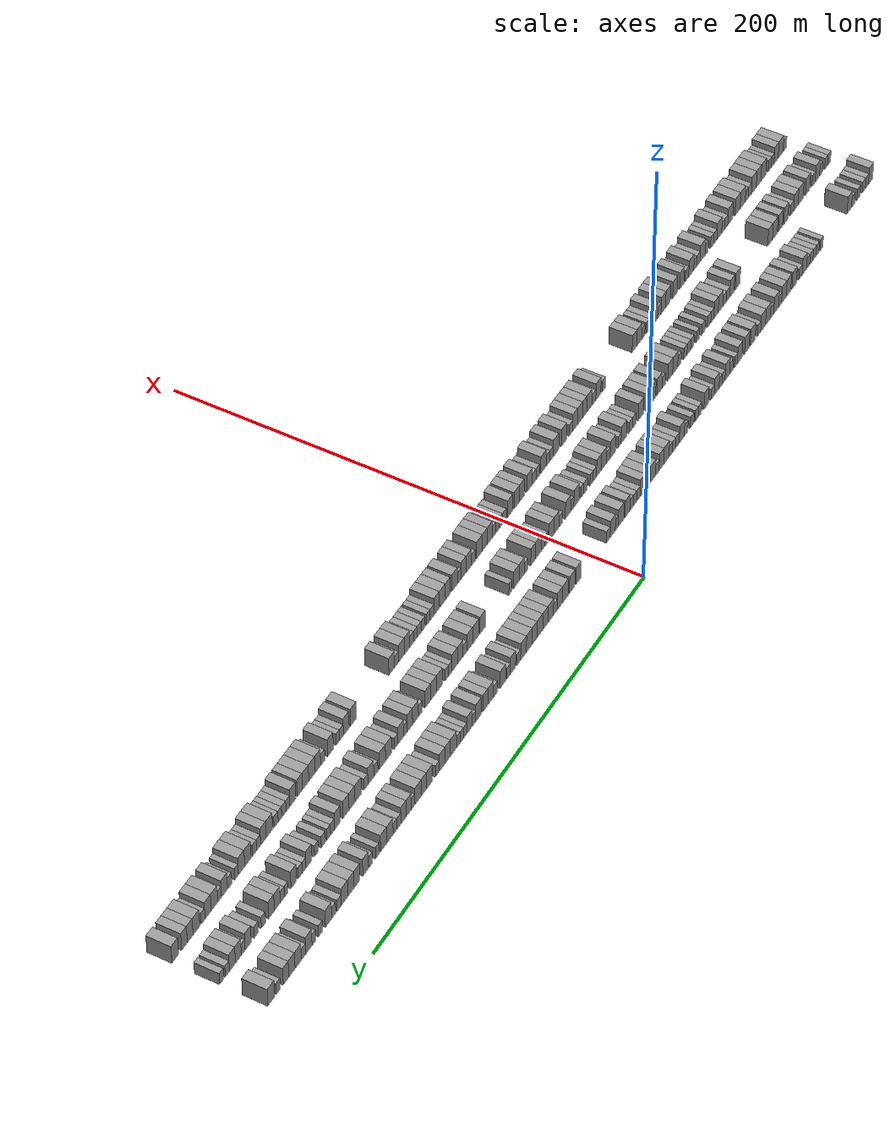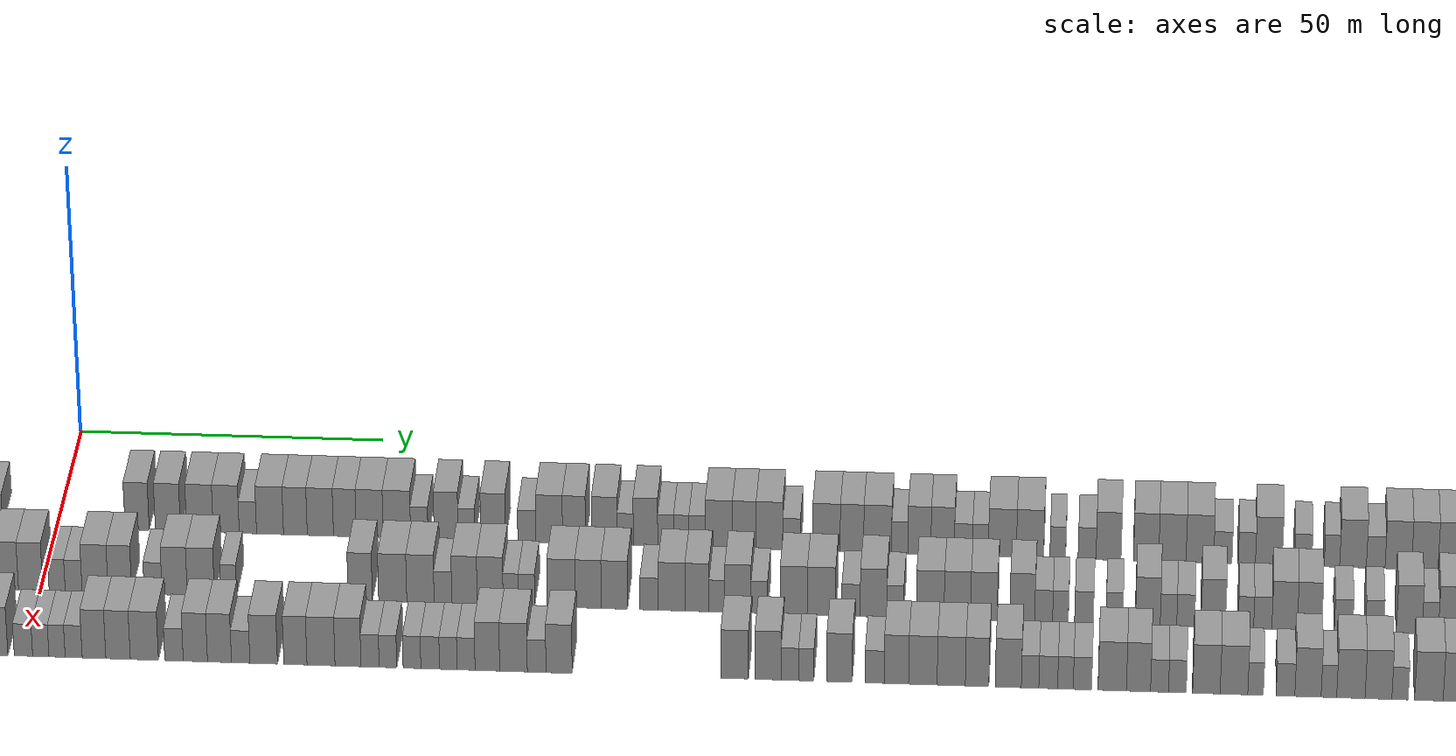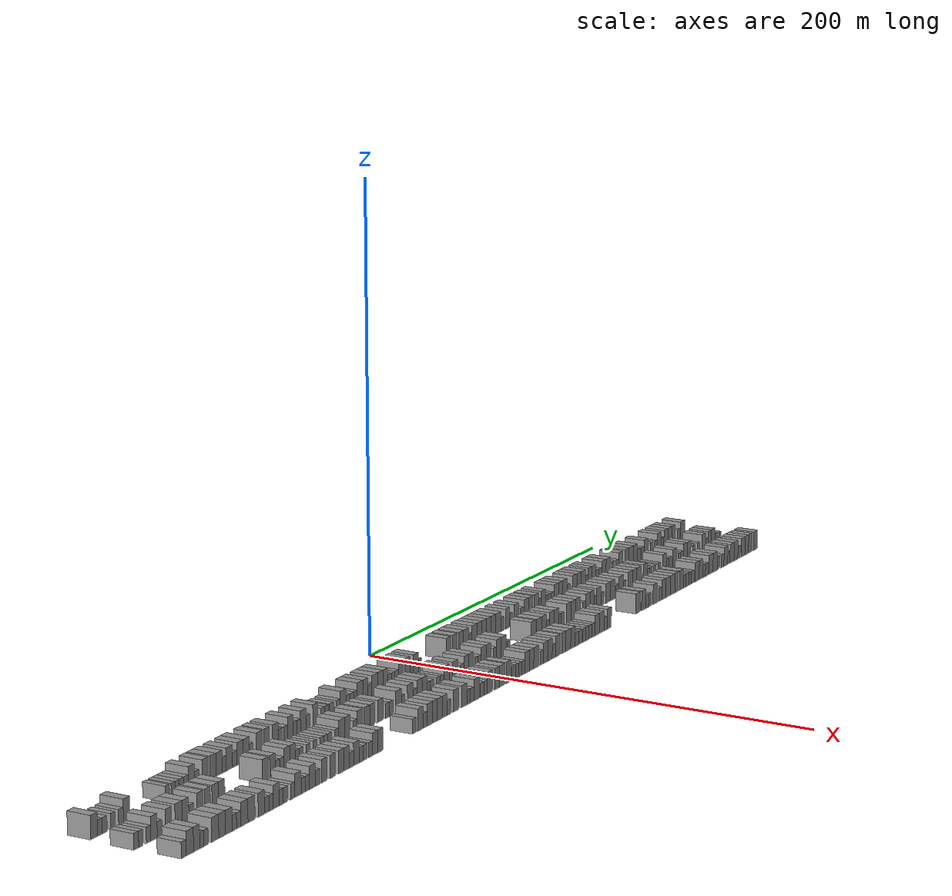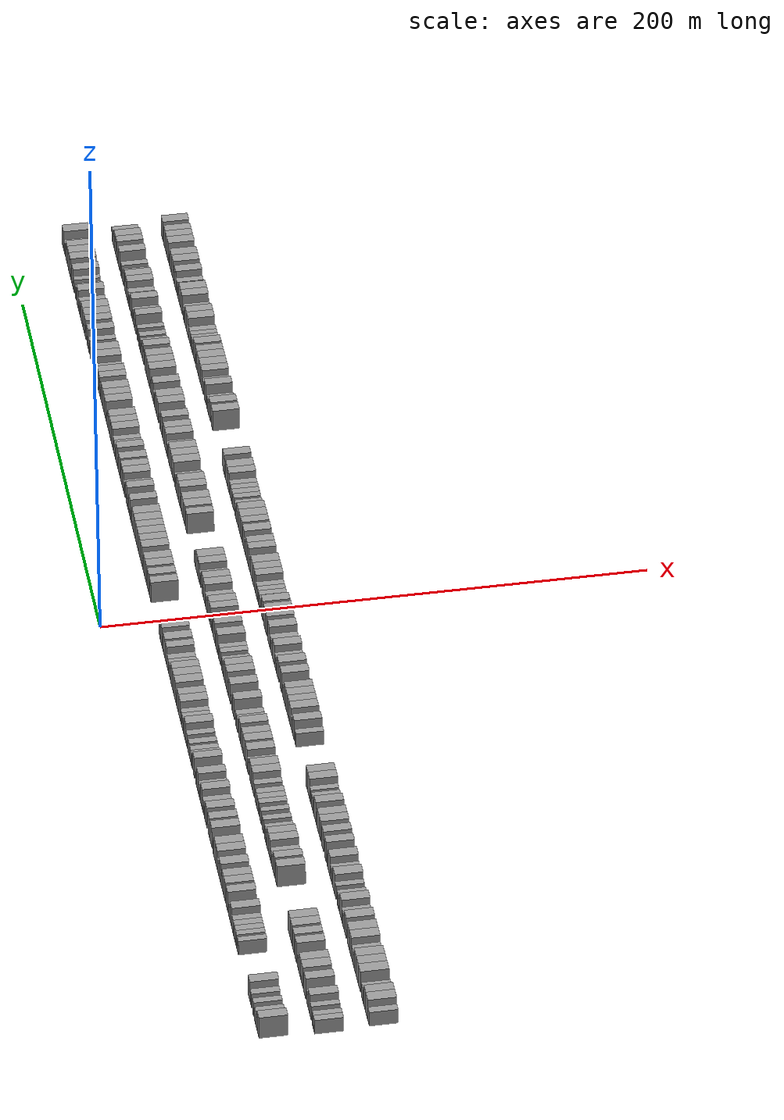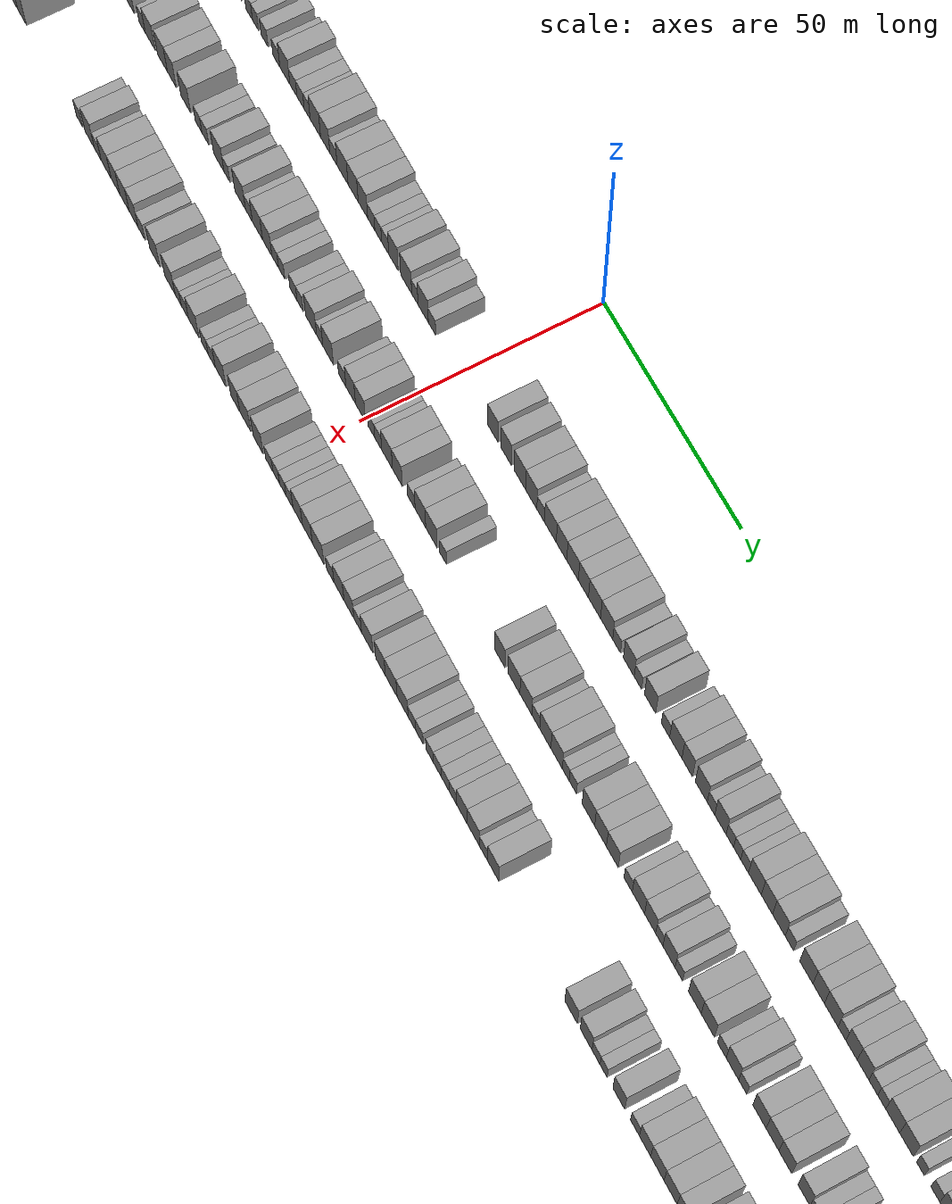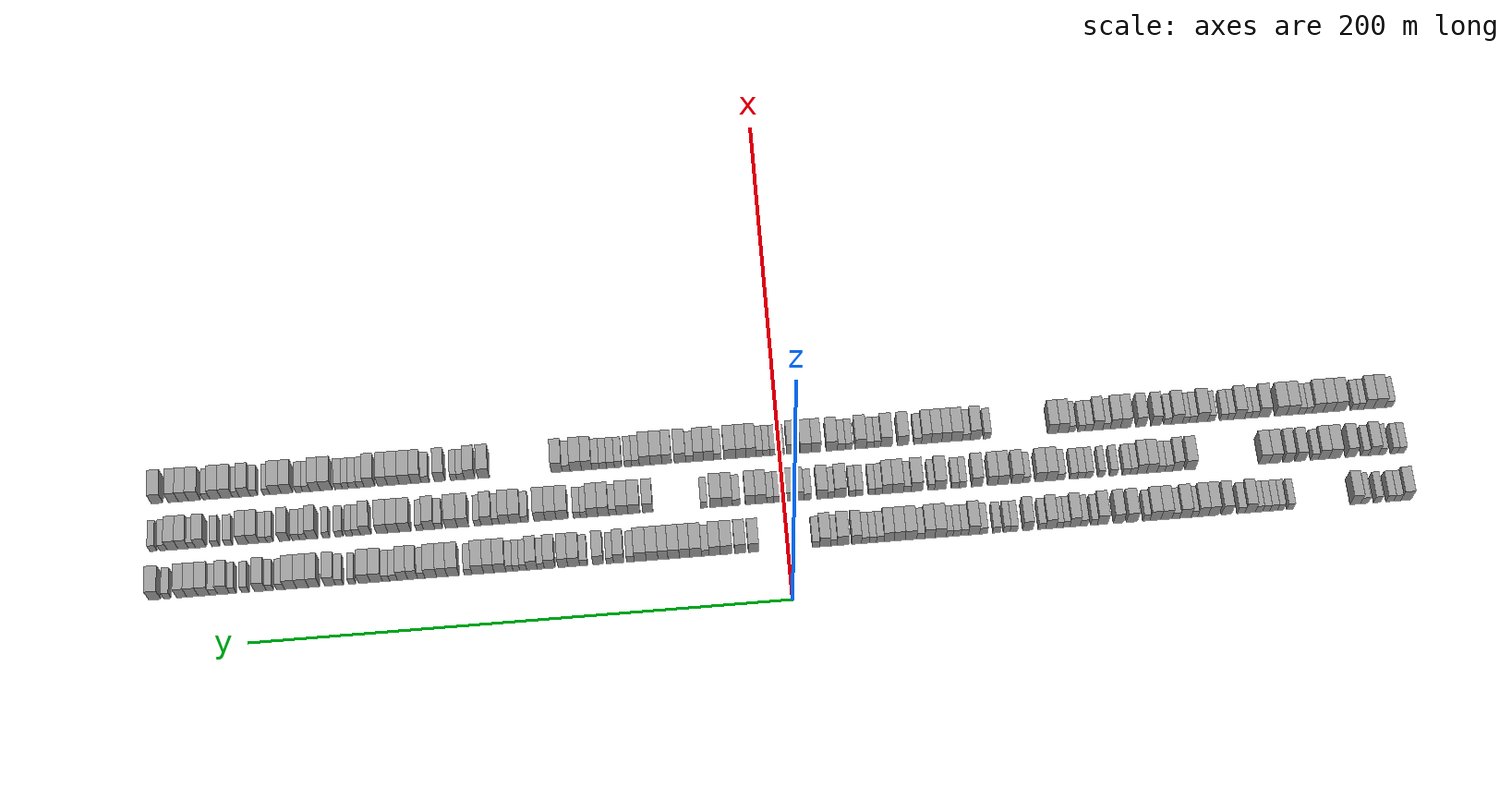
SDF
<sdf version="1.6">
 <world name="default">
  <scene>
   <sky><clouds><speed>12</speed></clouds></sky>
   <ambient>0.4 0.4 0.4 1</ambient>
   <background>0.7 0.7 0.7 1</background>
   <shadows>1</shadows>
  </scene>
  <gravity>0 0 -9.8066</gravity>
  <magnetic_field>6e-06 2.3e-05 -4.2e-05</magnetic_field>
  <physics default="0" name="default_physics" type="ode">
   <ode>
    <solver>
     <type>quick</type>
     <iters>10</iters>
     <sor>1.0</sor>
     <use_dynamic_moi_rescaling>0</use_dynamic_moi_rescaling>
    </solver>
    <constraints>
     <cfm>0</cfm>
     <erp>0.2</erp>
     <contact_max_correcting_vel>100</contact_max_correcting_vel>
     <contact_surface_layer>0.001</contact_surface_layer>
    </constraints>
   </ode>
   <max_step_size>0.004</max_step_size>
   <real_time_factor>1</real_time_factor>
   <real_time_update_rate>250</real_time_update_rate>
  </physics>
  <light name="sun" type="directional">
   <pose>0 0 10 0 0 0</pose>
   <diffuse>0.8 0.8 0.8 1</diffuse>
   <specular>0.2 0.2 0.2 1</specular>
   <attenuation>
    <range>1000</range>
    <constant>0.9</constant>
    <linear>0.01</linear>
    <quadratic>0.001</quadratic>
   </attenuation>
   <direction>-0.5 0.1 -0.9</direction>
  </light>
  <model name="building_1">
   <static>1</static>
   <pose>25.0000 -232.0293 0 0.000000 0.000000 0.000000</pose>
   <link name="link">
    <pose>0 0 4.50 0 0 0</pose>
    <collision name="collision"><geometry><box><size>10.0000 3.9415 9.0000</size></box></geometry></collision>
    <visual name="visual">
     <cast_shadows>0</cast_shadows>
     <geometry><box><size>10.0000 3.9415 9.0000</size></box></geometry>
     <material>
      <script>
       <uri>model://grey_wall/materials/scripts</uri>
       <uri>model://grey_wall/materials/textures</uri>
       <name>vrc/grey_wall</name>
      </script>
     </material>
    </visual>
   </link>
  </model>
  <model name="building_2">
   <static>1</static>
   <pose>25.0000 -228.6991 0 0.000000 0.000000 0.000000</pose>
   <link name="link">
    <pose>0 0 3.00 0 0 0</pose>
    <collision name="collision"><geometry><box><size>10.0000 2.7189 6.0000</size></box></geometry></collision>
    <visual name="visual">
     <cast_shadows>0</cast_shadows>
     <geometry><box><size>10.0000 2.7189 6.0000</size></box></geometry>
     <material>
      <script>
       <uri>model://grey_wall/materials/scripts</uri>
       <uri>model://grey_wall/materials/textures</uri>
       <name>vrc/grey_wall</name>
      </script>
     </material>
    </visual>
   </link>
  </model>
  <model name="building_3">
   <static>1</static>
   <pose>25.0000 -225.8802 0 0.000000 0.000000 0.000000</pose>
   <link name="link">
    <pose>0 0 3.00 0 0 0</pose>
    <collision name="collision"><geometry><box><size>10.0000 2.9188 6.0000</size></box></geometry></collision>
    <visual name="visual">
     <cast_shadows>0</cast_shadows>
     <geometry><box><size>10.0000 2.9188 6.0000</size></box></geometry>
     <material>
      <script>
       <uri>model://grey_wall/materials/scripts</uri>
       <uri>model://grey_wall/materials/textures</uri>
       <name>vrc/grey_wall</name>
      </script>
     </material>
    </visual>
   </link>
  </model>
  <model name="building_4">
   <static>1</static>
   <pose>25.0000 -221.0721 0 0.000000 0.000000 0.000000</pose>
   <link name="link">
    <pose>0 0 3.00 0 0 0</pose>
    <collision name="collision"><geometry><box><size>10.0000 2.6975 6.0000</size></box></geometry></collision>
    <visual name="visual">
     <cast_shadows>0</cast_shadows>
     <geometry><box><size>10.0000 2.6975 6.0000</size></box></geometry>
     <material>
      <script>
       <uri>model://grey_wall/materials/scripts</uri>
       <uri>model://grey_wall/materials/textures</uri>
       <name>vrc/grey_wall</name>
      </script>
     </material>
    </visual>
   </link>
  </model>
  <model name="building_5">
   <static>1</static>
   <pose>25.0000 -216.2645 0 0.000000 0.000000 0.000000</pose>
   <link name="link">
    <pose>0 0 3.00 0 0 0</pose>
    <collision name="collision"><geometry><box><size>10.0000 2.9177 6.0000</size></box></geometry></collision>
    <visual name="visual">
     <cast_shadows>0</cast_shadows>
     <geometry><box><size>10.0000 2.9177 6.0000</size></box></geometry>
     <material>
      <script>
       <uri>model://grey_wall/materials/scripts</uri>
       <uri>model://grey_wall/materials/textures</uri>
       <name>vrc/grey_wall</name>
      </script>
     </material>
    </visual>
   </link>
  </model>
  <model name="building_6">
   <static>1</static>
   <pose>25.0000 -212.8454 0 0.000000 0.000000 0.000000</pose>
   <link name="link">
    <pose>0 0 4.50 0 0 0</pose>
    <collision name="collision"><geometry><box><size>10.0000 3.9204 9.0000</size></box></geometry></collision>
    <visual name="visual">
     <cast_shadows>0</cast_shadows>
     <geometry><box><size>10.0000 3.9204 9.0000</size></box></geometry>
     <material>
      <script>
       <uri>model://grey_wall/materials/scripts</uri>
       <uri>model://grey_wall/materials/textures</uri>
       <name>vrc/grey_wall</name>
      </script>
     </material>
    </visual>
   </link>
  </model>
  <model name="building_7">
   <static>1</static>
   <pose>25.0000 -188.0401 0 0.000000 0.000000 0.000000</pose>
   <link name="link">
    <pose>0 0 3.00 0 0 0</pose>
    <collision name="collision"><geometry><box><size>10.0000 2.5634 6.0000</size></box></geometry></collision>
    <visual name="visual">
     <cast_shadows>0</cast_shadows>
     <geometry><box><size>10.0000 2.5634 6.0000</size></box></geometry>
     <material>
      <script>
       <uri>model://grey_wall/materials/scripts</uri>
       <uri>model://grey_wall/materials/textures</uri>
       <name>vrc/grey_wall</name>
      </script>
     </material>
    </visual>
   </link>
  </model>
  <model name="building_8">
   <static>1</static>
   <pose>25.0000 -184.5320 0 0.000000 0.000000 0.000000</pose>
   <link name="link">
    <pose>0 0 3.00 0 0 0</pose>
    <collision name="collision"><geometry><box><size>10.0000 2.4528 6.0000</size></box></geometry></collision>
    <visual name="visual">
     <cast_shadows>0</cast_shadows>
     <geometry><box><size>10.0000 2.4528 6.0000</size></box></geometry>
     <material>
      <script>
       <uri>model://grey_wall/materials/scripts</uri>
       <uri>model://grey_wall/materials/textures</uri>
       <name>vrc/grey_wall</name>
      </script>
     </material>
    </visual>
   </link>
  </model>
  <model name="building_9">
   <static>1</static>
   <pose>25.0000 -181.9103 0 0.000000 0.000000 0.000000</pose>
   <link name="link">
    <pose>0 0 3.00 0 0 0</pose>
    <collision name="collision"><geometry><box><size>10.0000 2.7905 6.0000</size></box></geometry></collision>
    <visual name="visual">
     <cast_shadows>0</cast_shadows>
     <geometry><box><size>10.0000 2.7905 6.0000</size></box></geometry>
     <material>
      <script>
       <uri>model://grey_wall/materials/scripts</uri>
       <uri>model://grey_wall/materials/textures</uri>
       <name>vrc/grey_wall</name>
      </script>
     </material>
    </visual>
   </link>
  </model>
  <model name="building_10">
   <static>1</static>
   <pose>25.0000 -179.0946 0 0.000000 0.000000 0.000000</pose>
   <link name="link">
    <pose>0 0 3.00 0 0 0</pose>
    <collision name="collision"><geometry><box><size>10.0000 2.8409 6.0000</size></box></geometry></collision>
    <visual name="visual">
     <cast_shadows>0</cast_shadows>
     <geometry><box><size>10.0000 2.8409 6.0000</size></box></geometry>
     <material>
      <script>
       <uri>model://grey_wall/materials/scripts</uri>
       <uri>model://grey_wall/materials/textures</uri>
       <name>vrc/grey_wall</name>
      </script>
     </material>
    </visual>
   </link>
  </model>
  <model name="building_11">
   <static>1</static>
   <pose>25.0000 -176.3258 0 0.000000 0.000000 0.000000</pose>
   <link name="link">
    <pose>0 0 3.00 0 0 0</pose>
    <collision name="collision"><geometry><box><size>10.0000 2.6966 6.0000</size></box></geometry></collision>
    <visual name="visual">
     <cast_shadows>0</cast_shadows>
     <geometry><box><size>10.0000 2.6966 6.0000</size></box></geometry>
     <material>
      <script>
       <uri>model://grey_wall/materials/scripts</uri>
       <uri>model://grey_wall/materials/textures</uri>
       <name>vrc/grey_wall</name>
      </script>
     </material>
    </visual>
   </link>
  </model>
  <model name="building_12">
   <static>1</static>
   <pose>25.0000 -173.0287 0 0.000000 0.000000 0.000000</pose>
   <link name="link">
    <pose>0 0 4.50 0 0 0</pose>
    <collision name="collision"><geometry><box><size>10.0000 3.8977 9.0000</size></box></geometry></collision>
    <visual name="visual">
     <cast_shadows>0</cast_shadows>
     <geometry><box><size>10.0000 3.8977 9.0000</size></box></geometry>
     <material>
      <script>
       <uri>model://grey_wall/materials/scripts</uri>
       <uri>model://grey_wall/materials/textures</uri>
       <name>vrc/grey_wall</name>
      </script>
     </material>
    </visual>
   </link>
  </model>
  <model name="building_13">
   <static>1</static>
   <pose>25.0000 -169.5838 0 0.000000 0.000000 0.000000</pose>
   <link name="link">
    <pose>0 0 3.00 0 0 0</pose>
    <collision name="collision"><geometry><box><size>10.0000 2.9921 6.0000</size></box></geometry></collision>
    <visual name="visual">
     <cast_shadows>0</cast_shadows>
     <geometry><box><size>10.0000 2.9921 6.0000</size></box></geometry>
     <material>
      <script>
       <uri>model://grey_wall/materials/scripts</uri>
       <uri>model://grey_wall/materials/textures</uri>
       <name>vrc/grey_wall</name>
      </script>
     </material>
    </visual>
   </link>
  </model>
  <model name="building_14">
   <static>1</static>
   <pose>25.0000 -164.1441 0 0.000000 0.000000 0.000000</pose>
   <link name="link">
    <pose>0 0 4.50 0 0 0</pose>
    <collision name="collision"><geometry><box><size>10.0000 3.8873 9.0000</size></box></geometry></collision>
    <visual name="visual">
     <cast_shadows>0</cast_shadows>
     <geometry><box><size>10.0000 3.8873 9.0000</size></box></geometry>
     <material>
      <script>
       <uri>model://grey_wall/materials/scripts</uri>
       <uri>model://grey_wall/materials/textures</uri>
       <name>vrc/grey_wall</name>
      </script>
     </material>
    </visual>
   </link>
  </model>
  <model name="building_15">
   <static>1</static>
   <pose>25.0000 -159.2074 0 0.000000 0.000000 0.000000</pose>
   <link name="link">
    <pose>0 0 4.50 0 0 0</pose>
    <collision name="collision"><geometry><box><size>10.0000 3.9860 9.0000</size></box></geometry></collision>
    <visual name="visual">
     <cast_shadows>0</cast_shadows>
     <geometry><box><size>10.0000 3.9860 9.0000</size></box></geometry>
     <material>
      <script>
       <uri>model://grey_wall/materials/scripts</uri>
       <uri>model://grey_wall/materials/textures</uri>
       <name>vrc/grey_wall</name>
      </script>
     </material>
    </visual>
   </link>
  </model>
  <model name="building_16">
   <static>1</static>
   <pose>25.0000 -155.2211 0 0.000000 0.000000 0.000000</pose>
   <link name="link">
    <pose>0 0 4.50 0 0 0</pose>
    <collision name="collision"><geometry><box><size>10.0000 3.9867 9.0000</size></box></geometry></collision>
    <visual name="visual">
     <cast_shadows>0</cast_shadows>
     <geometry><box><size>10.0000 3.9867 9.0000</size></box></geometry>
     <material>
      <script>
       <uri>model://grey_wall/materials/scripts</uri>
       <uri>model://grey_wall/materials/textures</uri>
       <name>vrc/grey_wall</name>
      </script>
     </material>
    </visual>
   </link>
  </model>
  <model name="building_17">
   <static>1</static>
   <pose>25.0000 -151.9793 0 0.000000 0.000000 0.000000</pose>
   <link name="link">
    <pose>0 0 3.00 0 0 0</pose>
    <collision name="collision"><geometry><box><size>10.0000 2.4969 6.0000</size></box></geometry></collision>
    <visual name="visual">
     <cast_shadows>0</cast_shadows>
     <geometry><box><size>10.0000 2.4969 6.0000</size></box></geometry>
     <material>
      <script>
       <uri>model://grey_wall/materials/scripts</uri>
       <uri>model://grey_wall/materials/textures</uri>
       <name>vrc/grey_wall</name>
      </script>
     </material>
    </visual>
   </link>
  </model>
  <model name="building_18">
   <static>1</static>
   <pose>25.0000 -148.5806 0 0.000000 0.000000 0.000000</pose>
   <link name="link">
    <pose>0 0 4.50 0 0 0</pose>
    <collision name="collision"><geometry><box><size>10.0000 4.3005 9.0000</size></box></geometry></collision>
    <visual name="visual">
     <cast_shadows>0</cast_shadows>
     <geometry><box><size>10.0000 4.3005 9.0000</size></box></geometry>
     <material>
      <script>
       <uri>model://grey_wall/materials/scripts</uri>
       <uri>model://grey_wall/materials/textures</uri>
       <name>vrc/grey_wall</name>
      </script>
     </material>
    </visual>
   </link>
  </model>
  <model name="building_19">
   <static>1</static>
   <pose>25.0000 -144.9628 0 0.000000 0.000000 0.000000</pose>
   <link name="link">
    <pose>0 0 3.00 0 0 0</pose>
    <collision name="collision"><geometry><box><size>10.0000 2.9353 6.0000</size></box></geometry></collision>
    <visual name="visual">
     <cast_shadows>0</cast_shadows>
     <geometry><box><size>10.0000 2.9353 6.0000</size></box></geometry>
     <material>
      <script>
       <uri>model://grey_wall/materials/scripts</uri>
       <uri>model://grey_wall/materials/textures</uri>
       <name>vrc/grey_wall</name>
      </script>
     </material>
    </visual>
   </link>
  </model>
  <model name="building_20">
   <static>1</static>
   <pose>25.0000 -141.4288 0 0.000000 0.000000 0.000000</pose>
   <link name="link">
    <pose>0 0 4.50 0 0 0</pose>
    <collision name="collision"><geometry><box><size>10.0000 4.1326 9.0000</size></box></geometry></collision>
    <visual name="visual">
     <cast_shadows>0</cast_shadows>
     <geometry><box><size>10.0000 4.1326 9.0000</size></box></geometry>
     <material>
      <script>
       <uri>model://grey_wall/materials/scripts</uri>
       <uri>model://grey_wall/materials/textures</uri>
       <name>vrc/grey_wall</name>
      </script>
     </material>
    </visual>
   </link>
  </model>
  <model name="building_21">
   <static>1</static>
   <pose>25.0000 -137.2846 0 0.000000 0.000000 0.000000</pose>
   <link name="link">
    <pose>0 0 4.50 0 0 0</pose>
    <collision name="collision"><geometry><box><size>10.0000 4.1558 9.0000</size></box></geometry></collision>
    <visual name="visual">
     <cast_shadows>0</cast_shadows>
     <geometry><box><size>10.0000 4.1558 9.0000</size></box></geometry>
     <material>
      <script>
       <uri>model://grey_wall/materials/scripts</uri>
       <uri>model://grey_wall/materials/textures</uri>
       <name>vrc/grey_wall</name>
      </script>
     </material>
    </visual>
   </link>
  </model>
  <model name="building_22">
   <static>1</static>
   <pose>25.0000 -133.8922 0 0.000000 0.000000 0.000000</pose>
   <link name="link">
    <pose>0 0 3.00 0 0 0</pose>
    <collision name="collision"><geometry><box><size>10.0000 2.6290 6.0000</size></box></geometry></collision>
    <visual name="visual">
     <cast_shadows>0</cast_shadows>
     <geometry><box><size>10.0000 2.6290 6.0000</size></box></geometry>
     <material>
      <script>
       <uri>model://grey_wall/materials/scripts</uri>
       <uri>model://grey_wall/materials/textures</uri>
       <name>vrc/grey_wall</name>
      </script>
     </material>
    </visual>
   </link>
  </model>
  <model name="building_23">
   <static>1</static>
   <pose>25.0000 -128.4736 0 0.000000 0.000000 0.000000</pose>
   <link name="link">
    <pose>0 0 4.50 0 0 0</pose>
    <collision name="collision"><geometry><box><size>10.0000 4.2082 9.0000</size></box></geometry></collision>
    <visual name="visual">
     <cast_shadows>0</cast_shadows>
     <geometry><box><size>10.0000 4.2082 9.0000</size></box></geometry>
     <material>
      <script>
       <uri>model://grey_wall/materials/scripts</uri>
       <uri>model://grey_wall/materials/textures</uri>
       <name>vrc/grey_wall</name>
      </script>
     </material>
    </visual>
   </link>
  </model>
  <model name="building_24">
   <static>1</static>
   <pose>25.0000 -123.4313 0 0.000000 0.000000 0.000000</pose>
   <link name="link">
    <pose>0 0 4.50 0 0 0</pose>
    <collision name="collision"><geometry><box><size>10.0000 3.8765 9.0000</size></box></geometry></collision>
    <visual name="visual">
     <cast_shadows>0</cast_shadows>
     <geometry><box><size>10.0000 3.8765 9.0000</size></box></geometry>
     <material>
      <script>
       <uri>model://grey_wall/materials/scripts</uri>
       <uri>model://grey_wall/materials/textures</uri>
       <name>vrc/grey_wall</name>
      </script>
     </material>
    </visual>
   </link>
  </model>
  <model name="building_25">
   <static>1</static>
   <pose>25.0000 -117.4766 0 0.000000 0.000000 0.000000</pose>
   <link name="link">
    <pose>0 0 4.50 0 0 0</pose>
    <collision name="collision"><geometry><box><size>10.0000 4.0329 9.0000</size></box></geometry></collision>
    <visual name="visual">
     <cast_shadows>0</cast_shadows>
     <geometry><box><size>10.0000 4.0329 9.0000</size></box></geometry>
     <material>
      <script>
       <uri>model://grey_wall/materials/scripts</uri>
       <uri>model://grey_wall/materials/textures</uri>
       <name>vrc/grey_wall</name>
      </script>
     </material>
    </visual>
   </link>
  </model>
  <model name="building_26">
   <static>1</static>
   <pose>25.0000 -114.1687 0 0.000000 0.000000 0.000000</pose>
   <link name="link">
    <pose>0 0 3.00 0 0 0</pose>
    <collision name="collision"><geometry><box><size>10.0000 2.5828 6.0000</size></box></geometry></collision>
    <visual name="visual">
     <cast_shadows>0</cast_shadows>
     <geometry><box><size>10.0000 2.5828 6.0000</size></box></geometry>
     <material>
      <script>
       <uri>model://grey_wall/materials/scripts</uri>
       <uri>model://grey_wall/materials/textures</uri>
       <name>vrc/grey_wall</name>
      </script>
     </material>
    </visual>
   </link>
  </model>
  <model name="building_27">
   <static>1</static>
   <pose>25.0000 -110.4275 0 0.000000 0.000000 0.000000</pose>
   <link name="link">
    <pose>0 0 3.00 0 0 0</pose>
    <collision name="collision"><geometry><box><size>10.0000 2.8996 6.0000</size></box></geometry></collision>
    <visual name="visual">
     <cast_shadows>0</cast_shadows>
     <geometry><box><size>10.0000 2.8996 6.0000</size></box></geometry>
     <material>
      <script>
       <uri>model://grey_wall/materials/scripts</uri>
       <uri>model://grey_wall/materials/textures</uri>
       <name>vrc/grey_wall</name>
      </script>
     </material>
    </visual>
   </link>
  </model>
  <model name="building_28">
   <static>1</static>
   <pose>25.0000 -107.0095 0 0.000000 0.000000 0.000000</pose>
   <link name="link">
    <pose>0 0 4.50 0 0 0</pose>
    <collision name="collision"><geometry><box><size>10.0000 3.9365 9.0000</size></box></geometry></collision>
    <visual name="visual">
     <cast_shadows>0</cast_shadows>
     <geometry><box><size>10.0000 3.9365 9.0000</size></box></geometry>
     <material>
      <script>
       <uri>model://grey_wall/materials/scripts</uri>
       <uri>model://grey_wall/materials/textures</uri>
       <name>vrc/grey_wall</name>
      </script>
     </material>
    </visual>
   </link>
  </model>
  <model name="building_29">
   <static>1</static>
   <pose>25.0000 -103.7926 0 0.000000 0.000000 0.000000</pose>
   <link name="link">
    <pose>0 0 3.00 0 0 0</pose>
    <collision name="collision"><geometry><box><size>10.0000 2.4973 6.0000</size></box></geometry></collision>
    <visual name="visual">
     <cast_shadows>0</cast_shadows>
     <geometry><box><size>10.0000 2.4973 6.0000</size></box></geometry>
     <material>
      <script>
       <uri>model://grey_wall/materials/scripts</uri>
       <uri>model://grey_wall/materials/textures</uri>
       <name>vrc/grey_wall</name>
      </script>
     </material>
    </visual>
   </link>
  </model>
  <model name="building_30">
   <static>1</static>
   <pose>25.0000 -101.2896 0 0.000000 0.000000 0.000000</pose>
   <link name="link">
    <pose>0 0 3.00 0 0 0</pose>
    <collision name="collision"><geometry><box><size>10.0000 2.5088 6.0000</size></box></geometry></collision>
    <visual name="visual">
     <cast_shadows>0</cast_shadows>
     <geometry><box><size>10.0000 2.5088 6.0000</size></box></geometry>
     <material>
      <script>
       <uri>model://grey_wall/materials/scripts</uri>
       <uri>model://grey_wall/materials/textures</uri>
       <name>vrc/grey_wall</name>
      </script>
     </material>
    </visual>
   </link>
  </model>
  <model name="building_31">
   <static>1</static>
   <pose>25.0000 -98.0342 0 0.000000 0.000000 0.000000</pose>
   <link name="link">
    <pose>0 0 4.50 0 0 0</pose>
    <collision name="collision"><geometry><box><size>10.0000 4.0020 9.0000</size></box></geometry></collision>
    <visual name="visual">
     <cast_shadows>0</cast_shadows>
     <geometry><box><size>10.0000 4.0020 9.0000</size></box></geometry>
     <material>
      <script>
       <uri>model://grey_wall/materials/scripts</uri>
       <uri>model://grey_wall/materials/textures</uri>
       <name>vrc/grey_wall</name>
      </script>
     </material>
    </visual>
   </link>
  </model>
  <model name="building_32">
   <static>1</static>
   <pose>25.0000 -94.6246 0 0.000000 0.000000 0.000000</pose>
   <link name="link">
    <pose>0 0 3.00 0 0 0</pose>
    <collision name="collision"><geometry><box><size>10.0000 2.8171 6.0000</size></box></geometry></collision>
    <visual name="visual">
     <cast_shadows>0</cast_shadows>
     <geometry><box><size>10.0000 2.8171 6.0000</size></box></geometry>
     <material>
      <script>
       <uri>model://grey_wall/materials/scripts</uri>
       <uri>model://grey_wall/materials/textures</uri>
       <name>vrc/grey_wall</name>
      </script>
     </material>
    </visual>
   </link>
  </model>
  <model name="building_33">
   <static>1</static>
   <pose>25.0000 -89.3384 0 0.000000 0.000000 0.000000</pose>
   <link name="link">
    <pose>0 0 4.50 0 0 0</pose>
    <collision name="collision"><geometry><box><size>10.0000 3.7554 9.0000</size></box></geometry></collision>
    <visual name="visual">
     <cast_shadows>0</cast_shadows>
     <geometry><box><size>10.0000 3.7554 9.0000</size></box></geometry>
     <material>
      <script>
       <uri>model://grey_wall/materials/scripts</uri>
       <uri>model://grey_wall/materials/textures</uri>
       <name>vrc/grey_wall</name>
      </script>
     </material>
    </visual>
   </link>
  </model>
  <model name="building_34">
   <static>1</static>
   <pose>25.0000 -84.0892 0 0.000000 0.000000 0.000000</pose>
   <link name="link">
    <pose>0 0 3.00 0 0 0</pose>
    <collision name="collision"><geometry><box><size>10.0000 2.7429 6.0000</size></box></geometry></collision>
    <visual name="visual">
     <cast_shadows>0</cast_shadows>
     <geometry><box><size>10.0000 2.7429 6.0000</size></box></geometry>
     <material>
      <script>
       <uri>model://grey_wall/materials/scripts</uri>
       <uri>model://grey_wall/materials/textures</uri>
       <name>vrc/grey_wall</name>
      </script>
     </material>
    </visual>
   </link>
  </model>
  <model name="building_35">
   <static>1</static>
   <pose>25.0000 -81.4183 0 0.000000 0.000000 0.000000</pose>
   <link name="link">
    <pose>0 0 3.00 0 0 0</pose>
    <collision name="collision"><geometry><box><size>10.0000 2.5989 6.0000</size></box></geometry></collision>
    <visual name="visual">
     <cast_shadows>0</cast_shadows>
     <geometry><box><size>10.0000 2.5989 6.0000</size></box></geometry>
     <material>
      <script>
       <uri>model://grey_wall/materials/scripts</uri>
       <uri>model://grey_wall/materials/textures</uri>
       <name>vrc/grey_wall</name>
      </script>
     </material>
    </visual>
   </link>
  </model>
  <model name="building_36">
   <static>1</static>
   <pose>25.0000 -77.6412 0 0.000000 0.000000 0.000000</pose>
   <link name="link">
    <pose>0 0 3.00 0 0 0</pose>
    <collision name="collision"><geometry><box><size>10.0000 2.9553 6.0000</size></box></geometry></collision>
    <visual name="visual">
     <cast_shadows>0</cast_shadows>
     <geometry><box><size>10.0000 2.9553 6.0000</size></box></geometry>
     <material>
      <script>
       <uri>model://grey_wall/materials/scripts</uri>
       <uri>model://grey_wall/materials/textures</uri>
       <name>vrc/grey_wall</name>
      </script>
     </material>
    </visual>
   </link>
  </model>
  <model name="building_37">
   <static>1</static>
   <pose>25.0000 -72.7020 0 0.000000 0.000000 0.000000</pose>
   <link name="link">
    <pose>0 0 3.00 0 0 0</pose>
    <collision name="collision"><geometry><box><size>10.0000 2.9232 6.0000</size></box></geometry></collision>
    <visual name="visual">
     <cast_shadows>0</cast_shadows>
     <geometry><box><size>10.0000 2.9232 6.0000</size></box></geometry>
     <material>
      <script>
       <uri>model://grey_wall/materials/scripts</uri>
       <uri>model://grey_wall/materials/textures</uri>
       <name>vrc/grey_wall</name>
      </script>
     </material>
    </visual>
   </link>
  </model>
  <model name="building_38">
   <static>1</static>
   <pose>25.0000 -69.1794 0 0.000000 0.000000 0.000000</pose>
   <link name="link">
    <pose>0 0 4.50 0 0 0</pose>
    <collision name="collision"><geometry><box><size>10.0000 4.1220 9.0000</size></box></geometry></collision>
    <visual name="visual">
     <cast_shadows>0</cast_shadows>
     <geometry><box><size>10.0000 4.1220 9.0000</size></box></geometry>
     <material>
      <script>
       <uri>model://grey_wall/materials/scripts</uri>
       <uri>model://grey_wall/materials/textures</uri>
       <name>vrc/grey_wall</name>
      </script>
     </material>
    </visual>
   </link>
  </model>
  <model name="building_39">
   <static>1</static>
   <pose>25.0000 -65.6607 0 0.000000 0.000000 0.000000</pose>
   <link name="link">
    <pose>0 0 3.00 0 0 0</pose>
    <collision name="collision"><geometry><box><size>10.0000 2.9153 6.0000</size></box></geometry></collision>
    <visual name="visual">
     <cast_shadows>0</cast_shadows>
     <geometry><box><size>10.0000 2.9153 6.0000</size></box></geometry>
     <material>
      <script>
       <uri>model://grey_wall/materials/scripts</uri>
       <uri>model://grey_wall/materials/textures</uri>
       <name>vrc/grey_wall</name>
      </script>
     </material>
    </visual>
   </link>
  </model>
  <model name="building_40">
   <static>1</static>
   <pose>25.0000 -62.7199 0 0.000000 0.000000 0.000000</pose>
   <link name="link">
    <pose>0 0 3.00 0 0 0</pose>
    <collision name="collision"><geometry><box><size>10.0000 2.9665 6.0000</size></box></geometry></collision>
    <visual name="visual">
     <cast_shadows>0</cast_shadows>
     <geometry><box><size>10.0000 2.9665 6.0000</size></box></geometry>
     <material>
      <script>
       <uri>model://grey_wall/materials/scripts</uri>
       <uri>model://grey_wall/materials/textures</uri>
       <name>vrc/grey_wall</name>
      </script>
     </material>
    </visual>
   </link>
  </model>
  <model name="building_41">
   <static>1</static>
   <pose>25.0000 -60.0030 0 0.000000 0.000000 0.000000</pose>
   <link name="link">
    <pose>0 0 3.00 0 0 0</pose>
    <collision name="collision"><geometry><box><size>10.0000 2.4672 6.0000</size></box></geometry></collision>
    <visual name="visual">
     <cast_shadows>0</cast_shadows>
     <geometry><box><size>10.0000 2.4672 6.0000</size></box></geometry>
     <material>
      <script>
       <uri>model://grey_wall/materials/scripts</uri>
       <uri>model://grey_wall/materials/textures</uri>
       <name>vrc/grey_wall</name>
      </script>
     </material>
    </visual>
   </link>
  </model>
  <model name="building_42">
   <static>1</static>
   <pose>25.0000 -56.6272 0 0.000000 0.000000 0.000000</pose>
   <link name="link">
    <pose>0 0 4.50 0 0 0</pose>
    <collision name="collision"><geometry><box><size>10.0000 4.2846 9.0000</size></box></geometry></collision>
    <visual name="visual">
     <cast_shadows>0</cast_shadows>
     <geometry><box><size>10.0000 4.2846 9.0000</size></box></geometry>
     <material>
      <script>
       <uri>model://grey_wall/materials/scripts</uri>
       <uri>model://grey_wall/materials/textures</uri>
       <name>vrc/grey_wall</name>
      </script>
     </material>
    </visual>
   </link>
  </model>
  <model name="building_43">
   <static>1</static>
   <pose>25.0000 -52.5892 0 0.000000 0.000000 0.000000</pose>
   <link name="link">
    <pose>0 0 4.50 0 0 0</pose>
    <collision name="collision"><geometry><box><size>10.0000 3.7914 9.0000</size></box></geometry></collision>
    <visual name="visual">
     <cast_shadows>0</cast_shadows>
     <geometry><box><size>10.0000 3.7914 9.0000</size></box></geometry>
     <material>
      <script>
       <uri>model://grey_wall/materials/scripts</uri>
       <uri>model://grey_wall/materials/textures</uri>
       <name>vrc/grey_wall</name>
      </script>
     </material>
    </visual>
   </link>
  </model>
  <model name="building_44">
   <static>1</static>
   <pose>25.0000 -49.2314 0 0.000000 0.000000 0.000000</pose>
   <link name="link">
    <pose>0 0 3.00 0 0 0</pose>
    <collision name="collision"><geometry><box><size>10.0000 2.9242 6.0000</size></box></geometry></collision>
    <visual name="visual">
     <cast_shadows>0</cast_shadows>
     <geometry><box><size>10.0000 2.9242 6.0000</size></box></geometry>
     <material>
      <script>
       <uri>model://grey_wall/materials/scripts</uri>
       <uri>model://grey_wall/materials/textures</uri>
       <name>vrc/grey_wall</name>
      </script>
     </material>
    </visual>
   </link>
  </model>
  <model name="building_45">
   <static>1</static>
   <pose>25.0000 -45.5761 0 0.000000 0.000000 0.000000</pose>
   <link name="link">
    <pose>0 0 4.50 0 0 0</pose>
    <collision name="collision"><geometry><box><size>10.0000 4.3864 9.0000</size></box></geometry></collision>
    <visual name="visual">
     <cast_shadows>0</cast_shadows>
     <geometry><box><size>10.0000 4.3864 9.0000</size></box></geometry>
     <material>
      <script>
       <uri>model://grey_wall/materials/scripts</uri>
       <uri>model://grey_wall/materials/textures</uri>
       <name>vrc/grey_wall</name>
      </script>
     </material>
    </visual>
   </link>
  </model>
  <model name="building_46">
   <static>1</static>
   <pose>25.0000 -41.3251 0 0.000000 0.000000 0.000000</pose>
   <link name="link">
    <pose>0 0 4.50 0 0 0</pose>
    <collision name="collision"><geometry><box><size>10.0000 4.1157 9.0000</size></box></geometry></collision>
    <visual name="visual">
     <cast_shadows>0</cast_shadows>
     <geometry><box><size>10.0000 4.1157 9.0000</size></box></geometry>
     <material>
      <script>
       <uri>model://grey_wall/materials/scripts</uri>
       <uri>model://grey_wall/materials/textures</uri>
       <name>vrc/grey_wall</name>
      </script>
     </material>
    </visual>
   </link>
  </model>
  <model name="building_47">
   <static>1</static>
   <pose>25.0000 -37.3677 0 0.000000 0.000000 0.000000</pose>
   <link name="link">
    <pose>0 0 4.50 0 0 0</pose>
    <collision name="collision"><geometry><box><size>10.0000 3.7991 9.0000</size></box></geometry></collision>
    <visual name="visual">
     <cast_shadows>0</cast_shadows>
     <geometry><box><size>10.0000 3.7991 9.0000</size></box></geometry>
     <material>
      <script>
       <uri>model://grey_wall/materials/scripts</uri>
       <uri>model://grey_wall/materials/textures</uri>
       <name>vrc/grey_wall</name>
      </script>
     </material>
    </visual>
   </link>
  </model>
  <model name="building_48">
   <static>1</static>
   <pose>25.0000 -34.0540 0 0.000000 0.000000 0.000000</pose>
   <link name="link">
    <pose>0 0 3.00 0 0 0</pose>
    <collision name="collision"><geometry><box><size>10.0000 2.8284 6.0000</size></box></geometry></collision>
    <visual name="visual">
     <cast_shadows>0</cast_shadows>
     <geometry><box><size>10.0000 2.8284 6.0000</size></box></geometry>
     <material>
      <script>
       <uri>model://grey_wall/materials/scripts</uri>
       <uri>model://grey_wall/materials/textures</uri>
       <name>vrc/grey_wall</name>
      </script>
     </material>
    </visual>
   </link>
  </model>
  <model name="building_49">
   <static>1</static>
   <pose>25.0000 -31.2885 0 0.000000 0.000000 0.000000</pose>
   <link name="link">
    <pose>0 0 3.00 0 0 0</pose>
    <collision name="collision"><geometry><box><size>10.0000 2.7026 6.0000</size></box></geometry></collision>
    <visual name="visual">
     <cast_shadows>0</cast_shadows>
     <geometry><box><size>10.0000 2.7026 6.0000</size></box></geometry>
     <material>
      <script>
       <uri>model://grey_wall/materials/scripts</uri>
       <uri>model://grey_wall/materials/textures</uri>
       <name>vrc/grey_wall</name>
      </script>
     </material>
    </visual>
   </link>
  </model>
  <model name="building_50">
   <static>1</static>
   <pose>25.0000 -28.5184 0 0.000000 0.000000 0.000000</pose>
   <link name="link">
    <pose>0 0 3.00 0 0 0</pose>
    <collision name="collision"><geometry><box><size>10.0000 2.8377 6.0000</size></box></geometry></collision>
    <visual name="visual">
     <cast_shadows>0</cast_shadows>
     <geometry><box><size>10.0000 2.8377 6.0000</size></box></geometry>
     <material>
      <script>
       <uri>model://grey_wall/materials/scripts</uri>
       <uri>model://grey_wall/materials/textures</uri>
       <name>vrc/grey_wall</name>
      </script>
     </material>
    </visual>
   </link>
  </model>
  <model name="building_51">
   <static>1</static>
   <pose>25.0000 -25.2551 0 0.000000 0.000000 0.000000</pose>
   <link name="link">
    <pose>0 0 4.50 0 0 0</pose>
    <collision name="collision"><geometry><box><size>10.0000 3.6889 9.0000</size></box></geometry></collision>
    <visual name="visual">
     <cast_shadows>0</cast_shadows>
     <geometry><box><size>10.0000 3.6889 9.0000</size></box></geometry>
     <material>
      <script>
       <uri>model://grey_wall/materials/scripts</uri>
       <uri>model://grey_wall/materials/textures</uri>
       <name>vrc/grey_wall</name>
      </script>
     </material>
    </visual>
   </link>
  </model>
  <model name="building_52">
   <static>1</static>
   <pose>25.0000 -20.2376 0 0.000000 0.000000 0.000000</pose>
   <link name="link">
    <pose>0 0 4.50 0 0 0</pose>
    <collision name="collision"><geometry><box><size>10.0000 4.3462 9.0000</size></box></geometry></collision>
    <visual name="visual">
     <cast_shadows>0</cast_shadows>
     <geometry><box><size>10.0000 4.3462 9.0000</size></box></geometry>
     <material>
      <script>
       <uri>model://grey_wall/materials/scripts</uri>
       <uri>model://grey_wall/materials/textures</uri>
       <name>vrc/grey_wall</name>
      </script>
     </material>
    </visual>
   </link>
  </model>
  <model name="building_53">
   <static>1</static>
   <pose>25.0000 -16.8437 0 0.000000 0.000000 0.000000</pose>
   <link name="link">
    <pose>0 0 3.00 0 0 0</pose>
    <collision name="collision"><geometry><box><size>10.0000 2.4417 6.0000</size></box></geometry></collision>
    <visual name="visual">
     <cast_shadows>0</cast_shadows>
     <geometry><box><size>10.0000 2.4417 6.0000</size></box></geometry>
     <material>
      <script>
       <uri>model://grey_wall/materials/scripts</uri>
       <uri>model://grey_wall/materials/textures</uri>
       <name>vrc/grey_wall</name>
      </script>
     </material>
    </visual>
   </link>
  </model>
  <model name="building_54">
   <static>1</static>
   <pose>25.0000 -13.5977 0 0.000000 0.000000 0.000000</pose>
   <link name="link">
    <pose>0 0 4.50 0 0 0</pose>
    <collision name="collision"><geometry><box><size>10.0000 4.0503 9.0000</size></box></geometry></collision>
    <visual name="visual">
     <cast_shadows>0</cast_shadows>
     <geometry><box><size>10.0000 4.0503 9.0000</size></box></geometry>
     <material>
      <script>
       <uri>model://grey_wall/materials/scripts</uri>
       <uri>model://grey_wall/materials/textures</uri>
       <name>vrc/grey_wall</name>
      </script>
     </material>
    </visual>
   </link>
  </model>
  <model name="building_55">
   <static>1</static>
   <pose>25.0000 -10.1420 0 0.000000 0.000000 0.000000</pose>
   <link name="link">
    <pose>0 0 3.00 0 0 0</pose>
    <collision name="collision"><geometry><box><size>10.0000 2.8613 6.0000</size></box></geometry></collision>
    <visual name="visual">
     <cast_shadows>0</cast_shadows>
     <geometry><box><size>10.0000 2.8613 6.0000</size></box></geometry>
     <material>
      <script>
       <uri>model://grey_wall/materials/scripts</uri>
       <uri>model://grey_wall/materials/textures</uri>
       <name>vrc/grey_wall</name>
      </script>
     </material>
    </visual>
   </link>
  </model>
  <model name="building_56">
   <static>1</static>
   <pose>25.0000 13.1468 0 0.000000 0.000000 0.000000</pose>
   <link name="link">
    <pose>0 0 4.50 0 0 0</pose>
    <collision name="collision"><geometry><box><size>10.0000 3.9054 9.0000</size></box></geometry></collision>
    <visual name="visual">
     <cast_shadows>0</cast_shadows>
     <geometry><box><size>10.0000 3.9054 9.0000</size></box></geometry>
     <material>
      <script>
       <uri>model://grey_wall/materials/scripts</uri>
       <uri>model://grey_wall/materials/textures</uri>
       <name>vrc/grey_wall</name>
      </script>
     </material>
    </visual>
   </link>
  </model>
  <model name="building_57">
   <static>1</static>
   <pose>25.0000 18.1420 0 0.000000 0.000000 0.000000</pose>
   <link name="link">
    <pose>0 0 4.50 0 0 0</pose>
    <collision name="collision"><geometry><box><size>10.0000 4.0850 9.0000</size></box></geometry></collision>
    <visual name="visual">
     <cast_shadows>0</cast_shadows>
     <geometry><box><size>10.0000 4.0850 9.0000</size></box></geometry>
     <material>
      <script>
       <uri>model://grey_wall/materials/scripts</uri>
       <uri>model://grey_wall/materials/textures</uri>
       <name>vrc/grey_wall</name>
      </script>
     </material>
    </visual>
   </link>
  </model>
  <model name="building_58">
   <static>1</static>
   <pose>25.0000 23.3389 0 0.000000 0.000000 0.000000</pose>
   <link name="link">
    <pose>0 0 4.50 0 0 0</pose>
    <collision name="collision"><geometry><box><size>10.0000 4.3088 9.0000</size></box></geometry></collision>
    <visual name="visual">
     <cast_shadows>0</cast_shadows>
     <geometry><box><size>10.0000 4.3088 9.0000</size></box></geometry>
     <material>
      <script>
       <uri>model://grey_wall/materials/scripts</uri>
       <uri>model://grey_wall/materials/textures</uri>
       <name>vrc/grey_wall</name>
      </script>
     </material>
    </visual>
   </link>
  </model>
  <model name="building_59">
   <static>1</static>
   <pose>25.0000 27.5968 0 0.000000 0.000000 0.000000</pose>
   <link name="link">
    <pose>0 0 4.50 0 0 0</pose>
    <collision name="collision"><geometry><box><size>10.0000 4.2070 9.0000</size></box></geometry></collision>
    <visual name="visual">
     <cast_shadows>0</cast_shadows>
     <geometry><box><size>10.0000 4.2070 9.0000</size></box></geometry>
     <material>
      <script>
       <uri>model://grey_wall/materials/scripts</uri>
       <uri>model://grey_wall/materials/textures</uri>
       <name>vrc/grey_wall</name>
      </script>
     </material>
    </visual>
   </link>
  </model>
  <model name="building_60">
   <static>1</static>
   <pose>25.0000 31.1059 0 0.000000 0.000000 0.000000</pose>
   <link name="link">
    <pose>0 0 3.00 0 0 0</pose>
    <collision name="collision"><geometry><box><size>10.0000 2.8114 6.0000</size></box></geometry></collision>
    <visual name="visual">
     <cast_shadows>0</cast_shadows>
     <geometry><box><size>10.0000 2.8114 6.0000</size></box></geometry>
     <material>
      <script>
       <uri>model://grey_wall/materials/scripts</uri>
       <uri>model://grey_wall/materials/textures</uri>
       <name>vrc/grey_wall</name>
      </script>
     </material>
    </visual>
   </link>
  </model>
  <model name="building_61">
   <static>1</static>
   <pose>25.0000 34.6930 0 0.000000 0.000000 0.000000</pose>
   <link name="link">
    <pose>0 0 4.50 0 0 0</pose>
    <collision name="collision"><geometry><box><size>10.0000 4.3627 9.0000</size></box></geometry></collision>
    <visual name="visual">
     <cast_shadows>0</cast_shadows>
     <geometry><box><size>10.0000 4.3627 9.0000</size></box></geometry>
     <material>
      <script>
       <uri>model://grey_wall/materials/scripts</uri>
       <uri>model://grey_wall/materials/textures</uri>
       <name>vrc/grey_wall</name>
      </script>
     </material>
    </visual>
   </link>
  </model>
  <model name="building_62">
   <static>1</static>
   <pose>25.0000 38.8026 0 0.000000 0.000000 0.000000</pose>
   <link name="link">
    <pose>0 0 4.50 0 0 0</pose>
    <collision name="collision"><geometry><box><size>10.0000 3.8565 9.0000</size></box></geometry></collision>
    <visual name="visual">
     <cast_shadows>0</cast_shadows>
     <geometry><box><size>10.0000 3.8565 9.0000</size></box></geometry>
     <material>
      <script>
       <uri>model://grey_wall/materials/scripts</uri>
       <uri>model://grey_wall/materials/textures</uri>
       <name>vrc/grey_wall</name>
      </script>
     </material>
    </visual>
   </link>
  </model>
  <model name="building_63">
   <static>1</static>
   <pose>25.0000 42.8578 0 0.000000 0.000000 0.000000</pose>
   <link name="link">
    <pose>0 0 4.50 0 0 0</pose>
    <collision name="collision"><geometry><box><size>10.0000 4.2539 9.0000</size></box></geometry></collision>
    <visual name="visual">
     <cast_shadows>0</cast_shadows>
     <geometry><box><size>10.0000 4.2539 9.0000</size></box></geometry>
     <material>
      <script>
       <uri>model://grey_wall/materials/scripts</uri>
       <uri>model://grey_wall/materials/textures</uri>
       <name>vrc/grey_wall</name>
      </script>
     </material>
    </visual>
   </link>
  </model>
  <model name="building_64">
   <static>1</static>
   <pose>25.0000 46.8342 0 0.000000 0.000000 0.000000</pose>
   <link name="link">
    <pose>0 0 4.50 0 0 0</pose>
    <collision name="collision"><geometry><box><size>10.0000 3.6990 9.0000</size></box></geometry></collision>
    <visual name="visual">
     <cast_shadows>0</cast_shadows>
     <geometry><box><size>10.0000 3.6990 9.0000</size></box></geometry>
     <material>
      <script>
       <uri>model://grey_wall/materials/scripts</uri>
       <uri>model://grey_wall/materials/textures</uri>
       <name>vrc/grey_wall</name>
      </script>
     </material>
    </visual>
   </link>
  </model>
  <model name="building_65">
   <static>1</static>
   <pose>25.0000 50.8625 0 0.000000 0.000000 0.000000</pose>
   <link name="link">
    <pose>0 0 4.50 0 0 0</pose>
    <collision name="collision"><geometry><box><size>10.0000 4.3575 9.0000</size></box></geometry></collision>
    <visual name="visual">
     <cast_shadows>0</cast_shadows>
     <geometry><box><size>10.0000 4.3575 9.0000</size></box></geometry>
     <material>
      <script>
       <uri>model://grey_wall/materials/scripts</uri>
       <uri>model://grey_wall/materials/textures</uri>
       <name>vrc/grey_wall</name>
      </script>
     </material>
    </visual>
   </link>
  </model>
  <model name="building_66">
   <static>1</static>
   <pose>25.0000 55.2554 0 0.000000 0.000000 0.000000</pose>
   <link name="link">
    <pose>0 0 4.50 0 0 0</pose>
    <collision name="collision"><geometry><box><size>10.0000 4.4283 9.0000</size></box></geometry></collision>
    <visual name="visual">
     <cast_shadows>0</cast_shadows>
     <geometry><box><size>10.0000 4.4283 9.0000</size></box></geometry>
     <material>
      <script>
       <uri>model://grey_wall/materials/scripts</uri>
       <uri>model://grey_wall/materials/textures</uri>
       <name>vrc/grey_wall</name>
      </script>
     </material>
    </visual>
   </link>
  </model>
  <model name="building_67">
   <static>1</static>
   <pose>25.0000 58.8759 0 0.000000 0.000000 0.000000</pose>
   <link name="link">
    <pose>0 0 3.00 0 0 0</pose>
    <collision name="collision"><geometry><box><size>10.0000 2.8127 6.0000</size></box></geometry></collision>
    <visual name="visual">
     <cast_shadows>0</cast_shadows>
     <geometry><box><size>10.0000 2.8127 6.0000</size></box></geometry>
     <material>
      <script>
       <uri>model://grey_wall/materials/scripts</uri>
       <uri>model://grey_wall/materials/textures</uri>
       <name>vrc/grey_wall</name>
      </script>
     </material>
    </visual>
   </link>
  </model>
  <model name="building_68">
   <static>1</static>
   <pose>25.0000 63.2213 0 0.000000 0.000000 0.000000</pose>
   <link name="link">
    <pose>0 0 4.50 0 0 0</pose>
    <collision name="collision"><geometry><box><size>10.0000 3.8780 9.0000</size></box></geometry></collision>
    <visual name="visual">
     <cast_shadows>0</cast_shadows>
     <geometry><box><size>10.0000 3.8780 9.0000</size></box></geometry>
     <material>
      <script>
       <uri>model://grey_wall/materials/scripts</uri>
       <uri>model://grey_wall/materials/textures</uri>
       <name>vrc/grey_wall</name>
      </script>
     </material>
    </visual>
   </link>
  </model>
  <model name="building_69">
   <static>1</static>
   <pose>25.0000 66.4896 0 0.000000 0.000000 0.000000</pose>
   <link name="link">
    <pose>0 0 3.00 0 0 0</pose>
    <collision name="collision"><geometry><box><size>10.0000 2.6587 6.0000</size></box></geometry></collision>
    <visual name="visual">
     <cast_shadows>0</cast_shadows>
     <geometry><box><size>10.0000 2.6587 6.0000</size></box></geometry>
     <material>
      <script>
       <uri>model://grey_wall/materials/scripts</uri>
       <uri>model://grey_wall/materials/textures</uri>
       <name>vrc/grey_wall</name>
      </script>
     </material>
    </visual>
   </link>
  </model>
  <model name="building_70">
   <static>1</static>
   <pose>25.0000 70.8092 0 0.000000 0.000000 0.000000</pose>
   <link name="link">
    <pose>0 0 4.50 0 0 0</pose>
    <collision name="collision"><geometry><box><size>10.0000 3.9805 9.0000</size></box></geometry></collision>
    <visual name="visual">
     <cast_shadows>0</cast_shadows>
     <geometry><box><size>10.0000 3.9805 9.0000</size></box></geometry>
     <material>
      <script>
       <uri>model://grey_wall/materials/scripts</uri>
       <uri>model://grey_wall/materials/textures</uri>
       <name>vrc/grey_wall</name>
      </script>
     </material>
    </visual>
   </link>
  </model>
  <model name="building_71">
   <static>1</static>
   <pose>25.0000 76.2654 0 0.000000 0.000000 0.000000</pose>
   <link name="link">
    <pose>0 0 3.00 0 0 0</pose>
    <collision name="collision"><geometry><box><size>10.0000 2.9320 6.0000</size></box></geometry></collision>
    <visual name="visual">
     <cast_shadows>0</cast_shadows>
     <geometry><box><size>10.0000 2.9320 6.0000</size></box></geometry>
     <material>
      <script>
       <uri>model://grey_wall/materials/scripts</uri>
       <uri>model://grey_wall/materials/textures</uri>
       <name>vrc/grey_wall</name>
      </script>
     </material>
    </visual>
   </link>
  </model>
  <model name="building_72">
   <static>1</static>
   <pose>25.0000 79.8795 0 0.000000 0.000000 0.000000</pose>
   <link name="link">
    <pose>0 0 4.50 0 0 0</pose>
    <collision name="collision"><geometry><box><size>10.0000 4.2961 9.0000</size></box></geometry></collision>
    <visual name="visual">
     <cast_shadows>0</cast_shadows>
     <geometry><box><size>10.0000 4.2961 9.0000</size></box></geometry>
     <material>
      <script>
       <uri>model://grey_wall/materials/scripts</uri>
       <uri>model://grey_wall/materials/textures</uri>
       <name>vrc/grey_wall</name>
      </script>
     </material>
    </visual>
   </link>
  </model>
  <model name="building_73">
   <static>1</static>
   <pose>25.0000 83.8755 0 0.000000 0.000000 0.000000</pose>
   <link name="link">
    <pose>0 0 4.50 0 0 0</pose>
    <collision name="collision"><geometry><box><size>10.0000 3.6960 9.0000</size></box></geometry></collision>
    <visual name="visual">
     <cast_shadows>0</cast_shadows>
     <geometry><box><size>10.0000 3.6960 9.0000</size></box></geometry>
     <material>
      <script>
       <uri>model://grey_wall/materials/scripts</uri>
       <uri>model://grey_wall/materials/textures</uri>
       <name>vrc/grey_wall</name>
      </script>
     </material>
    </visual>
   </link>
  </model>
  <model name="building_74">
   <static>1</static>
   <pose>25.0000 88.7893 0 0.000000 0.000000 0.000000</pose>
   <link name="link">
    <pose>0 0 4.50 0 0 0</pose>
    <collision name="collision"><geometry><box><size>10.0000 4.1315 9.0000</size></box></geometry></collision>
    <visual name="visual">
     <cast_shadows>0</cast_shadows>
     <geometry><box><size>10.0000 4.1315 9.0000</size></box></geometry>
     <material>
      <script>
       <uri>model://grey_wall/materials/scripts</uri>
       <uri>model://grey_wall/materials/textures</uri>
       <name>vrc/grey_wall</name>
      </script>
     </material>
    </visual>
   </link>
  </model>
  <model name="building_75">
   <static>1</static>
   <pose>25.0000 92.1472 0 0.000000 0.000000 0.000000</pose>
   <link name="link">
    <pose>0 0 3.00 0 0 0</pose>
    <collision name="collision"><geometry><box><size>10.0000 2.5842 6.0000</size></box></geometry></collision>
    <visual name="visual">
     <cast_shadows>0</cast_shadows>
     <geometry><box><size>10.0000 2.5842 6.0000</size></box></geometry>
     <material>
      <script>
       <uri>model://grey_wall/materials/scripts</uri>
       <uri>model://grey_wall/materials/textures</uri>
       <name>vrc/grey_wall</name>
      </script>
     </material>
    </visual>
   </link>
  </model>
  <model name="building_76">
   <static>1</static>
   <pose>25.0000 95.4046 0 0.000000 0.000000 0.000000</pose>
   <link name="link">
    <pose>0 0 4.50 0 0 0</pose>
    <collision name="collision"><geometry><box><size>10.0000 3.9306 9.0000</size></box></geometry></collision>
    <visual name="visual">
     <cast_shadows>0</cast_shadows>
     <geometry><box><size>10.0000 3.9306 9.0000</size></box></geometry>
     <material>
      <script>
       <uri>model://grey_wall/materials/scripts</uri>
       <uri>model://grey_wall/materials/textures</uri>
       <name>vrc/grey_wall</name>
      </script>
     </material>
    </visual>
   </link>
  </model>
  <model name="building_77">
   <static>1</static>
   <pose>25.0000 98.6462 0 0.000000 0.000000 0.000000</pose>
   <link name="link">
    <pose>0 0 3.00 0 0 0</pose>
    <collision name="collision"><geometry><box><size>10.0000 2.5526 6.0000</size></box></geometry></collision>
    <visual name="visual">
     <cast_shadows>0</cast_shadows>
     <geometry><box><size>10.0000 2.5526 6.0000</size></box></geometry>
     <material>
      <script>
       <uri>model://grey_wall/materials/scripts</uri>
       <uri>model://grey_wall/materials/textures</uri>
       <name>vrc/grey_wall</name>
      </script>
     </material>
    </visual>
   </link>
  </model>
  <model name="building_78">
   <static>1</static>
   <pose>25.0000 101.1556 0 0.000000 0.000000 0.000000</pose>
   <link name="link">
    <pose>0 0 3.00 0 0 0</pose>
    <collision name="collision"><geometry><box><size>10.0000 2.4662 6.0000</size></box></geometry></collision>
    <visual name="visual">
     <cast_shadows>0</cast_shadows>
     <geometry><box><size>10.0000 2.4662 6.0000</size></box></geometry>
     <material>
      <script>
       <uri>model://grey_wall/materials/scripts</uri>
       <uri>model://grey_wall/materials/textures</uri>
       <name>vrc/grey_wall</name>
      </script>
     </material>
    </visual>
   </link>
  </model>
  <model name="building_79">
   <static>1</static>
   <pose>25.0000 103.7136 0 0.000000 0.000000 0.000000</pose>
   <link name="link">
    <pose>0 0 3.00 0 0 0</pose>
    <collision name="collision"><geometry><box><size>10.0000 2.6497 6.0000</size></box></geometry></collision>
    <visual name="visual">
     <cast_shadows>0</cast_shadows>
     <geometry><box><size>10.0000 2.6497 6.0000</size></box></geometry>
     <material>
      <script>
       <uri>model://grey_wall/materials/scripts</uri>
       <uri>model://grey_wall/materials/textures</uri>
       <name>vrc/grey_wall</name>
      </script>
     </material>
    </visual>
   </link>
  </model>
  <model name="building_80">
   <static>1</static>
   <pose>25.0000 107.2167 0 0.000000 0.000000 0.000000</pose>
   <link name="link">
    <pose>0 0 4.50 0 0 0</pose>
    <collision name="collision"><geometry><box><size>10.0000 4.3565 9.0000</size></box></geometry></collision>
    <visual name="visual">
     <cast_shadows>0</cast_shadows>
     <geometry><box><size>10.0000 4.3565 9.0000</size></box></geometry>
     <material>
      <script>
       <uri>model://grey_wall/materials/scripts</uri>
       <uri>model://grey_wall/materials/textures</uri>
       <name>vrc/grey_wall</name>
      </script>
     </material>
    </visual>
   </link>
  </model>
  <model name="building_81">
   <static>1</static>
   <pose>25.0000 111.3000 0 0.000000 0.000000 0.000000</pose>
   <link name="link">
    <pose>0 0 4.50 0 0 0</pose>
    <collision name="collision"><geometry><box><size>10.0000 3.8101 9.0000</size></box></geometry></collision>
    <visual name="visual">
     <cast_shadows>0</cast_shadows>
     <geometry><box><size>10.0000 3.8101 9.0000</size></box></geometry>
     <material>
      <script>
       <uri>model://grey_wall/materials/scripts</uri>
       <uri>model://grey_wall/materials/textures</uri>
       <name>vrc/grey_wall</name>
      </script>
     </material>
    </visual>
   </link>
  </model>
  <model name="building_82">
   <static>1</static>
   <pose>25.0000 115.3463 0 0.000000 0.000000 0.000000</pose>
   <link name="link">
    <pose>0 0 4.50 0 0 0</pose>
    <collision name="collision"><geometry><box><size>10.0000 4.2824 9.0000</size></box></geometry></collision>
    <visual name="visual">
     <cast_shadows>0</cast_shadows>
     <geometry><box><size>10.0000 4.2824 9.0000</size></box></geometry>
     <material>
      <script>
       <uri>model://grey_wall/materials/scripts</uri>
       <uri>model://grey_wall/materials/textures</uri>
       <name>vrc/grey_wall</name>
      </script>
     </material>
    </visual>
   </link>
  </model>
  <model name="building_83">
   <static>1</static>
   <pose>25.0000 118.9060 0 0.000000 0.000000 0.000000</pose>
   <link name="link">
    <pose>0 0 3.00 0 0 0</pose>
    <collision name="collision"><geometry><box><size>10.0000 2.8368 6.0000</size></box></geometry></collision>
    <visual name="visual">
     <cast_shadows>0</cast_shadows>
     <geometry><box><size>10.0000 2.8368 6.0000</size></box></geometry>
     <material>
      <script>
       <uri>model://grey_wall/materials/scripts</uri>
       <uri>model://grey_wall/materials/textures</uri>
       <name>vrc/grey_wall</name>
      </script>
     </material>
    </visual>
   </link>
  </model>
  <model name="building_84">
   <static>1</static>
   <pose>25.0000 124.5328 0 0.000000 0.000000 0.000000</pose>
   <link name="link">
    <pose>0 0 4.50 0 0 0</pose>
    <collision name="collision"><geometry><box><size>10.0000 4.4168 9.0000</size></box></geometry></collision>
    <visual name="visual">
     <cast_shadows>0</cast_shadows>
     <geometry><box><size>10.0000 4.4168 9.0000</size></box></geometry>
     <material>
      <script>
       <uri>model://grey_wall/materials/scripts</uri>
       <uri>model://grey_wall/materials/textures</uri>
       <name>vrc/grey_wall</name>
      </script>
     </material>
    </visual>
   </link>
  </model>
  <model name="building_85">
   <static>1</static>
   <pose>25.0000 128.6353 0 0.000000 0.000000 0.000000</pose>
   <link name="link">
    <pose>0 0 4.50 0 0 0</pose>
    <collision name="collision"><geometry><box><size>10.0000 3.7884 9.0000</size></box></geometry></collision>
    <visual name="visual">
     <cast_shadows>0</cast_shadows>
     <geometry><box><size>10.0000 3.7884 9.0000</size></box></geometry>
     <material>
      <script>
       <uri>model://grey_wall/materials/scripts</uri>
       <uri>model://grey_wall/materials/textures</uri>
       <name>vrc/grey_wall</name>
      </script>
     </material>
    </visual>
   </link>
  </model>
  <model name="building_86">
   <static>1</static>
   <pose>25.0000 132.7688 0 0.000000 0.000000 0.000000</pose>
   <link name="link">
    <pose>0 0 4.50 0 0 0</pose>
    <collision name="collision"><geometry><box><size>10.0000 4.4785 9.0000</size></box></geometry></collision>
    <visual name="visual">
     <cast_shadows>0</cast_shadows>
     <geometry><box><size>10.0000 4.4785 9.0000</size></box></geometry>
     <material>
      <script>
       <uri>model://grey_wall/materials/scripts</uri>
       <uri>model://grey_wall/materials/textures</uri>
       <name>vrc/grey_wall</name>
      </script>
     </material>
    </visual>
   </link>
  </model>
  <model name="building_87">
   <static>1</static>
   <pose>25.0000 136.3146 0 0.000000 0.000000 0.000000</pose>
   <link name="link">
    <pose>0 0 3.00 0 0 0</pose>
    <collision name="collision"><geometry><box><size>10.0000 2.6132 6.0000</size></box></geometry></collision>
    <visual name="visual">
     <cast_shadows>0</cast_shadows>
     <geometry><box><size>10.0000 2.6132 6.0000</size></box></geometry>
     <material>
      <script>
       <uri>model://grey_wall/materials/scripts</uri>
       <uri>model://grey_wall/materials/textures</uri>
       <name>vrc/grey_wall</name>
      </script>
     </material>
    </visual>
   </link>
  </model>
  <model name="building_88">
   <static>1</static>
   <pose>25.0000 139.4759 0 0.000000 0.000000 0.000000</pose>
   <link name="link">
    <pose>0 0 4.50 0 0 0</pose>
    <collision name="collision"><geometry><box><size>10.0000 3.7092 9.0000</size></box></geometry></collision>
    <visual name="visual">
     <cast_shadows>0</cast_shadows>
     <geometry><box><size>10.0000 3.7092 9.0000</size></box></geometry>
     <material>
      <script>
       <uri>model://grey_wall/materials/scripts</uri>
       <uri>model://grey_wall/materials/textures</uri>
       <name>vrc/grey_wall</name>
      </script>
     </material>
    </visual>
   </link>
  </model>
  <model name="building_89">
   <static>1</static>
   <pose>25.0000 143.2144 0 0.000000 0.000000 0.000000</pose>
   <link name="link">
    <pose>0 0 4.50 0 0 0</pose>
    <collision name="collision"><geometry><box><size>10.0000 3.7678 9.0000</size></box></geometry></collision>
    <visual name="visual">
     <cast_shadows>0</cast_shadows>
     <geometry><box><size>10.0000 3.7678 9.0000</size></box></geometry>
     <material>
      <script>
       <uri>model://grey_wall/materials/scripts</uri>
       <uri>model://grey_wall/materials/textures</uri>
       <name>vrc/grey_wall</name>
      </script>
     </material>
    </visual>
   </link>
  </model>
  <model name="building_90">
   <static>1</static>
   <pose>25.0000 146.5369 0 0.000000 0.000000 0.000000</pose>
   <link name="link">
    <pose>0 0 3.00 0 0 0</pose>
    <collision name="collision"><geometry><box><size>10.0000 2.8772 6.0000</size></box></geometry></collision>
    <visual name="visual">
     <cast_shadows>0</cast_shadows>
     <geometry><box><size>10.0000 2.8772 6.0000</size></box></geometry>
     <material>
      <script>
       <uri>model://grey_wall/materials/scripts</uri>
       <uri>model://grey_wall/materials/textures</uri>
       <name>vrc/grey_wall</name>
      </script>
     </material>
    </visual>
   </link>
  </model>
  <model name="building_91">
   <static>1</static>
   <pose>25.0000 149.2696 0 0.000000 0.000000 0.000000</pose>
   <link name="link">
    <pose>0 0 3.00 0 0 0</pose>
    <collision name="collision"><geometry><box><size>10.0000 2.5882 6.0000</size></box></geometry></collision>
    <visual name="visual">
     <cast_shadows>0</cast_shadows>
     <geometry><box><size>10.0000 2.5882 6.0000</size></box></geometry>
     <material>
      <script>
       <uri>model://grey_wall/materials/scripts</uri>
       <uri>model://grey_wall/materials/textures</uri>
       <name>vrc/grey_wall</name>
      </script>
     </material>
    </visual>
   </link>
  </model>
  <model name="building_92">
   <static>1</static>
   <pose>25.0000 152.8107 0 0.000000 0.000000 0.000000</pose>
   <link name="link">
    <pose>0 0 4.50 0 0 0</pose>
    <collision name="collision"><geometry><box><size>10.0000 4.4940 9.0000</size></box></geometry></collision>
    <visual name="visual">
     <cast_shadows>0</cast_shadows>
     <geometry><box><size>10.0000 4.4940 9.0000</size></box></geometry>
     <material>
      <script>
       <uri>model://grey_wall/materials/scripts</uri>
       <uri>model://grey_wall/materials/textures</uri>
       <name>vrc/grey_wall</name>
      </script>
     </material>
    </visual>
   </link>
  </model>
  <model name="building_93">
   <static>1</static>
   <pose>25.0000 157.2499 0 0.000000 0.000000 0.000000</pose>
   <link name="link">
    <pose>0 0 4.50 0 0 0</pose>
    <collision name="collision"><geometry><box><size>10.0000 4.3843 9.0000</size></box></geometry></collision>
    <visual name="visual">
     <cast_shadows>0</cast_shadows>
     <geometry><box><size>10.0000 4.3843 9.0000</size></box></geometry>
     <material>
      <script>
       <uri>model://grey_wall/materials/scripts</uri>
       <uri>model://grey_wall/materials/textures</uri>
       <name>vrc/grey_wall</name>
      </script>
     </material>
    </visual>
   </link>
  </model>
  <model name="building_94">
   <static>1</static>
   <pose>25.0000 161.7013 0 0.000000 0.000000 0.000000</pose>
   <link name="link">
    <pose>0 0 3.00 0 0 0</pose>
    <collision name="collision"><geometry><box><size>10.0000 2.5185 6.0000</size></box></geometry></collision>
    <visual name="visual">
     <cast_shadows>0</cast_shadows>
     <geometry><box><size>10.0000 2.5185 6.0000</size></box></geometry>
     <material>
      <script>
       <uri>model://grey_wall/materials/scripts</uri>
       <uri>model://grey_wall/materials/textures</uri>
       <name>vrc/grey_wall</name>
      </script>
     </material>
    </visual>
   </link>
  </model>
  <model name="building_95">
   <static>1</static>
   <pose>25.0000 166.3996 0 0.000000 0.000000 0.000000</pose>
   <link name="link">
    <pose>0 0 3.00 0 0 0</pose>
    <collision name="collision"><geometry><box><size>10.0000 2.8781 6.0000</size></box></geometry></collision>
    <visual name="visual">
     <cast_shadows>0</cast_shadows>
     <geometry><box><size>10.0000 2.8781 6.0000</size></box></geometry>
     <material>
      <script>
       <uri>model://grey_wall/materials/scripts</uri>
       <uri>model://grey_wall/materials/textures</uri>
       <name>vrc/grey_wall</name>
      </script>
     </material>
    </visual>
   </link>
  </model>
  <model name="building_96">
   <static>1</static>
   <pose>25.0000 169.8393 0 0.000000 0.000000 0.000000</pose>
   <link name="link">
    <pose>0 0 4.50 0 0 0</pose>
    <collision name="collision"><geometry><box><size>10.0000 4.0014 9.0000</size></box></geometry></collision>
    <visual name="visual">
     <cast_shadows>0</cast_shadows>
     <geometry><box><size>10.0000 4.0014 9.0000</size></box></geometry>
     <material>
      <script>
       <uri>model://grey_wall/materials/scripts</uri>
       <uri>model://grey_wall/materials/textures</uri>
       <name>vrc/grey_wall</name>
      </script>
     </material>
    </visual>
   </link>
  </model>
  <model name="building_97">
   <static>1</static>
   <pose>25.0000 175.8543 0 0.000000 0.000000 0.000000</pose>
   <link name="link">
    <pose>0 0 4.50 0 0 0</pose>
    <collision name="collision"><geometry><box><size>10.0000 4.0286 9.0000</size></box></geometry></collision>
    <visual name="visual">
     <cast_shadows>0</cast_shadows>
     <geometry><box><size>10.0000 4.0286 9.0000</size></box></geometry>
     <material>
      <script>
       <uri>model://grey_wall/materials/scripts</uri>
       <uri>model://grey_wall/materials/textures</uri>
       <name>vrc/grey_wall</name>
      </script>
     </material>
    </visual>
   </link>
  </model>
  <model name="building_98">
   <static>1</static>
   <pose>25.0000 180.0557 0 0.000000 0.000000 0.000000</pose>
   <link name="link">
    <pose>0 0 4.50 0 0 0</pose>
    <collision name="collision"><geometry><box><size>10.0000 4.3743 9.0000</size></box></geometry></collision>
    <visual name="visual">
     <cast_shadows>0</cast_shadows>
     <geometry><box><size>10.0000 4.3743 9.0000</size></box></geometry>
     <material>
      <script>
       <uri>model://grey_wall/materials/scripts</uri>
       <uri>model://grey_wall/materials/textures</uri>
       <name>vrc/grey_wall</name>
      </script>
     </material>
    </visual>
   </link>
  </model>
  <model name="building_99">
   <static>1</static>
   <pose>25.0000 184.4564 0 0.000000 0.000000 0.000000</pose>
   <link name="link">
    <pose>0 0 4.50 0 0 0</pose>
    <collision name="collision"><geometry><box><size>10.0000 4.4270 9.0000</size></box></geometry></collision>
    <visual name="visual">
     <cast_shadows>0</cast_shadows>
     <geometry><box><size>10.0000 4.4270 9.0000</size></box></geometry>
     <material>
      <script>
       <uri>model://grey_wall/materials/scripts</uri>
       <uri>model://grey_wall/materials/textures</uri>
       <name>vrc/grey_wall</name>
      </script>
     </material>
    </visual>
   </link>
  </model>
  <model name="building_100">
   <static>1</static>
   <pose>25.0000 188.1384 0 0.000000 0.000000 0.000000</pose>
   <link name="link">
    <pose>0 0 3.00 0 0 0</pose>
    <collision name="collision"><geometry><box><size>10.0000 2.9370 6.0000</size></box></geometry></collision>
    <visual name="visual">
     <cast_shadows>0</cast_shadows>
     <geometry><box><size>10.0000 2.9370 6.0000</size></box></geometry>
     <material>
      <script>
       <uri>model://grey_wall/materials/scripts</uri>
       <uri>model://grey_wall/materials/textures</uri>
       <name>vrc/grey_wall</name>
      </script>
     </material>
    </visual>
   </link>
  </model>
  <model name="building_101">
   <static>1</static>
   <pose>25.0000 191.9836 0 0.000000 0.000000 0.000000</pose>
   <link name="link">
    <pose>0 0 3.00 0 0 0</pose>
    <collision name="collision"><geometry><box><size>10.0000 2.7534 6.0000</size></box></geometry></collision>
    <visual name="visual">
     <cast_shadows>0</cast_shadows>
     <geometry><box><size>10.0000 2.7534 6.0000</size></box></geometry>
     <material>
      <script>
       <uri>model://grey_wall/materials/scripts</uri>
       <uri>model://grey_wall/materials/textures</uri>
       <name>vrc/grey_wall</name>
      </script>
     </material>
    </visual>
   </link>
  </model>
  <model name="building_102">
   <static>1</static>
   <pose>25.0000 195.4901 0 0.000000 0.000000 0.000000</pose>
   <link name="link">
    <pose>0 0 4.50 0 0 0</pose>
    <collision name="collision"><geometry><box><size>10.0000 4.2597 9.0000</size></box></geometry></collision>
    <visual name="visual">
     <cast_shadows>0</cast_shadows>
     <geometry><box><size>10.0000 4.2597 9.0000</size></box></geometry>
     <material>
      <script>
       <uri>model://grey_wall/materials/scripts</uri>
       <uri>model://grey_wall/materials/textures</uri>
       <name>vrc/grey_wall</name>
      </script>
     </material>
    </visual>
   </link>
  </model>
  <model name="building_103">
   <static>1</static>
   <pose>25.0000 200.9903 0 0.000000 0.000000 0.000000</pose>
   <link name="link">
    <pose>0 0 3.00 0 0 0</pose>
    <collision name="collision"><geometry><box><size>10.0000 2.7407 6.0000</size></box></geometry></collision>
    <visual name="visual">
     <cast_shadows>0</cast_shadows>
     <geometry><box><size>10.0000 2.7407 6.0000</size></box></geometry>
     <material>
      <script>
       <uri>model://grey_wall/materials/scripts</uri>
       <uri>model://grey_wall/materials/textures</uri>
       <name>vrc/grey_wall</name>
      </script>
     </material>
    </visual>
   </link>
  </model>
  <model name="building_104">
   <static>1</static>
   <pose>25.0000 205.5927 0 0.000000 0.000000 0.000000</pose>
   <link name="link">
    <pose>0 0 3.00 0 0 0</pose>
    <collision name="collision"><geometry><box><size>10.0000 2.4640 6.0000</size></box></geometry></collision>
    <visual name="visual">
     <cast_shadows>0</cast_shadows>
     <geometry><box><size>10.0000 2.4640 6.0000</size></box></geometry>
     <material>
      <script>
       <uri>model://grey_wall/materials/scripts</uri>
       <uri>model://grey_wall/materials/textures</uri>
       <name>vrc/grey_wall</name>
      </script>
     </material>
    </visual>
   </link>
  </model>
  <model name="building_105">
   <static>1</static>
   <pose>25.0000 208.9615 0 0.000000 0.000000 0.000000</pose>
   <link name="link">
    <pose>0 0 4.50 0 0 0</pose>
    <collision name="collision"><geometry><box><size>10.0000 4.2735 9.0000</size></box></geometry></collision>
    <visual name="visual">
     <cast_shadows>0</cast_shadows>
     <geometry><box><size>10.0000 4.2735 9.0000</size></box></geometry>
     <material>
      <script>
       <uri>model://grey_wall/materials/scripts</uri>
       <uri>model://grey_wall/materials/textures</uri>
       <name>vrc/grey_wall</name>
      </script>
     </material>
    </visual>
   </link>
  </model>
  <model name="building_106">
   <static>1</static>
   <pose>25.0000 212.5912 0 0.000000 0.000000 0.000000</pose>
   <link name="link">
    <pose>0 0 3.00 0 0 0</pose>
    <collision name="collision"><geometry><box><size>10.0000 2.9860 6.0000</size></box></geometry></collision>
    <visual name="visual">
     <cast_shadows>0</cast_shadows>
     <geometry><box><size>10.0000 2.9860 6.0000</size></box></geometry>
     <material>
      <script>
       <uri>model://grey_wall/materials/scripts</uri>
       <uri>model://grey_wall/materials/textures</uri>
       <name>vrc/grey_wall</name>
      </script>
     </material>
    </visual>
   </link>
  </model>
  <model name="building_107">
   <static>1</static>
   <pose>25.0000 216.1965 0 0.000000 0.000000 0.000000</pose>
   <link name="link">
    <pose>0 0 4.50 0 0 0</pose>
    <collision name="collision"><geometry><box><size>10.0000 4.2246 9.0000</size></box></geometry></collision>
    <visual name="visual">
     <cast_shadows>0</cast_shadows>
     <geometry><box><size>10.0000 4.2246 9.0000</size></box></geometry>
     <material>
      <script>
       <uri>model://grey_wall/materials/scripts</uri>
       <uri>model://grey_wall/materials/textures</uri>
       <name>vrc/grey_wall</name>
      </script>
     </material>
    </visual>
   </link>
  </model>
  <model name="building_108">
   <static>1</static>
   <pose>25.0000 220.4183 0 0.000000 0.000000 0.000000</pose>
   <link name="link">
    <pose>0 0 4.50 0 0 0</pose>
    <collision name="collision"><geometry><box><size>10.0000 4.2189 9.0000</size></box></geometry></collision>
    <visual name="visual">
     <cast_shadows>0</cast_shadows>
     <geometry><box><size>10.0000 4.2189 9.0000</size></box></geometry>
     <material>
      <script>
       <uri>model://grey_wall/materials/scripts</uri>
       <uri>model://grey_wall/materials/textures</uri>
       <name>vrc/grey_wall</name>
      </script>
     </material>
    </visual>
   </link>
  </model>
  <model name="building_109">
   <static>1</static>
   <pose>25.0000 224.3760 0 0.000000 0.000000 0.000000</pose>
   <link name="link">
    <pose>0 0 4.50 0 0 0</pose>
    <collision name="collision"><geometry><box><size>10.0000 3.6966 9.0000</size></box></geometry></collision>
    <visual name="visual">
     <cast_shadows>0</cast_shadows>
     <geometry><box><size>10.0000 3.6966 9.0000</size></box></geometry>
     <material>
      <script>
       <uri>model://grey_wall/materials/scripts</uri>
       <uri>model://grey_wall/materials/textures</uri>
       <name>vrc/grey_wall</name>
      </script>
     </material>
    </visual>
   </link>
  </model>
  <model name="building_110">
   <static>1</static>
   <pose>25.0000 229.6182 0 0.000000 0.000000 0.000000</pose>
   <link name="link">
    <pose>0 0 3.00 0 0 0</pose>
    <collision name="collision"><geometry><box><size>10.0000 2.7877 6.0000</size></box></geometry></collision>
    <visual name="visual">
     <cast_shadows>0</cast_shadows>
     <geometry><box><size>10.0000 2.7877 6.0000</size></box></geometry>
     <material>
      <script>
       <uri>model://grey_wall/materials/scripts</uri>
       <uri>model://grey_wall/materials/textures</uri>
       <name>vrc/grey_wall</name>
      </script>
     </material>
    </visual>
   </link>
  </model>
  <model name="building_111">
   <static>1</static>
   <pose>25.0000 234.2523 0 0.000000 0.000000 0.000000</pose>
   <link name="link">
    <pose>0 0 4.50 0 0 0</pose>
    <collision name="collision"><geometry><box><size>10.0000 4.4805 9.0000</size></box></geometry></collision>
    <visual name="visual">
     <cast_shadows>0</cast_shadows>
     <geometry><box><size>10.0000 4.4805 9.0000</size></box></geometry>
     <material>
      <script>
       <uri>model://grey_wall/materials/scripts</uri>
       <uri>model://grey_wall/materials/textures</uri>
       <name>vrc/grey_wall</name>
      </script>
     </material>
    </visual>
   </link>
  </model>
  <model name="building_112">
   <static>1</static>
   <pose>44.0000 -233.6041 0 0.000000 0.000000 0.000000</pose>
   <link name="link">
    <pose>0 0 3.00 0 0 0</pose>
    <collision name="collision"><geometry><box><size>10.0000 2.7919 6.0000</size></box></geometry></collision>
    <visual name="visual">
     <cast_shadows>0</cast_shadows>
     <geometry><box><size>10.0000 2.7919 6.0000</size></box></geometry>
     <material>
      <script>
       <uri>model://grey_wall/materials/scripts</uri>
       <uri>model://grey_wall/materials/textures</uri>
       <name>vrc/grey_wall</name>
      </script>
     </material>
    </visual>
   </link>
  </model>
  <model name="building_113">
   <static>1</static>
   <pose>44.0000 -230.9647 0 0.000000 0.000000 0.000000</pose>
   <link name="link">
    <pose>0 0 3.00 0 0 0</pose>
    <collision name="collision"><geometry><box><size>10.0000 2.4869 6.0000</size></box></geometry></collision>
    <visual name="visual">
     <cast_shadows>0</cast_shadows>
     <geometry><box><size>10.0000 2.4869 6.0000</size></box></geometry>
     <material>
      <script>
       <uri>model://grey_wall/materials/scripts</uri>
       <uri>model://grey_wall/materials/textures</uri>
       <name>vrc/grey_wall</name>
      </script>
     </material>
    </visual>
   </link>
  </model>
  <model name="building_114">
   <static>1</static>
   <pose>44.0000 -226.4172 0 0.000000 0.000000 0.000000</pose>
   <link name="link">
    <pose>0 0 3.00 0 0 0</pose>
    <collision name="collision"><geometry><box><size>10.0000 2.6081 6.0000</size></box></geometry></collision>
    <visual name="visual">
     <cast_shadows>0</cast_shadows>
     <geometry><box><size>10.0000 2.6081 6.0000</size></box></geometry>
     <material>
      <script>
       <uri>model://grey_wall/materials/scripts</uri>
       <uri>model://grey_wall/materials/textures</uri>
       <name>vrc/grey_wall</name>
      </script>
     </material>
    </visual>
   </link>
  </model>
  <model name="building_115">
   <static>1</static>
   <pose>44.0000 -223.1608 0 0.000000 0.000000 0.000000</pose>
   <link name="link">
    <pose>0 0 4.50 0 0 0</pose>
    <collision name="collision"><geometry><box><size>10.0000 3.9047 9.0000</size></box></geometry></collision>
    <visual name="visual">
     <cast_shadows>0</cast_shadows>
     <geometry><box><size>10.0000 3.9047 9.0000</size></box></geometry>
     <material>
      <script>
       <uri>model://grey_wall/materials/scripts</uri>
       <uri>model://grey_wall/materials/textures</uri>
       <name>vrc/grey_wall</name>
      </script>
     </material>
    </visual>
   </link>
  </model>
  <model name="building_116">
   <static>1</static>
   <pose>44.0000 -219.7958 0 0.000000 0.000000 0.000000</pose>
   <link name="link">
    <pose>0 0 3.00 0 0 0</pose>
    <collision name="collision"><geometry><box><size>10.0000 2.8254 6.0000</size></box></geometry></collision>
    <visual name="visual">
     <cast_shadows>0</cast_shadows>
     <geometry><box><size>10.0000 2.8254 6.0000</size></box></geometry>
     <material>
      <script>
       <uri>model://grey_wall/materials/scripts</uri>
       <uri>model://grey_wall/materials/textures</uri>
       <name>vrc/grey_wall</name>
      </script>
     </material>
    </visual>
   </link>
  </model>
  <model name="building_117">
   <static>1</static>
   <pose>44.0000 -214.4126 0 0.000000 0.000000 0.000000</pose>
   <link name="link">
    <pose>0 0 4.50 0 0 0</pose>
    <collision name="collision"><geometry><box><size>10.0000 3.9409 9.0000</size></box></geometry></collision>
    <visual name="visual">
     <cast_shadows>0</cast_shadows>
     <geometry><box><size>10.0000 3.9409 9.0000</size></box></geometry>
     <material>
      <script>
       <uri>model://grey_wall/materials/scripts</uri>
       <uri>model://grey_wall/materials/textures</uri>
       <name>vrc/grey_wall</name>
      </script>
     </material>
    </visual>
   </link>
  </model>
  <model name="building_118">
   <static>1</static>
   <pose>44.0000 -208.2245 0 0.000000 0.000000 0.000000</pose>
   <link name="link">
    <pose>0 0 4.50 0 0 0</pose>
    <collision name="collision"><geometry><box><size>10.0000 4.4354 9.0000</size></box></geometry></collision>
    <visual name="visual">
     <cast_shadows>0</cast_shadows>
     <geometry><box><size>10.0000 4.4354 9.0000</size></box></geometry>
     <material>
      <script>
       <uri>model://grey_wall/materials/scripts</uri>
       <uri>model://grey_wall/materials/textures</uri>
       <name>vrc/grey_wall</name>
      </script>
     </material>
    </visual>
   </link>
  </model>
  <model name="building_119">
   <static>1</static>
   <pose>44.0000 -204.0192 0 0.000000 0.000000 0.000000</pose>
   <link name="link">
    <pose>0 0 4.50 0 0 0</pose>
    <collision name="collision"><geometry><box><size>10.0000 3.9751 9.0000</size></box></geometry></collision>
    <visual name="visual">
     <cast_shadows>0</cast_shadows>
     <geometry><box><size>10.0000 3.9751 9.0000</size></box></geometry>
     <material>
      <script>
       <uri>model://grey_wall/materials/scripts</uri>
       <uri>model://grey_wall/materials/textures</uri>
       <name>vrc/grey_wall</name>
      </script>
     </material>
    </visual>
   </link>
  </model>
  <model name="building_120">
   <static>1</static>
   <pose>44.0000 -200.5597 0 0.000000 0.000000 0.000000</pose>
   <link name="link">
    <pose>0 0 3.00 0 0 0</pose>
    <collision name="collision"><geometry><box><size>10.0000 2.9437 6.0000</size></box></geometry></collision>
    <visual name="visual">
     <cast_shadows>0</cast_shadows>
     <geometry><box><size>10.0000 2.9437 6.0000</size></box></geometry>
     <material>
      <script>
       <uri>model://grey_wall/materials/scripts</uri>
       <uri>model://grey_wall/materials/textures</uri>
       <name>vrc/grey_wall</name>
      </script>
     </material>
    </visual>
   </link>
  </model>
  <model name="building_121">
   <static>1</static>
   <pose>44.0000 -195.1911 0 0.000000 0.000000 0.000000</pose>
   <link name="link">
    <pose>0 0 4.50 0 0 0</pose>
    <collision name="collision"><geometry><box><size>10.0000 3.7935 9.0000</size></box></geometry></collision>
    <visual name="visual">
     <cast_shadows>0</cast_shadows>
     <geometry><box><size>10.0000 3.7935 9.0000</size></box></geometry>
     <material>
      <script>
       <uri>model://grey_wall/materials/scripts</uri>
       <uri>model://grey_wall/materials/textures</uri>
       <name>vrc/grey_wall</name>
      </script>
     </material>
    </visual>
   </link>
  </model>
  <model name="building_122">
   <static>1</static>
   <pose>44.0000 -190.4630 0 0.000000 0.000000 0.000000</pose>
   <link name="link">
    <pose>0 0 4.50 0 0 0</pose>
    <collision name="collision"><geometry><box><size>10.0000 3.6627 9.0000</size></box></geometry></collision>
    <visual name="visual">
     <cast_shadows>0</cast_shadows>
     <geometry><box><size>10.0000 3.6627 9.0000</size></box></geometry>
     <material>
      <script>
       <uri>model://grey_wall/materials/scripts</uri>
       <uri>model://grey_wall/materials/textures</uri>
       <name>vrc/grey_wall</name>
      </script>
     </material>
    </visual>
   </link>
  </model>
  <model name="building_123">
   <static>1</static>
   <pose>44.0000 -185.5292 0 0.000000 0.000000 0.000000</pose>
   <link name="link">
    <pose>0 0 4.50 0 0 0</pose>
    <collision name="collision"><geometry><box><size>10.0000 4.2049 9.0000</size></box></geometry></collision>
    <visual name="visual">
     <cast_shadows>0</cast_shadows>
     <geometry><box><size>10.0000 4.2049 9.0000</size></box></geometry>
     <material>
      <script>
       <uri>model://grey_wall/materials/scripts</uri>
       <uri>model://grey_wall/materials/textures</uri>
       <name>vrc/grey_wall</name>
      </script>
     </material>
    </visual>
   </link>
  </model>
  <model name="building_124">
   <static>1</static>
   <pose>44.0000 -181.4076 0 0.000000 0.000000 0.000000</pose>
   <link name="link">
    <pose>0 0 4.50 0 0 0</pose>
    <collision name="collision"><geometry><box><size>10.0000 4.0384 9.0000</size></box></geometry></collision>
    <visual name="visual">
     <cast_shadows>0</cast_shadows>
     <geometry><box><size>10.0000 4.0384 9.0000</size></box></geometry>
     <material>
      <script>
       <uri>model://grey_wall/materials/scripts</uri>
       <uri>model://grey_wall/materials/textures</uri>
       <name>vrc/grey_wall</name>
      </script>
     </material>
    </visual>
   </link>
  </model>
  <model name="building_125">
   <static>1</static>
   <pose>44.0000 -153.3071 0 0.000000 0.000000 0.000000</pose>
   <link name="link">
    <pose>0 0 4.50 0 0 0</pose>
    <collision name="collision"><geometry><box><size>10.0000 4.0542 9.0000</size></box></geometry></collision>
    <visual name="visual">
     <cast_shadows>0</cast_shadows>
     <geometry><box><size>10.0000 4.0542 9.0000</size></box></geometry>
     <material>
      <script>
       <uri>model://grey_wall/materials/scripts</uri>
       <uri>model://grey_wall/materials/textures</uri>
       <name>vrc/grey_wall</name>
      </script>
     </material>
    </visual>
   </link>
  </model>
  <model name="building_126">
   <static>1</static>
   <pose>44.0000 -148.4443 0 0.000000 0.000000 0.000000</pose>
   <link name="link">
    <pose>0 0 4.50 0 0 0</pose>
    <collision name="collision"><geometry><box><size>10.0000 3.6713 9.0000</size></box></geometry></collision>
    <visual name="visual">
     <cast_shadows>0</cast_shadows>
     <geometry><box><size>10.0000 3.6713 9.0000</size></box></geometry>
     <material>
      <script>
       <uri>model://grey_wall/materials/scripts</uri>
       <uri>model://grey_wall/materials/textures</uri>
       <name>vrc/grey_wall</name>
      </script>
     </material>
    </visual>
   </link>
  </model>
  <model name="building_127">
   <static>1</static>
   <pose>44.0000 -145.1391 0 0.000000 0.000000 0.000000</pose>
   <link name="link">
    <pose>0 0 3.00 0 0 0</pose>
    <collision name="collision"><geometry><box><size>10.0000 2.9391 6.0000</size></box></geometry></collision>
    <visual name="visual">
     <cast_shadows>0</cast_shadows>
     <geometry><box><size>10.0000 2.9391 6.0000</size></box></geometry>
     <material>
      <script>
       <uri>model://grey_wall/materials/scripts</uri>
       <uri>model://grey_wall/materials/textures</uri>
       <name>vrc/grey_wall</name>
      </script>
     </material>
    </visual>
   </link>
  </model>
  <model name="building_128">
   <static>1</static>
   <pose>44.0000 -142.1777 0 0.000000 0.000000 0.000000</pose>
   <link name="link">
    <pose>0 0 3.00 0 0 0</pose>
    <collision name="collision"><geometry><box><size>10.0000 2.9838 6.0000</size></box></geometry></collision>
    <visual name="visual">
     <cast_shadows>0</cast_shadows>
     <geometry><box><size>10.0000 2.9838 6.0000</size></box></geometry>
     <material>
      <script>
       <uri>model://grey_wall/materials/scripts</uri>
       <uri>model://grey_wall/materials/textures</uri>
       <name>vrc/grey_wall</name>
      </script>
     </material>
    </visual>
   </link>
  </model>
  <model name="building_129">
   <static>1</static>
   <pose>44.0000 -138.6992 0 0.000000 0.000000 0.000000</pose>
   <link name="link">
    <pose>0 0 4.50 0 0 0</pose>
    <collision name="collision"><geometry><box><size>10.0000 3.9731 9.0000</size></box></geometry></collision>
    <visual name="visual">
     <cast_shadows>0</cast_shadows>
     <geometry><box><size>10.0000 3.9731 9.0000</size></box></geometry>
     <material>
      <script>
       <uri>model://grey_wall/materials/scripts</uri>
       <uri>model://grey_wall/materials/textures</uri>
       <name>vrc/grey_wall</name>
      </script>
     </material>
    </visual>
   </link>
  </model>
  <model name="building_130">
   <static>1</static>
   <pose>44.0000 -134.8916 0 0.000000 0.000000 0.000000</pose>
   <link name="link">
    <pose>0 0 4.50 0 0 0</pose>
    <collision name="collision"><geometry><box><size>10.0000 3.6422 9.0000</size></box></geometry></collision>
    <visual name="visual">
     <cast_shadows>0</cast_shadows>
     <geometry><box><size>10.0000 3.6422 9.0000</size></box></geometry>
     <material>
      <script>
       <uri>model://grey_wall/materials/scripts</uri>
       <uri>model://grey_wall/materials/textures</uri>
       <name>vrc/grey_wall</name>
      </script>
     </material>
    </visual>
   </link>
  </model>
  <model name="building_131">
   <static>1</static>
   <pose>44.0000 -131.7562 0 0.000000 0.000000 0.000000</pose>
   <link name="link">
    <pose>0 0 3.00 0 0 0</pose>
    <collision name="collision"><geometry><box><size>10.0000 2.6285 6.0000</size></box></geometry></collision>
    <visual name="visual">
     <cast_shadows>0</cast_shadows>
     <geometry><box><size>10.0000 2.6285 6.0000</size></box></geometry>
     <material>
      <script>
       <uri>model://grey_wall/materials/scripts</uri>
       <uri>model://grey_wall/materials/textures</uri>
       <name>vrc/grey_wall</name>
      </script>
     </material>
    </visual>
   </link>
  </model>
  <model name="building_132">
   <static>1</static>
   <pose>44.0000 -128.9808 0 0.000000 0.000000 0.000000</pose>
   <link name="link">
    <pose>0 0 3.00 0 0 0</pose>
    <collision name="collision"><geometry><box><size>10.0000 2.9223 6.0000</size></box></geometry></collision>
    <visual name="visual">
     <cast_shadows>0</cast_shadows>
     <geometry><box><size>10.0000 2.9223 6.0000</size></box></geometry>
     <material>
      <script>
       <uri>model://grey_wall/materials/scripts</uri>
       <uri>model://grey_wall/materials/textures</uri>
       <name>vrc/grey_wall</name>
      </script>
     </material>
    </visual>
   </link>
  </model>
  <model name="building_133">
   <static>1</static>
   <pose>44.0000 -124.1163 0 0.000000 0.000000 0.000000</pose>
   <link name="link">
    <pose>0 0 3.00 0 0 0</pose>
    <collision name="collision"><geometry><box><size>10.0000 2.8067 6.0000</size></box></geometry></collision>
    <visual name="visual">
     <cast_shadows>0</cast_shadows>
     <geometry><box><size>10.0000 2.8067 6.0000</size></box></geometry>
     <material>
      <script>
       <uri>model://grey_wall/materials/scripts</uri>
       <uri>model://grey_wall/materials/textures</uri>
       <name>vrc/grey_wall</name>
      </script>
     </material>
    </visual>
   </link>
  </model>
  <model name="building_134">
   <static>1</static>
   <pose>44.0000 -119.4651 0 0.000000 0.000000 0.000000</pose>
   <link name="link">
    <pose>0 0 3.00 0 0 0</pose>
    <collision name="collision"><geometry><box><size>10.0000 2.4957 6.0000</size></box></geometry></collision>
    <visual name="visual">
     <cast_shadows>0</cast_shadows>
     <geometry><box><size>10.0000 2.4957 6.0000</size></box></geometry>
     <material>
      <script>
       <uri>model://grey_wall/materials/scripts</uri>
       <uri>model://grey_wall/materials/textures</uri>
       <name>vrc/grey_wall</name>
      </script>
     </material>
    </visual>
   </link>
  </model>
  <model name="building_135">
   <static>1</static>
   <pose>44.0000 -114.8240 0 0.000000 0.000000 0.000000</pose>
   <link name="link">
    <pose>0 0 3.00 0 0 0</pose>
    <collision name="collision"><geometry><box><size>10.0000 2.7864 6.0000</size></box></geometry></collision>
    <visual name="visual">
     <cast_shadows>0</cast_shadows>
     <geometry><box><size>10.0000 2.7864 6.0000</size></box></geometry>
     <material>
      <script>
       <uri>model://grey_wall/materials/scripts</uri>
       <uri>model://grey_wall/materials/textures</uri>
       <name>vrc/grey_wall</name>
      </script>
     </material>
    </visual>
   </link>
  </model>
  <model name="building_136">
   <static>1</static>
   <pose>44.0000 -111.9704 0 0.000000 0.000000 0.000000</pose>
   <link name="link">
    <pose>0 0 3.00 0 0 0</pose>
    <collision name="collision"><geometry><box><size>10.0000 2.9207 6.0000</size></box></geometry></collision>
    <visual name="visual">
     <cast_shadows>0</cast_shadows>
     <geometry><box><size>10.0000 2.9207 6.0000</size></box></geometry>
     <material>
      <script>
       <uri>model://grey_wall/materials/scripts</uri>
       <uri>model://grey_wall/materials/textures</uri>
       <name>vrc/grey_wall</name>
      </script>
     </material>
    </visual>
   </link>
  </model>
  <model name="building_137">
   <static>1</static>
   <pose>44.0000 -109.0644 0 0.000000 0.000000 0.000000</pose>
   <link name="link">
    <pose>0 0 3.00 0 0 0</pose>
    <collision name="collision"><geometry><box><size>10.0000 2.8914 6.0000</size></box></geometry></collision>
    <visual name="visual">
     <cast_shadows>0</cast_shadows>
     <geometry><box><size>10.0000 2.8914 6.0000</size></box></geometry>
     <material>
      <script>
       <uri>model://grey_wall/materials/scripts</uri>
       <uri>model://grey_wall/materials/textures</uri>
       <name>vrc/grey_wall</name>
      </script>
     </material>
    </visual>
   </link>
  </model>
  <model name="building_138">
   <static>1</static>
   <pose>44.0000 -104.1709 0 0.000000 0.000000 0.000000</pose>
   <link name="link">
    <pose>0 0 3.00 0 0 0</pose>
    <collision name="collision"><geometry><box><size>10.0000 2.8956 6.0000</size></box></geometry></collision>
    <visual name="visual">
     <cast_shadows>0</cast_shadows>
     <geometry><box><size>10.0000 2.8956 6.0000</size></box></geometry>
     <material>
      <script>
       <uri>model://grey_wall/materials/scripts</uri>
       <uri>model://grey_wall/materials/textures</uri>
       <name>vrc/grey_wall</name>
      </script>
     </material>
    </visual>
   </link>
  </model>
  <model name="building_139">
   <static>1</static>
   <pose>44.0000 -100.6586 0 0.000000 0.000000 0.000000</pose>
   <link name="link">
    <pose>0 0 4.50 0 0 0</pose>
    <collision name="collision"><geometry><box><size>10.0000 4.1291 9.0000</size></box></geometry></collision>
    <visual name="visual">
     <cast_shadows>0</cast_shadows>
     <geometry><box><size>10.0000 4.1291 9.0000</size></box></geometry>
     <material>
      <script>
       <uri>model://grey_wall/materials/scripts</uri>
       <uri>model://grey_wall/materials/textures</uri>
       <name>vrc/grey_wall</name>
      </script>
     </material>
    </visual>
   </link>
  </model>
  <model name="building_140">
   <static>1</static>
   <pose>44.0000 -96.5275 0 0.000000 0.000000 0.000000</pose>
   <link name="link">
    <pose>0 0 4.50 0 0 0</pose>
    <collision name="collision"><geometry><box><size>10.0000 4.1330 9.0000</size></box></geometry></collision>
    <visual name="visual">
     <cast_shadows>0</cast_shadows>
     <geometry><box><size>10.0000 4.1330 9.0000</size></box></geometry>
     <material>
      <script>
       <uri>model://grey_wall/materials/scripts</uri>
       <uri>model://grey_wall/materials/textures</uri>
       <name>vrc/grey_wall</name>
      </script>
     </material>
    </visual>
   </link>
  </model>
  <model name="building_141">
   <static>1</static>
   <pose>44.0000 -91.0987 0 0.000000 0.000000 0.000000</pose>
   <link name="link">
    <pose>0 0 3.00 0 0 0</pose>
    <collision name="collision"><geometry><box><size>10.0000 2.7247 6.0000</size></box></geometry></collision>
    <visual name="visual">
     <cast_shadows>0</cast_shadows>
     <geometry><box><size>10.0000 2.7247 6.0000</size></box></geometry>
     <material>
      <script>
       <uri>model://grey_wall/materials/scripts</uri>
       <uri>model://grey_wall/materials/textures</uri>
       <name>vrc/grey_wall</name>
      </script>
     </material>
    </visual>
   </link>
  </model>
  <model name="building_142">
   <static>1</static>
   <pose>44.0000 -87.6056 0 0.000000 0.000000 0.000000</pose>
   <link name="link">
    <pose>0 0 4.50 0 0 0</pose>
    <collision name="collision"><geometry><box><size>10.0000 4.2613 9.0000</size></box></geometry></collision>
    <visual name="visual">
     <cast_shadows>0</cast_shadows>
     <geometry><box><size>10.0000 4.2613 9.0000</size></box></geometry>
     <material>
      <script>
       <uri>model://grey_wall/materials/scripts</uri>
       <uri>model://grey_wall/materials/textures</uri>
       <name>vrc/grey_wall</name>
      </script>
     </material>
    </visual>
   </link>
  </model>
  <model name="building_143">
   <static>1</static>
   <pose>44.0000 -82.3711 0 0.000000 0.000000 0.000000</pose>
   <link name="link">
    <pose>0 0 4.50 0 0 0</pose>
    <collision name="collision"><geometry><box><size>10.0000 4.2077 9.0000</size></box></geometry></collision>
    <visual name="visual">
     <cast_shadows>0</cast_shadows>
     <geometry><box><size>10.0000 4.2077 9.0000</size></box></geometry>
     <material>
      <script>
       <uri>model://grey_wall/materials/scripts</uri>
       <uri>model://grey_wall/materials/textures</uri>
       <name>vrc/grey_wall</name>
      </script>
     </material>
    </visual>
   </link>
  </model>
  <model name="building_144">
   <static>1</static>
   <pose>44.0000 -78.4026 0 0.000000 0.000000 0.000000</pose>
   <link name="link">
    <pose>0 0 4.50 0 0 0</pose>
    <collision name="collision"><geometry><box><size>10.0000 3.7293 9.0000</size></box></geometry></collision>
    <visual name="visual">
     <cast_shadows>0</cast_shadows>
     <geometry><box><size>10.0000 3.7293 9.0000</size></box></geometry>
     <material>
      <script>
       <uri>model://grey_wall/materials/scripts</uri>
       <uri>model://grey_wall/materials/textures</uri>
       <name>vrc/grey_wall</name>
      </script>
     </material>
    </visual>
   </link>
  </model>
  <model name="building_145">
   <static>1</static>
   <pose>44.0000 -72.4761 0 0.000000 0.000000 0.000000</pose>
   <link name="link">
    <pose>0 0 4.50 0 0 0</pose>
    <collision name="collision"><geometry><box><size>10.0000 4.1237 9.0000</size></box></geometry></collision>
    <visual name="visual">
     <cast_shadows>0</cast_shadows>
     <geometry><box><size>10.0000 4.1237 9.0000</size></box></geometry>
     <material>
      <script>
       <uri>model://grey_wall/materials/scripts</uri>
       <uri>model://grey_wall/materials/textures</uri>
       <name>vrc/grey_wall</name>
      </script>
     </material>
    </visual>
   </link>
  </model>
  <model name="building_146">
   <static>1</static>
   <pose>44.0000 -67.0539 0 0.000000 0.000000 0.000000</pose>
   <link name="link">
    <pose>0 0 3.00 0 0 0</pose>
    <collision name="collision"><geometry><box><size>10.0000 2.7209 6.0000</size></box></geometry></collision>
    <visual name="visual">
     <cast_shadows>0</cast_shadows>
     <geometry><box><size>10.0000 2.7209 6.0000</size></box></geometry>
     <material>
      <script>
       <uri>model://grey_wall/materials/scripts</uri>
       <uri>model://grey_wall/materials/textures</uri>
       <name>vrc/grey_wall</name>
      </script>
     </material>
    </visual>
   </link>
  </model>
  <model name="building_147">
   <static>1</static>
   <pose>44.0000 -64.2467 0 0.000000 0.000000 0.000000</pose>
   <link name="link">
    <pose>0 0 3.00 0 0 0</pose>
    <collision name="collision"><geometry><box><size>10.0000 2.8935 6.0000</size></box></geometry></collision>
    <visual name="visual">
     <cast_shadows>0</cast_shadows>
     <geometry><box><size>10.0000 2.8935 6.0000</size></box></geometry>
     <material>
      <script>
       <uri>model://grey_wall/materials/scripts</uri>
       <uri>model://grey_wall/materials/textures</uri>
       <name>vrc/grey_wall</name>
      </script>
     </material>
    </visual>
   </link>
  </model>
  <model name="building_148">
   <static>1</static>
   <pose>44.0000 -58.6408 0 0.000000 0.000000 0.000000</pose>
   <link name="link">
    <pose>0 0 4.50 0 0 0</pose>
    <collision name="collision"><geometry><box><size>10.0000 4.3182 9.0000</size></box></geometry></collision>
    <visual name="visual">
     <cast_shadows>0</cast_shadows>
     <geometry><box><size>10.0000 4.3182 9.0000</size></box></geometry>
     <material>
      <script>
       <uri>model://grey_wall/materials/scripts</uri>
       <uri>model://grey_wall/materials/textures</uri>
       <name>vrc/grey_wall</name>
      </script>
     </material>
    </visual>
   </link>
  </model>
  <model name="building_149">
   <static>1</static>
   <pose>44.0000 -55.2299 0 0.000000 0.000000 0.000000</pose>
   <link name="link">
    <pose>0 0 3.00 0 0 0</pose>
    <collision name="collision"><geometry><box><size>10.0000 2.5038 6.0000</size></box></geometry></collision>
    <visual name="visual">
     <cast_shadows>0</cast_shadows>
     <geometry><box><size>10.0000 2.5038 6.0000</size></box></geometry>
     <material>
      <script>
       <uri>model://grey_wall/materials/scripts</uri>
       <uri>model://grey_wall/materials/textures</uri>
       <name>vrc/grey_wall</name>
      </script>
     </material>
    </visual>
   </link>
  </model>
  <model name="building_150">
   <static>1</static>
   <pose>44.0000 -49.8001 0 0.000000 0.000000 0.000000</pose>
   <link name="link">
    <pose>0 0 4.50 0 0 0</pose>
    <collision name="collision"><geometry><box><size>10.0000 4.3558 9.0000</size></box></geometry></collision>
    <visual name="visual">
     <cast_shadows>0</cast_shadows>
     <geometry><box><size>10.0000 4.3558 9.0000</size></box></geometry>
     <material>
      <script>
       <uri>model://grey_wall/materials/scripts</uri>
       <uri>model://grey_wall/materials/textures</uri>
       <name>vrc/grey_wall</name>
      </script>
     </material>
    </visual>
   </link>
  </model>
  <model name="building_151">
   <static>1</static>
   <pose>44.0000 -46.1994 0 0.000000 0.000000 0.000000</pose>
   <link name="link">
    <pose>0 0 3.00 0 0 0</pose>
    <collision name="collision"><geometry><box><size>10.0000 2.8457 6.0000</size></box></geometry></collision>
    <visual name="visual">
     <cast_shadows>0</cast_shadows>
     <geometry><box><size>10.0000 2.8457 6.0000</size></box></geometry>
     <material>
      <script>
       <uri>model://grey_wall/materials/scripts</uri>
       <uri>model://grey_wall/materials/textures</uri>
       <name>vrc/grey_wall</name>
      </script>
     </material>
    </visual>
   </link>
  </model>
  <model name="building_152">
   <static>1</static>
   <pose>44.0000 -42.6658 0 0.000000 0.000000 0.000000</pose>
   <link name="link">
    <pose>0 0 4.50 0 0 0</pose>
    <collision name="collision"><geometry><box><size>10.0000 4.2214 9.0000</size></box></geometry></collision>
    <visual name="visual">
     <cast_shadows>0</cast_shadows>
     <geometry><box><size>10.0000 4.2214 9.0000</size></box></geometry>
     <material>
      <script>
       <uri>model://grey_wall/materials/scripts</uri>
       <uri>model://grey_wall/materials/textures</uri>
       <name>vrc/grey_wall</name>
      </script>
     </material>
    </visual>
   </link>
  </model>
  <model name="building_153">
   <static>1</static>
   <pose>44.0000 -38.6591 0 0.000000 0.000000 0.000000</pose>
   <link name="link">
    <pose>0 0 4.50 0 0 0</pose>
    <collision name="collision"><geometry><box><size>10.0000 3.7922 9.0000</size></box></geometry></collision>
    <visual name="visual">
     <cast_shadows>0</cast_shadows>
     <geometry><box><size>10.0000 3.7922 9.0000</size></box></geometry>
     <material>
      <script>
       <uri>model://grey_wall/materials/scripts</uri>
       <uri>model://grey_wall/materials/textures</uri>
       <name>vrc/grey_wall</name>
      </script>
     </material>
    </visual>
   </link>
  </model>
  <model name="building_154">
   <static>1</static>
   <pose>44.0000 -35.4287 0 0.000000 0.000000 0.000000</pose>
   <link name="link">
    <pose>0 0 3.00 0 0 0</pose>
    <collision name="collision"><geometry><box><size>10.0000 2.6685 6.0000</size></box></geometry></collision>
    <visual name="visual">
     <cast_shadows>0</cast_shadows>
     <geometry><box><size>10.0000 2.6685 6.0000</size></box></geometry>
     <material>
      <script>
       <uri>model://grey_wall/materials/scripts</uri>
       <uri>model://grey_wall/materials/textures</uri>
       <name>vrc/grey_wall</name>
      </script>
     </material>
    </visual>
   </link>
  </model>
  <model name="building_155">
   <static>1</static>
   <pose>44.0000 -32.8111 0 0.000000 0.000000 0.000000</pose>
   <link name="link">
    <pose>0 0 3.00 0 0 0</pose>
    <collision name="collision"><geometry><box><size>10.0000 2.5667 6.0000</size></box></geometry></collision>
    <visual name="visual">
     <cast_shadows>0</cast_shadows>
     <geometry><box><size>10.0000 2.5667 6.0000</size></box></geometry>
     <material>
      <script>
       <uri>model://grey_wall/materials/scripts</uri>
       <uri>model://grey_wall/materials/textures</uri>
       <name>vrc/grey_wall</name>
      </script>
     </material>
    </visual>
   </link>
  </model>
  <model name="building_156">
   <static>1</static>
   <pose>44.0000 -28.0912 0 0.000000 0.000000 0.000000</pose>
   <link name="link">
    <pose>0 0 3.00 0 0 0</pose>
    <collision name="collision"><geometry><box><size>10.0000 2.8731 6.0000</size></box></geometry></collision>
    <visual name="visual">
     <cast_shadows>0</cast_shadows>
     <geometry><box><size>10.0000 2.8731 6.0000</size></box></geometry>
     <material>
      <script>
       <uri>model://grey_wall/materials/scripts</uri>
       <uri>model://grey_wall/materials/textures</uri>
       <name>vrc/grey_wall</name>
      </script>
     </material>
    </visual>
   </link>
  </model>
  <model name="building_157">
   <static>1</static>
   <pose>44.0000 -25.4272 0 0.000000 0.000000 0.000000</pose>
   <link name="link">
    <pose>0 0 3.00 0 0 0</pose>
    <collision name="collision"><geometry><box><size>10.0000 2.4548 6.0000</size></box></geometry></collision>
    <visual name="visual">
     <cast_shadows>0</cast_shadows>
     <geometry><box><size>10.0000 2.4548 6.0000</size></box></geometry>
     <material>
      <script>
       <uri>model://grey_wall/materials/scripts</uri>
       <uri>model://grey_wall/materials/textures</uri>
       <name>vrc/grey_wall</name>
      </script>
     </material>
    </visual>
   </link>
  </model>
  <model name="building_158">
   <static>1</static>
   <pose>44.0000 -21.0082 0 0.000000 0.000000 0.000000</pose>
   <link name="link">
    <pose>0 0 4.50 0 0 0</pose>
    <collision name="collision"><geometry><box><size>10.0000 4.3831 9.0000</size></box></geometry></collision>
    <visual name="visual">
     <cast_shadows>0</cast_shadows>
     <geometry><box><size>10.0000 4.3831 9.0000</size></box></geometry>
     <material>
      <script>
       <uri>model://grey_wall/materials/scripts</uri>
       <uri>model://grey_wall/materials/textures</uri>
       <name>vrc/grey_wall</name>
      </script>
     </material>
    </visual>
   </link>
  </model>
  <model name="building_159">
   <static>1</static>
   <pose>44.0000 -17.5722 0 0.000000 0.000000 0.000000</pose>
   <link name="link">
    <pose>0 0 3.00 0 0 0</pose>
    <collision name="collision"><geometry><box><size>10.0000 2.4891 6.0000</size></box></geometry></collision>
    <visual name="visual">
     <cast_shadows>0</cast_shadows>
     <geometry><box><size>10.0000 2.4891 6.0000</size></box></geometry>
     <material>
      <script>
       <uri>model://grey_wall/materials/scripts</uri>
       <uri>model://grey_wall/materials/textures</uri>
       <name>vrc/grey_wall</name>
      </script>
     </material>
    </visual>
   </link>
  </model>
  <model name="building_160">
   <static>1</static>
   <pose>44.0000 -14.2243 0 0.000000 0.000000 0.000000</pose>
   <link name="link">
    <pose>0 0 4.50 0 0 0</pose>
    <collision name="collision"><geometry><box><size>10.0000 4.2065 9.0000</size></box></geometry></collision>
    <visual name="visual">
     <cast_shadows>0</cast_shadows>
     <geometry><box><size>10.0000 4.2065 9.0000</size></box></geometry>
     <material>
      <script>
       <uri>model://grey_wall/materials/scripts</uri>
       <uri>model://grey_wall/materials/textures</uri>
       <name>vrc/grey_wall</name>
      </script>
     </material>
    </visual>
   </link>
  </model>
  <model name="building_161">
   <static>1</static>
   <pose>44.0000 -8.6510 0 0.000000 0.000000 0.000000</pose>
   <link name="link">
    <pose>0 0 3.00 0 0 0</pose>
    <collision name="collision"><geometry><box><size>10.0000 2.9402 6.0000</size></box></geometry></collision>
    <visual name="visual">
     <cast_shadows>0</cast_shadows>
     <geometry><box><size>10.0000 2.9402 6.0000</size></box></geometry>
     <material>
      <script>
       <uri>model://grey_wall/materials/scripts</uri>
       <uri>model://grey_wall/materials/textures</uri>
       <name>vrc/grey_wall</name>
      </script>
     </material>
    </visual>
   </link>
  </model>
  <model name="building_162">
   <static>1</static>
   <pose>44.0000 -5.3216 0 0.000000 0.000000 0.000000</pose>
   <link name="link">
    <pose>0 0 4.50 0 0 0</pose>
    <collision name="collision"><geometry><box><size>10.0000 3.7186 9.0000</size></box></geometry></collision>
    <visual name="visual">
     <cast_shadows>0</cast_shadows>
     <geometry><box><size>10.0000 3.7186 9.0000</size></box></geometry>
     <material>
      <script>
       <uri>model://grey_wall/materials/scripts</uri>
       <uri>model://grey_wall/materials/textures</uri>
       <name>vrc/grey_wall</name>
      </script>
     </material>
    </visual>
   </link>
  </model>
  <model name="building_163">
   <static>1</static>
   <pose>44.0000 -1.5085 0 0.000000 0.000000 0.000000</pose>
   <link name="link">
    <pose>0 0 4.50 0 0 0</pose>
    <collision name="collision"><geometry><box><size>10.0000 3.9077 9.0000</size></box></geometry></collision>
    <visual name="visual">
     <cast_shadows>0</cast_shadows>
     <geometry><box><size>10.0000 3.9077 9.0000</size></box></geometry>
     <material>
      <script>
       <uri>model://grey_wall/materials/scripts</uri>
       <uri>model://grey_wall/materials/textures</uri>
       <name>vrc/grey_wall</name>
      </script>
     </material>
    </visual>
   </link>
  </model>
  <model name="building_164">
   <static>1</static>
   <pose>44.0000 2.7362 0 0.000000 0.000000 0.000000</pose>
   <link name="link">
    <pose>0 0 3.00 0 0 0</pose>
    <collision name="collision"><geometry><box><size>10.0000 2.5817 6.0000</size></box></geometry></collision>
    <visual name="visual">
     <cast_shadows>0</cast_shadows>
     <geometry><box><size>10.0000 2.5817 6.0000</size></box></geometry>
     <material>
      <script>
       <uri>model://grey_wall/materials/scripts</uri>
       <uri>model://grey_wall/materials/textures</uri>
       <name>vrc/grey_wall</name>
      </script>
     </material>
    </visual>
   </link>
  </model>
  <model name="building_165">
   <static>1</static>
   <pose>44.0000 5.3833 0 0.000000 0.000000 0.000000</pose>
   <link name="link">
    <pose>0 0 3.00 0 0 0</pose>
    <collision name="collision"><geometry><box><size>10.0000 2.7125 6.0000</size></box></geometry></collision>
    <visual name="visual">
     <cast_shadows>0</cast_shadows>
     <geometry><box><size>10.0000 2.7125 6.0000</size></box></geometry>
     <material>
      <script>
       <uri>model://grey_wall/materials/scripts</uri>
       <uri>model://grey_wall/materials/textures</uri>
       <name>vrc/grey_wall</name>
      </script>
     </material>
    </visual>
   </link>
  </model>
  <model name="building_166">
   <static>1</static>
   <pose>44.0000 8.8289 0 0.000000 0.000000 0.000000</pose>
   <link name="link">
    <pose>0 0 4.50 0 0 0</pose>
    <collision name="collision"><geometry><box><size>10.0000 4.1788 9.0000</size></box></geometry></collision>
    <visual name="visual">
     <cast_shadows>0</cast_shadows>
     <geometry><box><size>10.0000 4.1788 9.0000</size></box></geometry>
     <material>
      <script>
       <uri>model://grey_wall/materials/scripts</uri>
       <uri>model://grey_wall/materials/textures</uri>
       <name>vrc/grey_wall</name>
      </script>
     </material>
    </visual>
   </link>
  </model>
  <model name="building_167">
   <static>1</static>
   <pose>44.0000 12.8094 0 0.000000 0.000000 0.000000</pose>
   <link name="link">
    <pose>0 0 4.50 0 0 0</pose>
    <collision name="collision"><geometry><box><size>10.0000 3.7822 9.0000</size></box></geometry></collision>
    <visual name="visual">
     <cast_shadows>0</cast_shadows>
     <geometry><box><size>10.0000 3.7822 9.0000</size></box></geometry>
     <material>
      <script>
       <uri>model://grey_wall/materials/scripts</uri>
       <uri>model://grey_wall/materials/textures</uri>
       <name>vrc/grey_wall</name>
      </script>
     </material>
    </visual>
   </link>
  </model>
  <model name="building_168">
   <static>1</static>
   <pose>44.0000 18.1317 0 0.000000 0.000000 0.000000</pose>
   <link name="link">
    <pose>0 0 3.00 0 0 0</pose>
    <collision name="collision"><geometry><box><size>10.0000 2.8624 6.0000</size></box></geometry></collision>
    <visual name="visual">
     <cast_shadows>0</cast_shadows>
     <geometry><box><size>10.0000 2.8624 6.0000</size></box></geometry>
     <material>
      <script>
       <uri>model://grey_wall/materials/scripts</uri>
       <uri>model://grey_wall/materials/textures</uri>
       <name>vrc/grey_wall</name>
      </script>
     </material>
    </visual>
   </link>
  </model>
  <model name="building_169">
   <static>1</static>
   <pose>44.0000 21.5792 0 0.000000 0.000000 0.000000</pose>
   <link name="link">
    <pose>0 0 4.50 0 0 0</pose>
    <collision name="collision"><geometry><box><size>10.0000 4.0326 9.0000</size></box></geometry></collision>
    <visual name="visual">
     <cast_shadows>0</cast_shadows>
     <geometry><box><size>10.0000 4.0326 9.0000</size></box></geometry>
     <material>
      <script>
       <uri>model://grey_wall/materials/scripts</uri>
       <uri>model://grey_wall/materials/textures</uri>
       <name>vrc/grey_wall</name>
      </script>
     </material>
    </visual>
   </link>
  </model>
  <model name="building_170">
   <static>1</static>
   <pose>44.0000 25.7644 0 0.000000 0.000000 0.000000</pose>
   <link name="link">
    <pose>0 0 4.50 0 0 0</pose>
    <collision name="collision"><geometry><box><size>10.0000 4.3377 9.0000</size></box></geometry></collision>
    <visual name="visual">
     <cast_shadows>0</cast_shadows>
     <geometry><box><size>10.0000 4.3377 9.0000</size></box></geometry>
     <material>
      <script>
       <uri>model://grey_wall/materials/scripts</uri>
       <uri>model://grey_wall/materials/textures</uri>
       <name>vrc/grey_wall</name>
      </script>
     </material>
    </visual>
   </link>
  </model>
  <model name="building_171">
   <static>1</static>
   <pose>44.0000 30.2020 0 0.000000 0.000000 0.000000</pose>
   <link name="link">
    <pose>0 0 3.00 0 0 0</pose>
    <collision name="collision"><geometry><box><size>10.0000 2.5374 6.0000</size></box></geometry></collision>
    <visual name="visual">
     <cast_shadows>0</cast_shadows>
     <geometry><box><size>10.0000 2.5374 6.0000</size></box></geometry>
     <material>
      <script>
       <uri>model://grey_wall/materials/scripts</uri>
       <uri>model://grey_wall/materials/textures</uri>
       <name>vrc/grey_wall</name>
      </script>
     </material>
    </visual>
   </link>
  </model>
  <model name="building_172">
   <static>1</static>
   <pose>44.0000 51.2526 0 0.000000 0.000000 0.000000</pose>
   <link name="link">
    <pose>0 0 4.50 0 0 0</pose>
    <collision name="collision"><geometry><box><size>10.0000 3.8546 9.0000</size></box></geometry></collision>
    <visual name="visual">
     <cast_shadows>0</cast_shadows>
     <geometry><box><size>10.0000 3.8546 9.0000</size></box></geometry>
     <material>
      <script>
       <uri>model://grey_wall/materials/scripts</uri>
       <uri>model://grey_wall/materials/textures</uri>
       <name>vrc/grey_wall</name>
      </script>
     </material>
    </visual>
   </link>
  </model>
  <model name="building_173">
   <static>1</static>
   <pose>44.0000 56.4223 0 0.000000 0.000000 0.000000</pose>
   <link name="link">
    <pose>0 0 4.50 0 0 0</pose>
    <collision name="collision"><geometry><box><size>10.0000 4.4847 9.0000</size></box></geometry></collision>
    <visual name="visual">
     <cast_shadows>0</cast_shadows>
     <geometry><box><size>10.0000 4.4847 9.0000</size></box></geometry>
     <material>
      <script>
       <uri>model://grey_wall/materials/scripts</uri>
       <uri>model://grey_wall/materials/textures</uri>
       <name>vrc/grey_wall</name>
      </script>
     </material>
    </visual>
   </link>
  </model>
  <model name="building_174">
   <static>1</static>
   <pose>44.0000 60.8453 0 0.000000 0.000000 0.000000</pose>
   <link name="link">
    <pose>0 0 4.50 0 0 0</pose>
    <collision name="collision"><geometry><box><size>10.0000 4.3612 9.0000</size></box></geometry></collision>
    <visual name="visual">
     <cast_shadows>0</cast_shadows>
     <geometry><box><size>10.0000 4.3612 9.0000</size></box></geometry>
     <material>
      <script>
       <uri>model://grey_wall/materials/scripts</uri>
       <uri>model://grey_wall/materials/textures</uri>
       <name>vrc/grey_wall</name>
      </script>
     </material>
    </visual>
   </link>
  </model>
  <model name="building_175">
   <static>1</static>
   <pose>44.0000 64.4416 0 0.000000 0.000000 0.000000</pose>
   <link name="link">
    <pose>0 0 3.00 0 0 0</pose>
    <collision name="collision"><geometry><box><size>10.0000 2.8313 6.0000</size></box></geometry></collision>
    <visual name="visual">
     <cast_shadows>0</cast_shadows>
     <geometry><box><size>10.0000 2.8313 6.0000</size></box></geometry>
     <material>
      <script>
       <uri>model://grey_wall/materials/scripts</uri>
       <uri>model://grey_wall/materials/textures</uri>
       <name>vrc/grey_wall</name>
      </script>
     </material>
    </visual>
   </link>
  </model>
  <model name="building_176">
   <static>1</static>
   <pose>44.0000 67.8784 0 0.000000 0.000000 0.000000</pose>
   <link name="link">
    <pose>0 0 4.50 0 0 0</pose>
    <collision name="collision"><geometry><box><size>10.0000 4.0425 9.0000</size></box></geometry></collision>
    <visual name="visual">
     <cast_shadows>0</cast_shadows>
     <geometry><box><size>10.0000 4.0425 9.0000</size></box></geometry>
     <material>
      <script>
       <uri>model://grey_wall/materials/scripts</uri>
       <uri>model://grey_wall/materials/textures</uri>
       <name>vrc/grey_wall</name>
      </script>
     </material>
    </visual>
   </link>
  </model>
  <model name="building_177">
   <static>1</static>
   <pose>44.0000 71.9637 0 0.000000 0.000000 0.000000</pose>
   <link name="link">
    <pose>0 0 4.50 0 0 0</pose>
    <collision name="collision"><geometry><box><size>10.0000 4.1280 9.0000</size></box></geometry></collision>
    <visual name="visual">
     <cast_shadows>0</cast_shadows>
     <geometry><box><size>10.0000 4.1280 9.0000</size></box></geometry>
     <material>
      <script>
       <uri>model://grey_wall/materials/scripts</uri>
       <uri>model://grey_wall/materials/textures</uri>
       <name>vrc/grey_wall</name>
      </script>
     </material>
    </visual>
   </link>
  </model>
  <model name="building_178">
   <static>1</static>
   <pose>44.0000 75.2439 0 0.000000 0.000000 0.000000</pose>
   <link name="link">
    <pose>0 0 3.00 0 0 0</pose>
    <collision name="collision"><geometry><box><size>10.0000 2.4323 6.0000</size></box></geometry></collision>
    <visual name="visual">
     <cast_shadows>0</cast_shadows>
     <geometry><box><size>10.0000 2.4323 6.0000</size></box></geometry>
     <material>
      <script>
       <uri>model://grey_wall/materials/scripts</uri>
       <uri>model://grey_wall/materials/textures</uri>
       <name>vrc/grey_wall</name>
      </script>
     </material>
    </visual>
   </link>
  </model>
  <model name="building_179">
   <static>1</static>
   <pose>44.0000 77.7595 0 0.000000 0.000000 0.000000</pose>
   <link name="link">
    <pose>0 0 3.00 0 0 0</pose>
    <collision name="collision"><geometry><box><size>10.0000 2.5990 6.0000</size></box></geometry></collision>
    <visual name="visual">
     <cast_shadows>0</cast_shadows>
     <geometry><box><size>10.0000 2.5990 6.0000</size></box></geometry>
     <material>
      <script>
       <uri>model://grey_wall/materials/scripts</uri>
       <uri>model://grey_wall/materials/textures</uri>
       <name>vrc/grey_wall</name>
      </script>
     </material>
    </visual>
   </link>
  </model>
  <model name="building_180">
   <static>1</static>
   <pose>44.0000 83.2820 0 0.000000 0.000000 0.000000</pose>
   <link name="link">
    <pose>0 0 4.50 0 0 0</pose>
    <collision name="collision"><geometry><box><size>10.0000 4.4458 9.0000</size></box></geometry></collision>
    <visual name="visual">
     <cast_shadows>0</cast_shadows>
     <geometry><box><size>10.0000 4.4458 9.0000</size></box></geometry>
     <material>
      <script>
       <uri>model://grey_wall/materials/scripts</uri>
       <uri>model://grey_wall/materials/textures</uri>
       <name>vrc/grey_wall</name>
      </script>
     </material>
    </visual>
   </link>
  </model>
  <model name="building_181">
   <static>1</static>
   <pose>44.0000 87.5731 0 0.000000 0.000000 0.000000</pose>
   <link name="link">
    <pose>0 0 4.50 0 0 0</pose>
    <collision name="collision"><geometry><box><size>10.0000 4.1365 9.0000</size></box></geometry></collision>
    <visual name="visual">
     <cast_shadows>0</cast_shadows>
     <geometry><box><size>10.0000 4.1365 9.0000</size></box></geometry>
     <material>
      <script>
       <uri>model://grey_wall/materials/scripts</uri>
       <uri>model://grey_wall/materials/textures</uri>
       <name>vrc/grey_wall</name>
      </script>
     </material>
    </visual>
   </link>
  </model>
  <model name="building_182">
   <static>1</static>
   <pose>44.0000 91.7295 0 0.000000 0.000000 0.000000</pose>
   <link name="link">
    <pose>0 0 4.50 0 0 0</pose>
    <collision name="collision"><geometry><box><size>10.0000 4.1762 9.0000</size></box></geometry></collision>
    <visual name="visual">
     <cast_shadows>0</cast_shadows>
     <geometry><box><size>10.0000 4.1762 9.0000</size></box></geometry>
     <material>
      <script>
       <uri>model://grey_wall/materials/scripts</uri>
       <uri>model://grey_wall/materials/textures</uri>
       <name>vrc/grey_wall</name>
      </script>
     </material>
    </visual>
   </link>
  </model>
  <model name="building_183">
   <static>1</static>
   <pose>44.0000 97.2569 0 0.000000 0.000000 0.000000</pose>
   <link name="link">
    <pose>0 0 3.00 0 0 0</pose>
    <collision name="collision"><geometry><box><size>10.0000 2.8787 6.0000</size></box></geometry></collision>
    <visual name="visual">
     <cast_shadows>0</cast_shadows>
     <geometry><box><size>10.0000 2.8787 6.0000</size></box></geometry>
     <material>
      <script>
       <uri>model://grey_wall/materials/scripts</uri>
       <uri>model://grey_wall/materials/textures</uri>
       <name>vrc/grey_wall</name>
      </script>
     </material>
    </visual>
   </link>
  </model>
  <model name="building_184">
   <static>1</static>
   <pose>44.0000 100.8347 0 0.000000 0.000000 0.000000</pose>
   <link name="link">
    <pose>0 0 4.50 0 0 0</pose>
    <collision name="collision"><geometry><box><size>10.0000 4.2768 9.0000</size></box></geometry></collision>
    <visual name="visual">
     <cast_shadows>0</cast_shadows>
     <geometry><box><size>10.0000 4.2768 9.0000</size></box></geometry>
     <material>
      <script>
       <uri>model://grey_wall/materials/scripts</uri>
       <uri>model://grey_wall/materials/textures</uri>
       <name>vrc/grey_wall</name>
      </script>
     </material>
    </visual>
   </link>
  </model>
  <model name="building_185">
   <static>1</static>
   <pose>44.0000 104.8781 0 0.000000 0.000000 0.000000</pose>
   <link name="link">
    <pose>0 0 4.50 0 0 0</pose>
    <collision name="collision"><geometry><box><size>10.0000 3.8100 9.0000</size></box></geometry></collision>
    <visual name="visual">
     <cast_shadows>0</cast_shadows>
     <geometry><box><size>10.0000 3.8100 9.0000</size></box></geometry>
     <material>
      <script>
       <uri>model://grey_wall/materials/scripts</uri>
       <uri>model://grey_wall/materials/textures</uri>
       <name>vrc/grey_wall</name>
      </script>
     </material>
    </visual>
   </link>
  </model>
  <model name="building_186">
   <static>1</static>
   <pose>44.0000 108.0389 0 0.000000 0.000000 0.000000</pose>
   <link name="link">
    <pose>0 0 3.00 0 0 0</pose>
    <collision name="collision"><geometry><box><size>10.0000 2.5116 6.0000</size></box></geometry></collision>
    <visual name="visual">
     <cast_shadows>0</cast_shadows>
     <geometry><box><size>10.0000 2.5116 6.0000</size></box></geometry>
     <material>
      <script>
       <uri>model://grey_wall/materials/scripts</uri>
       <uri>model://grey_wall/materials/textures</uri>
       <name>vrc/grey_wall</name>
      </script>
     </material>
    </visual>
   </link>
  </model>
  <model name="building_187">
   <static>1</static>
   <pose>44.0000 111.3740 0 0.000000 0.000000 0.000000</pose>
   <link name="link">
    <pose>0 0 4.50 0 0 0</pose>
    <collision name="collision"><geometry><box><size>10.0000 4.1586 9.0000</size></box></geometry></collision>
    <visual name="visual">
     <cast_shadows>0</cast_shadows>
     <geometry><box><size>10.0000 4.1586 9.0000</size></box></geometry>
     <material>
      <script>
       <uri>model://grey_wall/materials/scripts</uri>
       <uri>model://grey_wall/materials/textures</uri>
       <name>vrc/grey_wall</name>
      </script>
     </material>
    </visual>
   </link>
  </model>
  <model name="building_188">
   <static>1</static>
   <pose>44.0000 114.7598 0 0.000000 0.000000 0.000000</pose>
   <link name="link">
    <pose>0 0 3.00 0 0 0</pose>
    <collision name="collision"><geometry><box><size>10.0000 2.6132 6.0000</size></box></geometry></collision>
    <visual name="visual">
     <cast_shadows>0</cast_shadows>
     <geometry><box><size>10.0000 2.6132 6.0000</size></box></geometry>
     <material>
      <script>
       <uri>model://grey_wall/materials/scripts</uri>
       <uri>model://grey_wall/materials/textures</uri>
       <name>vrc/grey_wall</name>
      </script>
     </material>
    </visual>
   </link>
  </model>
  <model name="building_189">
   <static>1</static>
   <pose>44.0000 120.2163 0 0.000000 0.000000 0.000000</pose>
   <link name="link">
    <pose>0 0 4.50 0 0 0</pose>
    <collision name="collision"><geometry><box><size>10.0000 4.2998 9.0000</size></box></geometry></collision>
    <visual name="visual">
     <cast_shadows>0</cast_shadows>
     <geometry><box><size>10.0000 4.2998 9.0000</size></box></geometry>
     <material>
      <script>
       <uri>model://grey_wall/materials/scripts</uri>
       <uri>model://grey_wall/materials/textures</uri>
       <name>vrc/grey_wall</name>
      </script>
     </material>
    </visual>
   </link>
  </model>
  <model name="building_190">
   <static>1</static>
   <pose>44.0000 124.6137 0 0.000000 0.000000 0.000000</pose>
   <link name="link">
    <pose>0 0 4.50 0 0 0</pose>
    <collision name="collision"><geometry><box><size>10.0000 4.4949 9.0000</size></box></geometry></collision>
    <visual name="visual">
     <cast_shadows>0</cast_shadows>
     <geometry><box><size>10.0000 4.4949 9.0000</size></box></geometry>
     <material>
      <script>
       <uri>model://grey_wall/materials/scripts</uri>
       <uri>model://grey_wall/materials/textures</uri>
       <name>vrc/grey_wall</name>
      </script>
     </material>
    </visual>
   </link>
  </model>
  <model name="building_191">
   <static>1</static>
   <pose>44.0000 129.3174 0 0.000000 0.000000 0.000000</pose>
   <link name="link">
    <pose>0 0 3.00 0 0 0</pose>
    <collision name="collision"><geometry><box><size>10.0000 2.9126 6.0000</size></box></geometry></collision>
    <visual name="visual">
     <cast_shadows>0</cast_shadows>
     <geometry><box><size>10.0000 2.9126 6.0000</size></box></geometry>
     <material>
      <script>
       <uri>model://grey_wall/materials/scripts</uri>
       <uri>model://grey_wall/materials/textures</uri>
       <name>vrc/grey_wall</name>
      </script>
     </material>
    </visual>
   </link>
  </model>
  <model name="building_192">
   <static>1</static>
   <pose>44.0000 132.8804 0 0.000000 0.000000 0.000000</pose>
   <link name="link">
    <pose>0 0 4.50 0 0 0</pose>
    <collision name="collision"><geometry><box><size>10.0000 4.2134 9.0000</size></box></geometry></collision>
    <visual name="visual">
     <cast_shadows>0</cast_shadows>
     <geometry><box><size>10.0000 4.2134 9.0000</size></box></geometry>
     <material>
      <script>
       <uri>model://grey_wall/materials/scripts</uri>
       <uri>model://grey_wall/materials/textures</uri>
       <name>vrc/grey_wall</name>
      </script>
     </material>
    </visual>
   </link>
  </model>
  <model name="building_193">
   <static>1</static>
   <pose>44.0000 136.3270 0 0.000000 0.000000 0.000000</pose>
   <link name="link">
    <pose>0 0 3.00 0 0 0</pose>
    <collision name="collision"><geometry><box><size>10.0000 2.6797 6.0000</size></box></geometry></collision>
    <visual name="visual">
     <cast_shadows>0</cast_shadows>
     <geometry><box><size>10.0000 2.6797 6.0000</size></box></geometry>
     <material>
      <script>
       <uri>model://grey_wall/materials/scripts</uri>
       <uri>model://grey_wall/materials/textures</uri>
       <name>vrc/grey_wall</name>
      </script>
     </material>
    </visual>
   </link>
  </model>
  <model name="building_194">
   <static>1</static>
   <pose>44.0000 141.8672 0 0.000000 0.000000 0.000000</pose>
   <link name="link">
    <pose>0 0 4.50 0 0 0</pose>
    <collision name="collision"><geometry><box><size>10.0000 4.4007 9.0000</size></box></geometry></collision>
    <visual name="visual">
     <cast_shadows>0</cast_shadows>
     <geometry><box><size>10.0000 4.4007 9.0000</size></box></geometry>
     <material>
      <script>
       <uri>model://grey_wall/materials/scripts</uri>
       <uri>model://grey_wall/materials/textures</uri>
       <name>vrc/grey_wall</name>
      </script>
     </material>
    </visual>
   </link>
  </model>
  <model name="building_195">
   <static>1</static>
   <pose>44.0000 146.1658 0 0.000000 0.000000 0.000000</pose>
   <link name="link">
    <pose>0 0 4.50 0 0 0</pose>
    <collision name="collision"><geometry><box><size>10.0000 4.1967 9.0000</size></box></geometry></collision>
    <visual name="visual">
     <cast_shadows>0</cast_shadows>
     <geometry><box><size>10.0000 4.1967 9.0000</size></box></geometry>
     <material>
      <script>
       <uri>model://grey_wall/materials/scripts</uri>
       <uri>model://grey_wall/materials/textures</uri>
       <name>vrc/grey_wall</name>
      </script>
     </material>
    </visual>
   </link>
  </model>
  <model name="building_196">
   <static>1</static>
   <pose>44.0000 150.3736 0 0.000000 0.000000 0.000000</pose>
   <link name="link">
    <pose>0 0 4.50 0 0 0</pose>
    <collision name="collision"><geometry><box><size>10.0000 4.2187 9.0000</size></box></geometry></collision>
    <visual name="visual">
     <cast_shadows>0</cast_shadows>
     <geometry><box><size>10.0000 4.2187 9.0000</size></box></geometry>
     <material>
      <script>
       <uri>model://grey_wall/materials/scripts</uri>
       <uri>model://grey_wall/materials/textures</uri>
       <name>vrc/grey_wall</name>
      </script>
     </material>
    </visual>
   </link>
  </model>
  <model name="building_197">
   <static>1</static>
   <pose>44.0000 156.4511 0 0.000000 0.000000 0.000000</pose>
   <link name="link">
    <pose>0 0 4.50 0 0 0</pose>
    <collision name="collision"><geometry><box><size>10.0000 3.9363 9.0000</size></box></geometry></collision>
    <visual name="visual">
     <cast_shadows>0</cast_shadows>
     <geometry><box><size>10.0000 3.9363 9.0000</size></box></geometry>
     <material>
      <script>
       <uri>model://grey_wall/materials/scripts</uri>
       <uri>model://grey_wall/materials/textures</uri>
       <name>vrc/grey_wall</name>
      </script>
     </material>
    </visual>
   </link>
  </model>
  <model name="building_198">
   <static>1</static>
   <pose>44.0000 159.8367 0 0.000000 0.000000 0.000000</pose>
   <link name="link">
    <pose>0 0 3.00 0 0 0</pose>
    <collision name="collision"><geometry><box><size>10.0000 2.8349 6.0000</size></box></geometry></collision>
    <visual name="visual">
     <cast_shadows>0</cast_shadows>
     <geometry><box><size>10.0000 2.8349 6.0000</size></box></geometry>
     <material>
      <script>
       <uri>model://grey_wall/materials/scripts</uri>
       <uri>model://grey_wall/materials/textures</uri>
       <name>vrc/grey_wall</name>
      </script>
     </material>
    </visual>
   </link>
  </model>
  <model name="building_199">
   <static>1</static>
   <pose>44.0000 162.4955 0 0.000000 0.000000 0.000000</pose>
   <link name="link">
    <pose>0 0 3.00 0 0 0</pose>
    <collision name="collision"><geometry><box><size>10.0000 2.4826 6.0000</size></box></geometry></collision>
    <visual name="visual">
     <cast_shadows>0</cast_shadows>
     <geometry><box><size>10.0000 2.4826 6.0000</size></box></geometry>
     <material>
      <script>
       <uri>model://grey_wall/materials/scripts</uri>
       <uri>model://grey_wall/materials/textures</uri>
       <name>vrc/grey_wall</name>
      </script>
     </material>
    </visual>
   </link>
  </model>
  <model name="building_200">
   <static>1</static>
   <pose>44.0000 166.2134 0 0.000000 0.000000 0.000000</pose>
   <link name="link">
    <pose>0 0 3.00 0 0 0</pose>
    <collision name="collision"><geometry><box><size>10.0000 2.9533 6.0000</size></box></geometry></collision>
    <visual name="visual">
     <cast_shadows>0</cast_shadows>
     <geometry><box><size>10.0000 2.9533 6.0000</size></box></geometry>
     <material>
      <script>
       <uri>model://grey_wall/materials/scripts</uri>
       <uri>model://grey_wall/materials/textures</uri>
       <name>vrc/grey_wall</name>
      </script>
     </material>
    </visual>
   </link>
  </model>
  <model name="building_201">
   <static>1</static>
   <pose>44.0000 171.0141 0 0.000000 0.000000 0.000000</pose>
   <link name="link">
    <pose>0 0 3.00 0 0 0</pose>
    <collision name="collision"><geometry><box><size>10.0000 2.6481 6.0000</size></box></geometry></collision>
    <visual name="visual">
     <cast_shadows>0</cast_shadows>
     <geometry><box><size>10.0000 2.6481 6.0000</size></box></geometry>
     <material>
      <script>
       <uri>model://grey_wall/materials/scripts</uri>
       <uri>model://grey_wall/materials/textures</uri>
       <name>vrc/grey_wall</name>
      </script>
     </material>
    </visual>
   </link>
  </model>
  <model name="building_202">
   <static>1</static>
   <pose>44.0000 176.3011 0 0.000000 0.000000 0.000000</pose>
   <link name="link">
    <pose>0 0 4.50 0 0 0</pose>
    <collision name="collision"><geometry><box><size>10.0000 3.9258 9.0000</size></box></geometry></collision>
    <visual name="visual">
     <cast_shadows>0</cast_shadows>
     <geometry><box><size>10.0000 3.9258 9.0000</size></box></geometry>
     <material>
      <script>
       <uri>model://grey_wall/materials/scripts</uri>
       <uri>model://grey_wall/materials/textures</uri>
       <name>vrc/grey_wall</name>
      </script>
     </material>
    </visual>
   </link>
  </model>
  <model name="building_203">
   <static>1</static>
   <pose>44.0000 179.5691 0 0.000000 0.000000 0.000000</pose>
   <link name="link">
    <pose>0 0 3.00 0 0 0</pose>
    <collision name="collision"><geometry><box><size>10.0000 2.6103 6.0000</size></box></geometry></collision>
    <visual name="visual">
     <cast_shadows>0</cast_shadows>
     <geometry><box><size>10.0000 2.6103 6.0000</size></box></geometry>
     <material>
      <script>
       <uri>model://grey_wall/materials/scripts</uri>
       <uri>model://grey_wall/materials/textures</uri>
       <name>vrc/grey_wall</name>
      </script>
     </material>
    </visual>
   </link>
  </model>
  <model name="building_204">
   <static>1</static>
   <pose>44.0000 182.2831 0 0.000000 0.000000 0.000000</pose>
   <link name="link">
    <pose>0 0 3.00 0 0 0</pose>
    <collision name="collision"><geometry><box><size>10.0000 2.8177 6.0000</size></box></geometry></collision>
    <visual name="visual">
     <cast_shadows>0</cast_shadows>
     <geometry><box><size>10.0000 2.8177 6.0000</size></box></geometry>
     <material>
      <script>
       <uri>model://grey_wall/materials/scripts</uri>
       <uri>model://grey_wall/materials/textures</uri>
       <name>vrc/grey_wall</name>
      </script>
     </material>
    </visual>
   </link>
  </model>
  <model name="building_205">
   <static>1</static>
   <pose>44.0000 186.6218 0 0.000000 0.000000 0.000000</pose>
   <link name="link">
    <pose>0 0 4.50 0 0 0</pose>
    <collision name="collision"><geometry><box><size>10.0000 3.8597 9.0000</size></box></geometry></collision>
    <visual name="visual">
     <cast_shadows>0</cast_shadows>
     <geometry><box><size>10.0000 3.8597 9.0000</size></box></geometry>
     <material>
      <script>
       <uri>model://grey_wall/materials/scripts</uri>
       <uri>model://grey_wall/materials/textures</uri>
       <name>vrc/grey_wall</name>
      </script>
     </material>
    </visual>
   </link>
  </model>
  <model name="building_206">
   <static>1</static>
   <pose>44.0000 191.7839 0 0.000000 0.000000 0.000000</pose>
   <link name="link">
    <pose>0 0 3.00 0 0 0</pose>
    <collision name="collision"><geometry><box><size>10.0000 2.4646 6.0000</size></box></geometry></collision>
    <visual name="visual">
     <cast_shadows>0</cast_shadows>
     <geometry><box><size>10.0000 2.4646 6.0000</size></box></geometry>
     <material>
      <script>
       <uri>model://grey_wall/materials/scripts</uri>
       <uri>model://grey_wall/materials/textures</uri>
       <name>vrc/grey_wall</name>
      </script>
     </material>
    </visual>
   </link>
  </model>
  <model name="building_207">
   <static>1</static>
   <pose>44.0000 194.4527 0 0.000000 0.000000 0.000000</pose>
   <link name="link">
    <pose>0 0 3.00 0 0 0</pose>
    <collision name="collision"><geometry><box><size>10.0000 2.8730 6.0000</size></box></geometry></collision>
    <visual name="visual">
     <cast_shadows>0</cast_shadows>
     <geometry><box><size>10.0000 2.8730 6.0000</size></box></geometry>
     <material>
      <script>
       <uri>model://grey_wall/materials/scripts</uri>
       <uri>model://grey_wall/materials/textures</uri>
       <name>vrc/grey_wall</name>
      </script>
     </material>
    </visual>
   </link>
  </model>
  <model name="building_208">
   <static>1</static>
   <pose>44.0000 197.8874 0 0.000000 0.000000 0.000000</pose>
   <link name="link">
    <pose>0 0 4.50 0 0 0</pose>
    <collision name="collision"><geometry><box><size>10.0000 3.9965 9.0000</size></box></geometry></collision>
    <visual name="visual">
     <cast_shadows>0</cast_shadows>
     <geometry><box><size>10.0000 3.9965 9.0000</size></box></geometry>
     <material>
      <script>
       <uri>model://grey_wall/materials/scripts</uri>
       <uri>model://grey_wall/materials/textures</uri>
       <name>vrc/grey_wall</name>
      </script>
     </material>
    </visual>
   </link>
  </model>
  <model name="building_209">
   <static>1</static>
   <pose>44.0000 201.8138 0 0.000000 0.000000 0.000000</pose>
   <link name="link">
    <pose>0 0 4.50 0 0 0</pose>
    <collision name="collision"><geometry><box><size>10.0000 3.8562 9.0000</size></box></geometry></collision>
    <visual name="visual">
     <cast_shadows>0</cast_shadows>
     <geometry><box><size>10.0000 3.8562 9.0000</size></box></geometry>
     <material>
      <script>
       <uri>model://grey_wall/materials/scripts</uri>
       <uri>model://grey_wall/materials/textures</uri>
       <name>vrc/grey_wall</name>
      </script>
     </material>
    </visual>
   </link>
  </model>
  <model name="building_210">
   <static>1</static>
   <pose>44.0000 207.1865 0 0.000000 0.000000 0.000000</pose>
   <link name="link">
    <pose>0 0 3.00 0 0 0</pose>
    <collision name="collision"><geometry><box><size>10.0000 2.8893 6.0000</size></box></geometry></collision>
    <visual name="visual">
     <cast_shadows>0</cast_shadows>
     <geometry><box><size>10.0000 2.8893 6.0000</size></box></geometry>
     <material>
      <script>
       <uri>model://grey_wall/materials/scripts</uri>
       <uri>model://grey_wall/materials/textures</uri>
       <name>vrc/grey_wall</name>
      </script>
     </material>
    </visual>
   </link>
  </model>
  <model name="building_211">
   <static>1</static>
   <pose>44.0000 212.0646 0 0.000000 0.000000 0.000000</pose>
   <link name="link">
    <pose>0 0 3.00 0 0 0</pose>
    <collision name="collision"><geometry><box><size>10.0000 2.8669 6.0000</size></box></geometry></collision>
    <visual name="visual">
     <cast_shadows>0</cast_shadows>
     <geometry><box><size>10.0000 2.8669 6.0000</size></box></geometry>
     <material>
      <script>
       <uri>model://grey_wall/materials/scripts</uri>
       <uri>model://grey_wall/materials/textures</uri>
       <name>vrc/grey_wall</name>
      </script>
     </material>
    </visual>
   </link>
  </model>
  <model name="building_212">
   <static>1</static>
   <pose>44.0000 217.5213 0 0.000000 0.000000 0.000000</pose>
   <link name="link">
    <pose>0 0 4.50 0 0 0</pose>
    <collision name="collision"><geometry><box><size>10.0000 4.0465 9.0000</size></box></geometry></collision>
    <visual name="visual">
     <cast_shadows>0</cast_shadows>
     <geometry><box><size>10.0000 4.0465 9.0000</size></box></geometry>
     <material>
      <script>
       <uri>model://grey_wall/materials/scripts</uri>
       <uri>model://grey_wall/materials/textures</uri>
       <name>vrc/grey_wall</name>
      </script>
     </material>
    </visual>
   </link>
  </model>
  <model name="building_213">
   <static>1</static>
   <pose>44.0000 220.8256 0 0.000000 0.000000 0.000000</pose>
   <link name="link">
    <pose>0 0 3.00 0 0 0</pose>
    <collision name="collision"><geometry><box><size>10.0000 2.5621 6.0000</size></box></geometry></collision>
    <visual name="visual">
     <cast_shadows>0</cast_shadows>
     <geometry><box><size>10.0000 2.5621 6.0000</size></box></geometry>
     <material>
      <script>
       <uri>model://grey_wall/materials/scripts</uri>
       <uri>model://grey_wall/materials/textures</uri>
       <name>vrc/grey_wall</name>
      </script>
     </material>
    </visual>
   </link>
  </model>
  <model name="building_214">
   <static>1</static>
   <pose>44.0000 224.0326 0 0.000000 0.000000 0.000000</pose>
   <link name="link">
    <pose>0 0 4.50 0 0 0</pose>
    <collision name="collision"><geometry><box><size>10.0000 3.8520 9.0000</size></box></geometry></collision>
    <visual name="visual">
     <cast_shadows>0</cast_shadows>
     <geometry><box><size>10.0000 3.8520 9.0000</size></box></geometry>
     <material>
      <script>
       <uri>model://grey_wall/materials/scripts</uri>
       <uri>model://grey_wall/materials/textures</uri>
       <name>vrc/grey_wall</name>
      </script>
     </material>
    </visual>
   </link>
  </model>
  <model name="building_215">
   <static>1</static>
   <pose>44.0000 227.9743 0 0.000000 0.000000 0.000000</pose>
   <link name="link">
    <pose>0 0 4.50 0 0 0</pose>
    <collision name="collision"><geometry><box><size>10.0000 4.0314 9.0000</size></box></geometry></collision>
    <visual name="visual">
     <cast_shadows>0</cast_shadows>
     <geometry><box><size>10.0000 4.0314 9.0000</size></box></geometry>
     <material>
      <script>
       <uri>model://grey_wall/materials/scripts</uri>
       <uri>model://grey_wall/materials/textures</uri>
       <name>vrc/grey_wall</name>
      </script>
     </material>
    </visual>
   </link>
  </model>
  <model name="building_216">
   <static>1</static>
   <pose>44.0000 231.3919 0 0.000000 0.000000 0.000000</pose>
   <link name="link">
    <pose>0 0 3.00 0 0 0</pose>
    <collision name="collision"><geometry><box><size>10.0000 2.8037 6.0000</size></box></geometry></collision>
    <visual name="visual">
     <cast_shadows>0</cast_shadows>
     <geometry><box><size>10.0000 2.8037 6.0000</size></box></geometry>
     <material>
      <script>
       <uri>model://grey_wall/materials/scripts</uri>
       <uri>model://grey_wall/materials/textures</uri>
       <name>vrc/grey_wall</name>
      </script>
     </material>
    </visual>
   </link>
  </model>
  <model name="building_217">
   <static>1</static>
   <pose>44.0000 235.0934 0 0.000000 0.000000 0.000000</pose>
   <link name="link">
    <pose>0 0 3.00 0 0 0</pose>
    <collision name="collision"><geometry><box><size>10.0000 2.5994 6.0000</size></box></geometry></collision>
    <visual name="visual">
     <cast_shadows>0</cast_shadows>
     <geometry><box><size>10.0000 2.5994 6.0000</size></box></geometry>
     <material>
      <script>
       <uri>model://grey_wall/materials/scripts</uri>
       <uri>model://grey_wall/materials/textures</uri>
       <name>vrc/grey_wall</name>
      </script>
     </material>
    </visual>
   </link>
  </model>
  <model name="building_218">
   <static>1</static>
   <pose>63.0000 -232.5090 0 0.000000 0.000000 0.000000</pose>
   <link name="link">
    <pose>0 0 3.00 0 0 0</pose>
    <collision name="collision"><geometry><box><size>10.0000 2.9819 6.0000</size></box></geometry></collision>
    <visual name="visual">
     <cast_shadows>0</cast_shadows>
     <geometry><box><size>10.0000 2.9819 6.0000</size></box></geometry>
     <material>
      <script>
       <uri>model://grey_wall/materials/scripts</uri>
       <uri>model://grey_wall/materials/textures</uri>
       <name>vrc/grey_wall</name>
      </script>
     </material>
    </visual>
   </link>
  </model>
  <model name="building_219">
   <static>1</static>
   <pose>63.0000 -228.8274 0 0.000000 0.000000 0.000000</pose>
   <link name="link">
    <pose>0 0 4.50 0 0 0</pose>
    <collision name="collision"><geometry><box><size>10.0000 4.3814 9.0000</size></box></geometry></collision>
    <visual name="visual">
     <cast_shadows>0</cast_shadows>
     <geometry><box><size>10.0000 4.3814 9.0000</size></box></geometry>
     <material>
      <script>
       <uri>model://grey_wall/materials/scripts</uri>
       <uri>model://grey_wall/materials/textures</uri>
       <name>vrc/grey_wall</name>
      </script>
     </material>
    </visual>
   </link>
  </model>
  <model name="building_220">
   <static>1</static>
   <pose>63.0000 -224.7730 0 0.000000 0.000000 0.000000</pose>
   <link name="link">
    <pose>0 0 4.50 0 0 0</pose>
    <collision name="collision"><geometry><box><size>10.0000 3.7274 9.0000</size></box></geometry></collision>
    <visual name="visual">
     <cast_shadows>0</cast_shadows>
     <geometry><box><size>10.0000 3.7274 9.0000</size></box></geometry>
     <material>
      <script>
       <uri>model://grey_wall/materials/scripts</uri>
       <uri>model://grey_wall/materials/textures</uri>
       <name>vrc/grey_wall</name>
      </script>
     </material>
    </visual>
   </link>
  </model>
  <model name="building_221">
   <static>1</static>
   <pose>63.0000 -221.7078 0 0.000000 0.000000 0.000000</pose>
   <link name="link">
    <pose>0 0 3.00 0 0 0</pose>
    <collision name="collision"><geometry><box><size>10.0000 2.4031 6.0000</size></box></geometry></collision>
    <visual name="visual">
     <cast_shadows>0</cast_shadows>
     <geometry><box><size>10.0000 2.4031 6.0000</size></box></geometry>
     <material>
      <script>
       <uri>model://grey_wall/materials/scripts</uri>
       <uri>model://grey_wall/materials/textures</uri>
       <name>vrc/grey_wall</name>
      </script>
     </material>
    </visual>
   </link>
  </model>
  <model name="building_222">
   <static>1</static>
   <pose>63.0000 -219.1675 0 0.000000 0.000000 0.000000</pose>
   <link name="link">
    <pose>0 0 3.00 0 0 0</pose>
    <collision name="collision"><geometry><box><size>10.0000 2.6775 6.0000</size></box></geometry></collision>
    <visual name="visual">
     <cast_shadows>0</cast_shadows>
     <geometry><box><size>10.0000 2.6775 6.0000</size></box></geometry>
     <material>
      <script>
       <uri>model://grey_wall/materials/scripts</uri>
       <uri>model://grey_wall/materials/textures</uri>
       <name>vrc/grey_wall</name>
      </script>
     </material>
    </visual>
   </link>
  </model>
  <model name="building_223">
   <static>1</static>
   <pose>63.0000 -213.5835 0 0.000000 0.000000 0.000000</pose>
   <link name="link">
    <pose>0 0 4.50 0 0 0</pose>
    <collision name="collision"><geometry><box><size>10.0000 4.4905 9.0000</size></box></geometry></collision>
    <visual name="visual">
     <cast_shadows>0</cast_shadows>
     <geometry><box><size>10.0000 4.4905 9.0000</size></box></geometry>
     <material>
      <script>
       <uri>model://grey_wall/materials/scripts</uri>
       <uri>model://grey_wall/materials/textures</uri>
       <name>vrc/grey_wall</name>
      </script>
     </material>
    </visual>
   </link>
  </model>
  <model name="building_224">
   <static>1</static>
   <pose>63.0000 -209.2904 0 0.000000 0.000000 0.000000</pose>
   <link name="link">
    <pose>0 0 4.50 0 0 0</pose>
    <collision name="collision"><geometry><box><size>10.0000 4.0958 9.0000</size></box></geometry></collision>
    <visual name="visual">
     <cast_shadows>0</cast_shadows>
     <geometry><box><size>10.0000 4.0958 9.0000</size></box></geometry>
     <material>
      <script>
       <uri>model://grey_wall/materials/scripts</uri>
       <uri>model://grey_wall/materials/textures</uri>
       <name>vrc/grey_wall</name>
      </script>
     </material>
    </visual>
   </link>
  </model>
  <model name="building_225">
   <static>1</static>
   <pose>63.0000 -205.1151 0 0.000000 0.000000 0.000000</pose>
   <link name="link">
    <pose>0 0 4.50 0 0 0</pose>
    <collision name="collision"><geometry><box><size>10.0000 4.2548 9.0000</size></box></geometry></collision>
    <visual name="visual">
     <cast_shadows>0</cast_shadows>
     <geometry><box><size>10.0000 4.2548 9.0000</size></box></geometry>
     <material>
      <script>
       <uri>model://grey_wall/materials/scripts</uri>
       <uri>model://grey_wall/materials/textures</uri>
       <name>vrc/grey_wall</name>
      </script>
     </material>
    </visual>
   </link>
  </model>
  <model name="building_226">
   <static>1</static>
   <pose>63.0000 -201.6613 0 0.000000 0.000000 0.000000</pose>
   <link name="link">
    <pose>0 0 3.00 0 0 0</pose>
    <collision name="collision"><geometry><box><size>10.0000 2.6529 6.0000</size></box></geometry></collision>
    <visual name="visual">
     <cast_shadows>0</cast_shadows>
     <geometry><box><size>10.0000 2.6529 6.0000</size></box></geometry>
     <material>
      <script>
       <uri>model://grey_wall/materials/scripts</uri>
       <uri>model://grey_wall/materials/textures</uri>
       <name>vrc/grey_wall</name>
      </script>
     </material>
    </visual>
   </link>
  </model>
  <model name="building_227">
   <static>1</static>
   <pose>63.0000 -198.9541 0 0.000000 0.000000 0.000000</pose>
   <link name="link">
    <pose>0 0 3.00 0 0 0</pose>
    <collision name="collision"><geometry><box><size>10.0000 2.7616 6.0000</size></box></geometry></collision>
    <visual name="visual">
     <cast_shadows>0</cast_shadows>
     <geometry><box><size>10.0000 2.7616 6.0000</size></box></geometry>
     <material>
      <script>
       <uri>model://grey_wall/materials/scripts</uri>
       <uri>model://grey_wall/materials/textures</uri>
       <name>vrc/grey_wall</name>
      </script>
     </material>
    </visual>
   </link>
  </model>
  <model name="building_228">
   <static>1</static>
   <pose>63.0000 -195.3633 0 0.000000 0.000000 0.000000</pose>
   <link name="link">
    <pose>0 0 4.50 0 0 0</pose>
    <collision name="collision"><geometry><box><size>10.0000 4.4200 9.0000</size></box></geometry></collision>
    <visual name="visual">
     <cast_shadows>0</cast_shadows>
     <geometry><box><size>10.0000 4.4200 9.0000</size></box></geometry>
     <material>
      <script>
       <uri>model://grey_wall/materials/scripts</uri>
       <uri>model://grey_wall/materials/textures</uri>
       <name>vrc/grey_wall</name>
      </script>
     </material>
    </visual>
   </link>
  </model>
  <model name="building_229">
   <static>1</static>
   <pose>63.0000 -190.9120 0 0.000000 0.000000 0.000000</pose>
   <link name="link">
    <pose>0 0 4.50 0 0 0</pose>
    <collision name="collision"><geometry><box><size>10.0000 4.4825 9.0000</size></box></geometry></collision>
    <visual name="visual">
     <cast_shadows>0</cast_shadows>
     <geometry><box><size>10.0000 4.4825 9.0000</size></box></geometry>
     <material>
      <script>
       <uri>model://grey_wall/materials/scripts</uri>
       <uri>model://grey_wall/materials/textures</uri>
       <name>vrc/grey_wall</name>
      </script>
     </material>
    </visual>
   </link>
  </model>
  <model name="building_230">
   <static>1</static>
   <pose>63.0000 -184.5253 0 0.000000 0.000000 0.000000</pose>
   <link name="link">
    <pose>0 0 4.50 0 0 0</pose>
    <collision name="collision"><geometry><box><size>10.0000 4.2908 9.0000</size></box></geometry></collision>
    <visual name="visual">
     <cast_shadows>0</cast_shadows>
     <geometry><box><size>10.0000 4.2908 9.0000</size></box></geometry>
     <material>
      <script>
       <uri>model://grey_wall/materials/scripts</uri>
       <uri>model://grey_wall/materials/textures</uri>
       <name>vrc/grey_wall</name>
      </script>
     </material>
    </visual>
   </link>
  </model>
  <model name="building_231">
   <static>1</static>
   <pose>63.0000 -180.9645 0 0.000000 0.000000 0.000000</pose>
   <link name="link">
    <pose>0 0 3.00 0 0 0</pose>
    <collision name="collision"><geometry><box><size>10.0000 2.8308 6.0000</size></box></geometry></collision>
    <visual name="visual">
     <cast_shadows>0</cast_shadows>
     <geometry><box><size>10.0000 2.8308 6.0000</size></box></geometry>
     <material>
      <script>
       <uri>model://grey_wall/materials/scripts</uri>
       <uri>model://grey_wall/materials/textures</uri>
       <name>vrc/grey_wall</name>
      </script>
     </material>
    </visual>
   </link>
  </model>
  <model name="building_232">
   <static>1</static>
   <pose>63.0000 -178.3096 0 0.000000 0.000000 0.000000</pose>
   <link name="link">
    <pose>0 0 3.00 0 0 0</pose>
    <collision name="collision"><geometry><box><size>10.0000 2.4792 6.0000</size></box></geometry></collision>
    <visual name="visual">
     <cast_shadows>0</cast_shadows>
     <geometry><box><size>10.0000 2.4792 6.0000</size></box></geometry>
     <material>
      <script>
       <uri>model://grey_wall/materials/scripts</uri>
       <uri>model://grey_wall/materials/textures</uri>
       <name>vrc/grey_wall</name>
      </script>
     </material>
    </visual>
   </link>
  </model>
  <model name="building_233">
   <static>1</static>
   <pose>63.0000 -175.0000 0 0.000000 0.000000 0.000000</pose>
   <link name="link">
    <pose>0 0 4.50 0 0 0</pose>
    <collision name="collision"><geometry><box><size>10.0000 4.1399 9.0000</size></box></geometry></collision>
    <visual name="visual">
     <cast_shadows>0</cast_shadows>
     <geometry><box><size>10.0000 4.1399 9.0000</size></box></geometry>
     <material>
      <script>
       <uri>model://grey_wall/materials/scripts</uri>
       <uri>model://grey_wall/materials/textures</uri>
       <name>vrc/grey_wall</name>
      </script>
     </material>
    </visual>
   </link>
  </model>
  <model name="building_234">
   <static>1</static>
   <pose>63.0000 -171.6565 0 0.000000 0.000000 0.000000</pose>
   <link name="link">
    <pose>0 0 3.00 0 0 0</pose>
    <collision name="collision"><geometry><box><size>10.0000 2.5472 6.0000</size></box></geometry></collision>
    <visual name="visual">
     <cast_shadows>0</cast_shadows>
     <geometry><box><size>10.0000 2.5472 6.0000</size></box></geometry>
     <material>
      <script>
       <uri>model://grey_wall/materials/scripts</uri>
       <uri>model://grey_wall/materials/textures</uri>
       <name>vrc/grey_wall</name>
      </script>
     </material>
    </visual>
   </link>
  </model>
  <model name="building_235">
   <static>1</static>
   <pose>63.0000 -168.9736 0 0.000000 0.000000 0.000000</pose>
   <link name="link">
    <pose>0 0 3.00 0 0 0</pose>
    <collision name="collision"><geometry><box><size>10.0000 2.8187 6.0000</size></box></geometry></collision>
    <visual name="visual">
     <cast_shadows>0</cast_shadows>
     <geometry><box><size>10.0000 2.8187 6.0000</size></box></geometry>
     <material>
      <script>
       <uri>model://grey_wall/materials/scripts</uri>
       <uri>model://grey_wall/materials/textures</uri>
       <name>vrc/grey_wall</name>
      </script>
     </material>
    </visual>
   </link>
  </model>
  <model name="building_236">
   <static>1</static>
   <pose>63.0000 -164.2775 0 0.000000 0.000000 0.000000</pose>
   <link name="link">
    <pose>0 0 3.00 0 0 0</pose>
    <collision name="collision"><geometry><box><size>10.0000 2.5733 6.0000</size></box></geometry></collision>
    <visual name="visual">
     <cast_shadows>0</cast_shadows>
     <geometry><box><size>10.0000 2.5733 6.0000</size></box></geometry>
     <material>
      <script>
       <uri>model://grey_wall/materials/scripts</uri>
       <uri>model://grey_wall/materials/textures</uri>
       <name>vrc/grey_wall</name>
      </script>
     </material>
    </visual>
   </link>
  </model>
  <model name="building_237">
   <static>1</static>
   <pose>63.0000 -160.7660 0 0.000000 0.000000 0.000000</pose>
   <link name="link">
    <pose>0 0 4.50 0 0 0</pose>
    <collision name="collision"><geometry><box><size>10.0000 4.4498 9.0000</size></box></geometry></collision>
    <visual name="visual">
     <cast_shadows>0</cast_shadows>
     <geometry><box><size>10.0000 4.4498 9.0000</size></box></geometry>
     <material>
      <script>
       <uri>model://grey_wall/materials/scripts</uri>
       <uri>model://grey_wall/materials/textures</uri>
       <name>vrc/grey_wall</name>
      </script>
     </material>
    </visual>
   </link>
  </model>
  <model name="building_238">
   <static>1</static>
   <pose>63.0000 -157.1129 0 0.000000 0.000000 0.000000</pose>
   <link name="link">
    <pose>0 0 3.00 0 0 0</pose>
    <collision name="collision"><geometry><box><size>10.0000 2.8565 6.0000</size></box></geometry></collision>
    <visual name="visual">
     <cast_shadows>0</cast_shadows>
     <geometry><box><size>10.0000 2.8565 6.0000</size></box></geometry>
     <material>
      <script>
       <uri>model://grey_wall/materials/scripts</uri>
       <uri>model://grey_wall/materials/textures</uri>
       <name>vrc/grey_wall</name>
      </script>
     </material>
    </visual>
   </link>
  </model>
  <model name="building_239">
   <static>1</static>
   <pose>63.0000 -154.4554 0 0.000000 0.000000 0.000000</pose>
   <link name="link">
    <pose>0 0 3.00 0 0 0</pose>
    <collision name="collision"><geometry><box><size>10.0000 2.4585 6.0000</size></box></geometry></collision>
    <visual name="visual">
     <cast_shadows>0</cast_shadows>
     <geometry><box><size>10.0000 2.4585 6.0000</size></box></geometry>
     <material>
      <script>
       <uri>model://grey_wall/materials/scripts</uri>
       <uri>model://grey_wall/materials/textures</uri>
       <name>vrc/grey_wall</name>
      </script>
     </material>
    </visual>
   </link>
  </model>
  <model name="building_240">
   <static>1</static>
   <pose>63.0000 -151.0539 0 0.000000 0.000000 0.000000</pose>
   <link name="link">
    <pose>0 0 4.50 0 0 0</pose>
    <collision name="collision"><geometry><box><size>10.0000 4.3446 9.0000</size></box></geometry></collision>
    <visual name="visual">
     <cast_shadows>0</cast_shadows>
     <geometry><box><size>10.0000 4.3446 9.0000</size></box></geometry>
     <material>
      <script>
       <uri>model://grey_wall/materials/scripts</uri>
       <uri>model://grey_wall/materials/textures</uri>
       <name>vrc/grey_wall</name>
      </script>
     </material>
    </visual>
   </link>
  </model>
  <model name="building_241">
   <static>1</static>
   <pose>63.0000 -147.4458 0 0.000000 0.000000 0.000000</pose>
   <link name="link">
    <pose>0 0 3.00 0 0 0</pose>
    <collision name="collision"><geometry><box><size>10.0000 2.8715 6.0000</size></box></geometry></collision>
    <visual name="visual">
     <cast_shadows>0</cast_shadows>
     <geometry><box><size>10.0000 2.8715 6.0000</size></box></geometry>
     <material>
      <script>
       <uri>model://grey_wall/materials/scripts</uri>
       <uri>model://grey_wall/materials/textures</uri>
       <name>vrc/grey_wall</name>
      </script>
     </material>
    </visual>
   </link>
  </model>
  <model name="building_242">
   <static>1</static>
   <pose>63.0000 -143.1103 0 0.000000 0.000000 0.000000</pose>
   <link name="link">
    <pose>0 0 4.50 0 0 0</pose>
    <collision name="collision"><geometry><box><size>10.0000 3.7994 9.0000</size></box></geometry></collision>
    <visual name="visual">
     <cast_shadows>0</cast_shadows>
     <geometry><box><size>10.0000 3.7994 9.0000</size></box></geometry>
     <material>
      <script>
       <uri>model://grey_wall/materials/scripts</uri>
       <uri>model://grey_wall/materials/textures</uri>
       <name>vrc/grey_wall</name>
      </script>
     </material>
    </visual>
   </link>
  </model>
  <model name="building_243">
   <static>1</static>
   <pose>63.0000 -137.3031 0 0.000000 0.000000 0.000000</pose>
   <link name="link">
    <pose>0 0 4.50 0 0 0</pose>
    <collision name="collision"><geometry><box><size>10.0000 3.8149 9.0000</size></box></geometry></collision>
    <visual name="visual">
     <cast_shadows>0</cast_shadows>
     <geometry><box><size>10.0000 3.8149 9.0000</size></box></geometry>
     <material>
      <script>
       <uri>model://grey_wall/materials/scripts</uri>
       <uri>model://grey_wall/materials/textures</uri>
       <name>vrc/grey_wall</name>
      </script>
     </material>
    </visual>
   </link>
  </model>
  <model name="building_244">
   <static>1</static>
   <pose>63.0000 -131.4391 0 0.000000 0.000000 0.000000</pose>
   <link name="link">
    <pose>0 0 4.50 0 0 0</pose>
    <collision name="collision"><geometry><box><size>10.0000 3.9132 9.0000</size></box></geometry></collision>
    <visual name="visual">
     <cast_shadows>0</cast_shadows>
     <geometry><box><size>10.0000 3.9132 9.0000</size></box></geometry>
     <material>
      <script>
       <uri>model://grey_wall/materials/scripts</uri>
       <uri>model://grey_wall/materials/textures</uri>
       <name>vrc/grey_wall</name>
      </script>
     </material>
    </visual>
   </link>
  </model>
  <model name="building_245">
   <static>1</static>
   <pose>63.0000 -127.5527 0 0.000000 0.000000 0.000000</pose>
   <link name="link">
    <pose>0 0 4.50 0 0 0</pose>
    <collision name="collision"><geometry><box><size>10.0000 3.8596 9.0000</size></box></geometry></collision>
    <visual name="visual">
     <cast_shadows>0</cast_shadows>
     <geometry><box><size>10.0000 3.8596 9.0000</size></box></geometry>
     <material>
      <script>
       <uri>model://grey_wall/materials/scripts</uri>
       <uri>model://grey_wall/materials/textures</uri>
       <name>vrc/grey_wall</name>
      </script>
     </material>
    </visual>
   </link>
  </model>
  <model name="building_246">
   <static>1</static>
   <pose>63.0000 -124.1676 0 0.000000 0.000000 0.000000</pose>
   <link name="link">
    <pose>0 0 3.00 0 0 0</pose>
    <collision name="collision"><geometry><box><size>10.0000 2.9107 6.0000</size></box></geometry></collision>
    <visual name="visual">
     <cast_shadows>0</cast_shadows>
     <geometry><box><size>10.0000 2.9107 6.0000</size></box></geometry>
     <material>
      <script>
       <uri>model://grey_wall/materials/scripts</uri>
       <uri>model://grey_wall/materials/textures</uri>
       <name>vrc/grey_wall</name>
      </script>
     </material>
    </visual>
   </link>
  </model>
  <model name="building_247">
   <static>1</static>
   <pose>63.0000 -120.7718 0 0.000000 0.000000 0.000000</pose>
   <link name="link">
    <pose>0 0 4.50 0 0 0</pose>
    <collision name="collision"><geometry><box><size>10.0000 3.8809 9.0000</size></box></geometry></collision>
    <visual name="visual">
     <cast_shadows>0</cast_shadows>
     <geometry><box><size>10.0000 3.8809 9.0000</size></box></geometry>
     <material>
      <script>
       <uri>model://grey_wall/materials/scripts</uri>
       <uri>model://grey_wall/materials/textures</uri>
       <name>vrc/grey_wall</name>
      </script>
     </material>
    </visual>
   </link>
  </model>
  <model name="building_248">
   <static>1</static>
   <pose>63.0000 -117.3585 0 0.000000 0.000000 0.000000</pose>
   <link name="link">
    <pose>0 0 3.00 0 0 0</pose>
    <collision name="collision"><geometry><box><size>10.0000 2.9456 6.0000</size></box></geometry></collision>
    <visual name="visual">
     <cast_shadows>0</cast_shadows>
     <geometry><box><size>10.0000 2.9456 6.0000</size></box></geometry>
     <material>
      <script>
       <uri>model://grey_wall/materials/scripts</uri>
       <uri>model://grey_wall/materials/textures</uri>
       <name>vrc/grey_wall</name>
      </script>
     </material>
    </visual>
   </link>
  </model>
  <model name="building_249">
   <static>1</static>
   <pose>63.0000 -114.5121 0 0.000000 0.000000 0.000000</pose>
   <link name="link">
    <pose>0 0 3.00 0 0 0</pose>
    <collision name="collision"><geometry><box><size>10.0000 2.7473 6.0000</size></box></geometry></collision>
    <visual name="visual">
     <cast_shadows>0</cast_shadows>
     <geometry><box><size>10.0000 2.7473 6.0000</size></box></geometry>
     <material>
      <script>
       <uri>model://grey_wall/materials/scripts</uri>
       <uri>model://grey_wall/materials/textures</uri>
       <name>vrc/grey_wall</name>
      </script>
     </material>
    </visual>
   </link>
  </model>
  <model name="building_250">
   <static>1</static>
   <pose>63.0000 -110.8545 0 0.000000 0.000000 0.000000</pose>
   <link name="link">
    <pose>0 0 3.00 0 0 0</pose>
    <collision name="collision"><geometry><box><size>10.0000 2.5679 6.0000</size></box></geometry></collision>
    <visual name="visual">
     <cast_shadows>0</cast_shadows>
     <geometry><box><size>10.0000 2.5679 6.0000</size></box></geometry>
     <material>
      <script>
       <uri>model://grey_wall/materials/scripts</uri>
       <uri>model://grey_wall/materials/textures</uri>
       <name>vrc/grey_wall</name>
      </script>
     </material>
    </visual>
   </link>
  </model>
  <model name="building_251">
   <static>1</static>
   <pose>63.0000 -107.5493 0 0.000000 0.000000 0.000000</pose>
   <link name="link">
    <pose>0 0 4.50 0 0 0</pose>
    <collision name="collision"><geometry><box><size>10.0000 4.0423 9.0000</size></box></geometry></collision>
    <visual name="visual">
     <cast_shadows>0</cast_shadows>
     <geometry><box><size>10.0000 4.0423 9.0000</size></box></geometry>
     <material>
      <script>
       <uri>model://grey_wall/materials/scripts</uri>
       <uri>model://grey_wall/materials/textures</uri>
       <name>vrc/grey_wall</name>
      </script>
     </material>
    </visual>
   </link>
  </model>
  <model name="building_252">
   <static>1</static>
   <pose>63.0000 -103.6074 0 0.000000 0.000000 0.000000</pose>
   <link name="link">
    <pose>0 0 4.50 0 0 0</pose>
    <collision name="collision"><geometry><box><size>10.0000 3.8416 9.0000</size></box></geometry></collision>
    <visual name="visual">
     <cast_shadows>0</cast_shadows>
     <geometry><box><size>10.0000 3.8416 9.0000</size></box></geometry>
     <material>
      <script>
       <uri>model://grey_wall/materials/scripts</uri>
       <uri>model://grey_wall/materials/textures</uri>
       <name>vrc/grey_wall</name>
      </script>
     </material>
    </visual>
   </link>
  </model>
  <model name="building_253">
   <static>1</static>
   <pose>63.0000 -78.5185 0 0.000000 0.000000 0.000000</pose>
   <link name="link">
    <pose>0 0 3.00 0 0 0</pose>
    <collision name="collision"><geometry><box><size>10.0000 2.7788 6.0000</size></box></geometry></collision>
    <visual name="visual">
     <cast_shadows>0</cast_shadows>
     <geometry><box><size>10.0000 2.7788 6.0000</size></box></geometry>
     <material>
      <script>
       <uri>model://grey_wall/materials/scripts</uri>
       <uri>model://grey_wall/materials/textures</uri>
       <name>vrc/grey_wall</name>
      </script>
     </material>
    </visual>
   </link>
  </model>
  <model name="building_254">
   <static>1</static>
   <pose>63.0000 -74.1164 0 0.000000 0.000000 0.000000</pose>
   <link name="link">
    <pose>0 0 4.50 0 0 0</pose>
    <collision name="collision"><geometry><box><size>10.0000 4.0253 9.0000</size></box></geometry></collision>
    <visual name="visual">
     <cast_shadows>0</cast_shadows>
     <geometry><box><size>10.0000 4.0253 9.0000</size></box></geometry>
     <material>
      <script>
       <uri>model://grey_wall/materials/scripts</uri>
       <uri>model://grey_wall/materials/textures</uri>
       <name>vrc/grey_wall</name>
      </script>
     </material>
    </visual>
   </link>
  </model>
  <model name="building_255">
   <static>1</static>
   <pose>63.0000 -70.6213 0 0.000000 0.000000 0.000000</pose>
   <link name="link">
    <pose>0 0 3.00 0 0 0</pose>
    <collision name="collision"><geometry><box><size>10.0000 2.9650 6.0000</size></box></geometry></collision>
    <visual name="visual">
     <cast_shadows>0</cast_shadows>
     <geometry><box><size>10.0000 2.9650 6.0000</size></box></geometry>
     <material>
      <script>
       <uri>model://grey_wall/materials/scripts</uri>
       <uri>model://grey_wall/materials/textures</uri>
       <name>vrc/grey_wall</name>
      </script>
     </material>
    </visual>
   </link>
  </model>
  <model name="building_256">
   <static>1</static>
   <pose>63.0000 -67.0175 0 0.000000 0.000000 0.000000</pose>
   <link name="link">
    <pose>0 0 4.50 0 0 0</pose>
    <collision name="collision"><geometry><box><size>10.0000 4.2425 9.0000</size></box></geometry></collision>
    <visual name="visual">
     <cast_shadows>0</cast_shadows>
     <geometry><box><size>10.0000 4.2425 9.0000</size></box></geometry>
     <material>
      <script>
       <uri>model://grey_wall/materials/scripts</uri>
       <uri>model://grey_wall/materials/textures</uri>
       <name>vrc/grey_wall</name>
      </script>
     </material>
    </visual>
   </link>
  </model>
  <model name="building_257">
   <static>1</static>
   <pose>63.0000 -63.0961 0 0.000000 0.000000 0.000000</pose>
   <link name="link">
    <pose>0 0 4.50 0 0 0</pose>
    <collision name="collision"><geometry><box><size>10.0000 3.6002 9.0000</size></box></geometry></collision>
    <visual name="visual">
     <cast_shadows>0</cast_shadows>
     <geometry><box><size>10.0000 3.6002 9.0000</size></box></geometry>
     <material>
      <script>
       <uri>model://grey_wall/materials/scripts</uri>
       <uri>model://grey_wall/materials/textures</uri>
       <name>vrc/grey_wall</name>
      </script>
     </material>
    </visual>
   </link>
  </model>
  <model name="building_258">
   <static>1</static>
   <pose>63.0000 -59.2869 0 0.000000 0.000000 0.000000</pose>
   <link name="link">
    <pose>0 0 4.50 0 0 0</pose>
    <collision name="collision"><geometry><box><size>10.0000 4.0184 9.0000</size></box></geometry></collision>
    <visual name="visual">
     <cast_shadows>0</cast_shadows>
     <geometry><box><size>10.0000 4.0184 9.0000</size></box></geometry>
     <material>
      <script>
       <uri>model://grey_wall/materials/scripts</uri>
       <uri>model://grey_wall/materials/textures</uri>
       <name>vrc/grey_wall</name>
      </script>
     </material>
    </visual>
   </link>
  </model>
  <model name="building_259">
   <static>1</static>
   <pose>63.0000 -55.4427 0 0.000000 0.000000 0.000000</pose>
   <link name="link">
    <pose>0 0 4.50 0 0 0</pose>
    <collision name="collision"><geometry><box><size>10.0000 3.6700 9.0000</size></box></geometry></collision>
    <visual name="visual">
     <cast_shadows>0</cast_shadows>
     <geometry><box><size>10.0000 3.6700 9.0000</size></box></geometry>
     <material>
      <script>
       <uri>model://grey_wall/materials/scripts</uri>
       <uri>model://grey_wall/materials/textures</uri>
       <name>vrc/grey_wall</name>
      </script>
     </material>
    </visual>
   </link>
  </model>
  <model name="building_260">
   <static>1</static>
   <pose>63.0000 -52.1372 0 0.000000 0.000000 0.000000</pose>
   <link name="link">
    <pose>0 0 3.00 0 0 0</pose>
    <collision name="collision"><geometry><box><size>10.0000 2.9408 6.0000</size></box></geometry></collision>
    <visual name="visual">
     <cast_shadows>0</cast_shadows>
     <geometry><box><size>10.0000 2.9408 6.0000</size></box></geometry>
     <material>
      <script>
       <uri>model://grey_wall/materials/scripts</uri>
       <uri>model://grey_wall/materials/textures</uri>
       <name>vrc/grey_wall</name>
      </script>
     </material>
    </visual>
   </link>
  </model>
  <model name="building_261">
   <static>1</static>
   <pose>63.0000 -46.5448 0 0.000000 0.000000 0.000000</pose>
   <link name="link">
    <pose>0 0 4.50 0 0 0</pose>
    <collision name="collision"><geometry><box><size>10.0000 4.2440 9.0000</size></box></geometry></collision>
    <visual name="visual">
     <cast_shadows>0</cast_shadows>
     <geometry><box><size>10.0000 4.2440 9.0000</size></box></geometry>
     <material>
      <script>
       <uri>model://grey_wall/materials/scripts</uri>
       <uri>model://grey_wall/materials/textures</uri>
       <name>vrc/grey_wall</name>
      </script>
     </material>
    </visual>
   </link>
  </model>
  <model name="building_262">
   <static>1</static>
   <pose>63.0000 -40.2764 0 0.000000 0.000000 0.000000</pose>
   <link name="link">
    <pose>0 0 4.50 0 0 0</pose>
    <collision name="collision"><geometry><box><size>10.0000 4.2928 9.0000</size></box></geometry></collision>
    <visual name="visual">
     <cast_shadows>0</cast_shadows>
     <geometry><box><size>10.0000 4.2928 9.0000</size></box></geometry>
     <material>
      <script>
       <uri>model://grey_wall/materials/scripts</uri>
       <uri>model://grey_wall/materials/textures</uri>
       <name>vrc/grey_wall</name>
      </script>
     </material>
    </visual>
   </link>
  </model>
  <model name="building_263">
   <static>1</static>
   <pose>63.0000 -36.8367 0 0.000000 0.000000 0.000000</pose>
   <link name="link">
    <pose>0 0 3.00 0 0 0</pose>
    <collision name="collision"><geometry><box><size>10.0000 2.5865 6.0000</size></box></geometry></collision>
    <visual name="visual">
     <cast_shadows>0</cast_shadows>
     <geometry><box><size>10.0000 2.5865 6.0000</size></box></geometry>
     <material>
      <script>
       <uri>model://grey_wall/materials/scripts</uri>
       <uri>model://grey_wall/materials/textures</uri>
       <name>vrc/grey_wall</name>
      </script>
     </material>
    </visual>
   </link>
  </model>
  <model name="building_264">
   <static>1</static>
   <pose>63.0000 -34.0767 0 0.000000 0.000000 0.000000</pose>
   <link name="link">
    <pose>0 0 3.00 0 0 0</pose>
    <collision name="collision"><geometry><box><size>10.0000 2.9336 6.0000</size></box></geometry></collision>
    <visual name="visual">
     <cast_shadows>0</cast_shadows>
     <geometry><box><size>10.0000 2.9336 6.0000</size></box></geometry>
     <material>
      <script>
       <uri>model://grey_wall/materials/scripts</uri>
       <uri>model://grey_wall/materials/textures</uri>
       <name>vrc/grey_wall</name>
      </script>
     </material>
    </visual>
   </link>
  </model>
  <model name="building_265">
   <static>1</static>
   <pose>63.0000 -30.4576 0 0.000000 0.000000 0.000000</pose>
   <link name="link">
    <pose>0 0 4.50 0 0 0</pose>
    <collision name="collision"><geometry><box><size>10.0000 4.3045 9.0000</size></box></geometry></collision>
    <visual name="visual">
     <cast_shadows>0</cast_shadows>
     <geometry><box><size>10.0000 4.3045 9.0000</size></box></geometry>
     <material>
      <script>
       <uri>model://grey_wall/materials/scripts</uri>
       <uri>model://grey_wall/materials/textures</uri>
       <name>vrc/grey_wall</name>
      </script>
     </material>
    </visual>
   </link>
  </model>
  <model name="building_266">
   <static>1</static>
   <pose>63.0000 -25.9549 0 0.000000 0.000000 0.000000</pose>
   <link name="link">
    <pose>0 0 3.00 0 0 0</pose>
    <collision name="collision"><geometry><box><size>10.0000 2.7009 6.0000</size></box></geometry></collision>
    <visual name="visual">
     <cast_shadows>0</cast_shadows>
     <geometry><box><size>10.0000 2.7009 6.0000</size></box></geometry>
     <material>
      <script>
       <uri>model://grey_wall/materials/scripts</uri>
       <uri>model://grey_wall/materials/textures</uri>
       <name>vrc/grey_wall</name>
      </script>
     </material>
    </visual>
   </link>
  </model>
  <model name="building_267">
   <static>1</static>
   <pose>63.0000 -23.1401 0 0.000000 0.000000 0.000000</pose>
   <link name="link">
    <pose>0 0 3.00 0 0 0</pose>
    <collision name="collision"><geometry><box><size>10.0000 2.9287 6.0000</size></box></geometry></collision>
    <visual name="visual">
     <cast_shadows>0</cast_shadows>
     <geometry><box><size>10.0000 2.9287 6.0000</size></box></geometry>
     <material>
      <script>
       <uri>model://grey_wall/materials/scripts</uri>
       <uri>model://grey_wall/materials/textures</uri>
       <name>vrc/grey_wall</name>
      </script>
     </material>
    </visual>
   </link>
  </model>
  <model name="building_268">
   <static>1</static>
   <pose>63.0000 -19.5271 0 0.000000 0.000000 0.000000</pose>
   <link name="link">
    <pose>0 0 4.50 0 0 0</pose>
    <collision name="collision"><geometry><box><size>10.0000 4.2974 9.0000</size></box></geometry></collision>
    <visual name="visual">
     <cast_shadows>0</cast_shadows>
     <geometry><box><size>10.0000 4.2974 9.0000</size></box></geometry>
     <material>
      <script>
       <uri>model://grey_wall/materials/scripts</uri>
       <uri>model://grey_wall/materials/textures</uri>
       <name>vrc/grey_wall</name>
      </script>
     </material>
    </visual>
   </link>
  </model>
  <model name="building_269">
   <static>1</static>
   <pose>63.0000 -13.5703 0 0.000000 0.000000 0.000000</pose>
   <link name="link">
    <pose>0 0 4.50 0 0 0</pose>
    <collision name="collision"><geometry><box><size>10.0000 3.6161 9.0000</size></box></geometry></collision>
    <visual name="visual">
     <cast_shadows>0</cast_shadows>
     <geometry><box><size>10.0000 3.6161 9.0000</size></box></geometry>
     <material>
      <script>
       <uri>model://grey_wall/materials/scripts</uri>
       <uri>model://grey_wall/materials/textures</uri>
       <name>vrc/grey_wall</name>
      </script>
     </material>
    </visual>
   </link>
  </model>
  <model name="building_270">
   <static>1</static>
   <pose>63.0000 -9.5911 0 0.000000 0.000000 0.000000</pose>
   <link name="link">
    <pose>0 0 4.50 0 0 0</pose>
    <collision name="collision"><geometry><box><size>10.0000 4.3423 9.0000</size></box></geometry></collision>
    <visual name="visual">
     <cast_shadows>0</cast_shadows>
     <geometry><box><size>10.0000 4.3423 9.0000</size></box></geometry>
     <material>
      <script>
       <uri>model://grey_wall/materials/scripts</uri>
       <uri>model://grey_wall/materials/textures</uri>
       <name>vrc/grey_wall</name>
      </script>
     </material>
    </visual>
   </link>
  </model>
  <model name="building_271">
   <static>1</static>
   <pose>63.0000 -4.4396 0 0.000000 0.000000 0.000000</pose>
   <link name="link">
    <pose>0 0 4.50 0 0 0</pose>
    <collision name="collision"><geometry><box><size>10.0000 3.9608 9.0000</size></box></geometry></collision>
    <visual name="visual">
     <cast_shadows>0</cast_shadows>
     <geometry><box><size>10.0000 3.9608 9.0000</size></box></geometry>
     <material>
      <script>
       <uri>model://grey_wall/materials/scripts</uri>
       <uri>model://grey_wall/materials/textures</uri>
       <name>vrc/grey_wall</name>
      </script>
     </material>
    </visual>
   </link>
  </model>
  <model name="building_272">
   <static>1</static>
   <pose>63.0000 -0.0026 0 0.000000 0.000000 0.000000</pose>
   <link name="link">
    <pose>0 0 3.00 0 0 0</pose>
    <collision name="collision"><geometry><box><size>10.0000 2.9131 6.0000</size></box></geometry></collision>
    <visual name="visual">
     <cast_shadows>0</cast_shadows>
     <geometry><box><size>10.0000 2.9131 6.0000</size></box></geometry>
     <material>
      <script>
       <uri>model://grey_wall/materials/scripts</uri>
       <uri>model://grey_wall/materials/textures</uri>
       <name>vrc/grey_wall</name>
      </script>
     </material>
    </visual>
   </link>
  </model>
  <model name="building_273">
   <static>1</static>
   <pose>63.0000 2.7423 0 0.000000 0.000000 0.000000</pose>
   <link name="link">
    <pose>0 0 3.00 0 0 0</pose>
    <collision name="collision"><geometry><box><size>10.0000 2.5767 6.0000</size></box></geometry></collision>
    <visual name="visual">
     <cast_shadows>0</cast_shadows>
     <geometry><box><size>10.0000 2.5767 6.0000</size></box></geometry>
     <material>
      <script>
       <uri>model://grey_wall/materials/scripts</uri>
       <uri>model://grey_wall/materials/textures</uri>
       <name>vrc/grey_wall</name>
      </script>
     </material>
    </visual>
   </link>
  </model>
  <model name="building_274">
   <static>1</static>
   <pose>63.0000 5.3092 0 0.000000 0.000000 0.000000</pose>
   <link name="link">
    <pose>0 0 3.00 0 0 0</pose>
    <collision name="collision"><geometry><box><size>10.0000 2.5573 6.0000</size></box></geometry></collision>
    <visual name="visual">
     <cast_shadows>0</cast_shadows>
     <geometry><box><size>10.0000 2.5573 6.0000</size></box></geometry>
     <material>
      <script>
       <uri>model://grey_wall/materials/scripts</uri>
       <uri>model://grey_wall/materials/textures</uri>
       <name>vrc/grey_wall</name>
      </script>
     </material>
    </visual>
   </link>
  </model>
  <model name="building_275">
   <static>1</static>
   <pose>63.0000 7.9377 0 0.000000 0.000000 0.000000</pose>
   <link name="link">
    <pose>0 0 3.00 0 0 0</pose>
    <collision name="collision"><geometry><box><size>10.0000 2.6997 6.0000</size></box></geometry></collision>
    <visual name="visual">
     <cast_shadows>0</cast_shadows>
     <geometry><box><size>10.0000 2.6997 6.0000</size></box></geometry>
     <material>
      <script>
       <uri>model://grey_wall/materials/scripts</uri>
       <uri>model://grey_wall/materials/textures</uri>
       <name>vrc/grey_wall</name>
      </script>
     </material>
    </visual>
   </link>
  </model>
  <model name="building_276">
   <static>1</static>
   <pose>63.0000 11.1549 0 0.000000 0.000000 0.000000</pose>
   <link name="link">
    <pose>0 0 4.50 0 0 0</pose>
    <collision name="collision"><geometry><box><size>10.0000 3.7347 9.0000</size></box></geometry></collision>
    <visual name="visual">
     <cast_shadows>0</cast_shadows>
     <geometry><box><size>10.0000 3.7347 9.0000</size></box></geometry>
     <material>
      <script>
       <uri>model://grey_wall/materials/scripts</uri>
       <uri>model://grey_wall/materials/textures</uri>
       <name>vrc/grey_wall</name>
      </script>
     </material>
    </visual>
   </link>
  </model>
  <model name="building_277">
   <static>1</static>
   <pose>63.0000 14.9537 0 0.000000 0.000000 0.000000</pose>
   <link name="link">
    <pose>0 0 4.50 0 0 0</pose>
    <collision name="collision"><geometry><box><size>10.0000 3.8627 9.0000</size></box></geometry></collision>
    <visual name="visual">
     <cast_shadows>0</cast_shadows>
     <geometry><box><size>10.0000 3.8627 9.0000</size></box></geometry>
     <material>
      <script>
       <uri>model://grey_wall/materials/scripts</uri>
       <uri>model://grey_wall/materials/textures</uri>
       <name>vrc/grey_wall</name>
      </script>
     </material>
    </visual>
   </link>
  </model>
  <model name="building_278">
   <static>1</static>
   <pose>63.0000 19.1101 0 0.000000 0.000000 0.000000</pose>
   <link name="link">
    <pose>0 0 4.50 0 0 0</pose>
    <collision name="collision"><geometry><box><size>10.0000 4.4501 9.0000</size></box></geometry></collision>
    <visual name="visual">
     <cast_shadows>0</cast_shadows>
     <geometry><box><size>10.0000 4.4501 9.0000</size></box></geometry>
     <material>
      <script>
       <uri>model://grey_wall/materials/scripts</uri>
       <uri>model://grey_wall/materials/textures</uri>
       <name>vrc/grey_wall</name>
      </script>
     </material>
    </visual>
   </link>
  </model>
  <model name="building_279">
   <static>1</static>
   <pose>63.0000 23.7899 0 0.000000 0.000000 0.000000</pose>
   <link name="link">
    <pose>0 0 3.00 0 0 0</pose>
    <collision name="collision"><geometry><box><size>10.0000 2.9095 6.0000</size></box></geometry></collision>
    <visual name="visual">
     <cast_shadows>0</cast_shadows>
     <geometry><box><size>10.0000 2.9095 6.0000</size></box></geometry>
     <material>
      <script>
       <uri>model://grey_wall/materials/scripts</uri>
       <uri>model://grey_wall/materials/textures</uri>
       <name>vrc/grey_wall</name>
      </script>
     </material>
    </visual>
   </link>
  </model>
  <model name="building_280">
   <static>1</static>
   <pose>63.0000 27.1574 0 0.000000 0.000000 0.000000</pose>
   <link name="link">
    <pose>0 0 4.50 0 0 0</pose>
    <collision name="collision"><geometry><box><size>10.0000 3.8254 9.0000</size></box></geometry></collision>
    <visual name="visual">
     <cast_shadows>0</cast_shadows>
     <geometry><box><size>10.0000 3.8254 9.0000</size></box></geometry>
     <material>
      <script>
       <uri>model://grey_wall/materials/scripts</uri>
       <uri>model://grey_wall/materials/textures</uri>
       <name>vrc/grey_wall</name>
      </script>
     </material>
    </visual>
   </link>
  </model>
  <model name="building_281">
   <static>1</static>
   <pose>63.0000 30.9663 0 0.000000 0.000000 0.000000</pose>
   <link name="link">
    <pose>0 0 4.50 0 0 0</pose>
    <collision name="collision"><geometry><box><size>10.0000 3.7924 9.0000</size></box></geometry></collision>
    <visual name="visual">
     <cast_shadows>0</cast_shadows>
     <geometry><box><size>10.0000 3.7924 9.0000</size></box></geometry>
     <material>
      <script>
       <uri>model://grey_wall/materials/scripts</uri>
       <uri>model://grey_wall/materials/textures</uri>
       <name>vrc/grey_wall</name>
      </script>
     </material>
    </visual>
   </link>
  </model>
  <model name="building_282">
   <static>1</static>
   <pose>63.0000 34.3117 0 0.000000 0.000000 0.000000</pose>
   <link name="link">
    <pose>0 0 3.00 0 0 0</pose>
    <collision name="collision"><geometry><box><size>10.0000 2.8985 6.0000</size></box></geometry></collision>
    <visual name="visual">
     <cast_shadows>0</cast_shadows>
     <geometry><box><size>10.0000 2.8985 6.0000</size></box></geometry>
     <material>
      <script>
       <uri>model://grey_wall/materials/scripts</uri>
       <uri>model://grey_wall/materials/textures</uri>
       <name>vrc/grey_wall</name>
      </script>
     </material>
    </visual>
   </link>
  </model>
  <model name="building_283">
   <static>1</static>
   <pose>63.0000 37.9365 0 0.000000 0.000000 0.000000</pose>
   <link name="link">
    <pose>0 0 4.50 0 0 0</pose>
    <collision name="collision"><geometry><box><size>10.0000 4.3510 9.0000</size></box></geometry></collision>
    <visual name="visual">
     <cast_shadows>0</cast_shadows>
     <geometry><box><size>10.0000 4.3510 9.0000</size></box></geometry>
     <material>
      <script>
       <uri>model://grey_wall/materials/scripts</uri>
       <uri>model://grey_wall/materials/textures</uri>
       <name>vrc/grey_wall</name>
      </script>
     </material>
    </visual>
   </link>
  </model>
  <model name="building_284">
   <static>1</static>
   <pose>63.0000 42.9342 0 0.000000 0.000000 0.000000</pose>
   <link name="link">
    <pose>0 0 4.50 0 0 0</pose>
    <collision name="collision"><geometry><box><size>10.0000 3.6445 9.0000</size></box></geometry></collision>
    <visual name="visual">
     <cast_shadows>0</cast_shadows>
     <geometry><box><size>10.0000 3.6445 9.0000</size></box></geometry>
     <material>
      <script>
       <uri>model://grey_wall/materials/scripts</uri>
       <uri>model://grey_wall/materials/textures</uri>
       <name>vrc/grey_wall</name>
      </script>
     </material>
    </visual>
   </link>
  </model>
  <model name="building_285">
   <static>1</static>
   <pose>63.0000 46.9667 0 0.000000 0.000000 0.000000</pose>
   <link name="link">
    <pose>0 0 4.50 0 0 0</pose>
    <collision name="collision"><geometry><box><size>10.0000 4.4204 9.0000</size></box></geometry></collision>
    <visual name="visual">
     <cast_shadows>0</cast_shadows>
     <geometry><box><size>10.0000 4.4204 9.0000</size></box></geometry>
     <material>
      <script>
       <uri>model://grey_wall/materials/scripts</uri>
       <uri>model://grey_wall/materials/textures</uri>
       <name>vrc/grey_wall</name>
      </script>
     </material>
    </visual>
   </link>
  </model>
  <model name="building_286">
   <static>1</static>
   <pose>63.0000 51.2245 0 0.000000 0.000000 0.000000</pose>
   <link name="link">
    <pose>0 0 4.50 0 0 0</pose>
    <collision name="collision"><geometry><box><size>10.0000 4.0952 9.0000</size></box></geometry></collision>
    <visual name="visual">
     <cast_shadows>0</cast_shadows>
     <geometry><box><size>10.0000 4.0952 9.0000</size></box></geometry>
     <material>
      <script>
       <uri>model://grey_wall/materials/scripts</uri>
       <uri>model://grey_wall/materials/textures</uri>
       <name>vrc/grey_wall</name>
      </script>
     </material>
    </visual>
   </link>
  </model>
  <model name="building_287">
   <static>1</static>
   <pose>63.0000 54.6968 0 0.000000 0.000000 0.000000</pose>
   <link name="link">
    <pose>0 0 3.00 0 0 0</pose>
    <collision name="collision"><geometry><box><size>10.0000 2.8494 6.0000</size></box></geometry></collision>
    <visual name="visual">
     <cast_shadows>0</cast_shadows>
     <geometry><box><size>10.0000 2.8494 6.0000</size></box></geometry>
     <material>
      <script>
       <uri>model://grey_wall/materials/scripts</uri>
       <uri>model://grey_wall/materials/textures</uri>
       <name>vrc/grey_wall</name>
      </script>
     </material>
    </visual>
   </link>
  </model>
  <model name="building_288">
   <static>1</static>
   <pose>63.0000 57.5110 0 0.000000 0.000000 0.000000</pose>
   <link name="link">
    <pose>0 0 3.00 0 0 0</pose>
    <collision name="collision"><geometry><box><size>10.0000 2.7791 6.0000</size></box></geometry></collision>
    <visual name="visual">
     <cast_shadows>0</cast_shadows>
     <geometry><box><size>10.0000 2.7791 6.0000</size></box></geometry>
     <material>
      <script>
       <uri>model://grey_wall/materials/scripts</uri>
       <uri>model://grey_wall/materials/textures</uri>
       <name>vrc/grey_wall</name>
      </script>
     </material>
    </visual>
   </link>
  </model>
  <model name="building_289">
   <static>1</static>
   <pose>63.0000 61.2931 0 0.000000 0.000000 0.000000</pose>
   <link name="link">
    <pose>0 0 3.00 0 0 0</pose>
    <collision name="collision"><geometry><box><size>10.0000 2.7852 6.0000</size></box></geometry></collision>
    <visual name="visual">
     <cast_shadows>0</cast_shadows>
     <geometry><box><size>10.0000 2.7852 6.0000</size></box></geometry>
     <material>
      <script>
       <uri>model://grey_wall/materials/scripts</uri>
       <uri>model://grey_wall/materials/textures</uri>
       <name>vrc/grey_wall</name>
      </script>
     </material>
    </visual>
   </link>
  </model>
  <model name="building_290">
   <static>1</static>
   <pose>63.0000 64.1563 0 0.000000 0.000000 0.000000</pose>
   <link name="link">
    <pose>0 0 3.00 0 0 0</pose>
    <collision name="collision"><geometry><box><size>10.0000 2.9411 6.0000</size></box></geometry></collision>
    <visual name="visual">
     <cast_shadows>0</cast_shadows>
     <geometry><box><size>10.0000 2.9411 6.0000</size></box></geometry>
     <material>
      <script>
       <uri>model://grey_wall/materials/scripts</uri>
       <uri>model://grey_wall/materials/textures</uri>
       <name>vrc/grey_wall</name>
      </script>
     </material>
    </visual>
   </link>
  </model>
  <model name="building_291">
   <static>1</static>
   <pose>63.0000 67.0080 0 0.000000 0.000000 0.000000</pose>
   <link name="link">
    <pose>0 0 3.00 0 0 0</pose>
    <collision name="collision"><geometry><box><size>10.0000 2.7623 6.0000</size></box></geometry></collision>
    <visual name="visual">
     <cast_shadows>0</cast_shadows>
     <geometry><box><size>10.0000 2.7623 6.0000</size></box></geometry>
     <material>
      <script>
       <uri>model://grey_wall/materials/scripts</uri>
       <uri>model://grey_wall/materials/textures</uri>
       <name>vrc/grey_wall</name>
      </script>
     </material>
    </visual>
   </link>
  </model>
  <model name="building_292">
   <static>1</static>
   <pose>63.0000 69.7993 0 0.000000 0.000000 0.000000</pose>
   <link name="link">
    <pose>0 0 3.00 0 0 0</pose>
    <collision name="collision"><geometry><box><size>10.0000 2.8204 6.0000</size></box></geometry></collision>
    <visual name="visual">
     <cast_shadows>0</cast_shadows>
     <geometry><box><size>10.0000 2.8204 6.0000</size></box></geometry>
     <material>
      <script>
       <uri>model://grey_wall/materials/scripts</uri>
       <uri>model://grey_wall/materials/textures</uri>
       <name>vrc/grey_wall</name>
      </script>
     </material>
    </visual>
   </link>
  </model>
  <model name="building_293">
   <static>1</static>
   <pose>63.0000 73.1456 0 0.000000 0.000000 0.000000</pose>
   <link name="link">
    <pose>0 0 4.50 0 0 0</pose>
    <collision name="collision"><geometry><box><size>10.0000 3.8722 9.0000</size></box></geometry></collision>
    <visual name="visual">
     <cast_shadows>0</cast_shadows>
     <geometry><box><size>10.0000 3.8722 9.0000</size></box></geometry>
     <material>
      <script>
       <uri>model://grey_wall/materials/scripts</uri>
       <uri>model://grey_wall/materials/textures</uri>
       <name>vrc/grey_wall</name>
      </script>
     </material>
    </visual>
   </link>
  </model>
  <model name="building_294">
   <static>1</static>
   <pose>63.0000 77.2536 0 0.000000 0.000000 0.000000</pose>
   <link name="link">
    <pose>0 0 4.50 0 0 0</pose>
    <collision name="collision"><geometry><box><size>10.0000 4.3438 9.0000</size></box></geometry></collision>
    <visual name="visual">
     <cast_shadows>0</cast_shadows>
     <geometry><box><size>10.0000 4.3438 9.0000</size></box></geometry>
     <material>
      <script>
       <uri>model://grey_wall/materials/scripts</uri>
       <uri>model://grey_wall/materials/textures</uri>
       <name>vrc/grey_wall</name>
      </script>
     </material>
    </visual>
   </link>
  </model>
  <model name="building_295">
   <static>1</static>
   <pose>63.0000 80.8923 0 0.000000 0.000000 0.000000</pose>
   <link name="link">
    <pose>0 0 3.00 0 0 0</pose>
    <collision name="collision"><geometry><box><size>10.0000 2.9336 6.0000</size></box></geometry></collision>
    <visual name="visual">
     <cast_shadows>0</cast_shadows>
     <geometry><box><size>10.0000 2.9336 6.0000</size></box></geometry>
     <material>
      <script>
       <uri>model://grey_wall/materials/scripts</uri>
       <uri>model://grey_wall/materials/textures</uri>
       <name>vrc/grey_wall</name>
      </script>
     </material>
    </visual>
   </link>
  </model>
  <model name="building_296">
   <static>1</static>
   <pose>63.0000 84.4081 0 0.000000 0.000000 0.000000</pose>
   <link name="link">
    <pose>0 0 4.50 0 0 0</pose>
    <collision name="collision"><geometry><box><size>10.0000 4.0980 9.0000</size></box></geometry></collision>
    <visual name="visual">
     <cast_shadows>0</cast_shadows>
     <geometry><box><size>10.0000 4.0980 9.0000</size></box></geometry>
     <material>
      <script>
       <uri>model://grey_wall/materials/scripts</uri>
       <uri>model://grey_wall/materials/textures</uri>
       <name>vrc/grey_wall</name>
      </script>
     </material>
    </visual>
   </link>
  </model>
  <model name="building_297">
   <static>1</static>
   <pose>63.0000 111.9451 0 0.000000 0.000000 0.000000</pose>
   <link name="link">
    <pose>0 0 4.50 0 0 0</pose>
    <collision name="collision"><geometry><box><size>10.0000 4.3253 9.0000</size></box></geometry></collision>
    <visual name="visual">
     <cast_shadows>0</cast_shadows>
     <geometry><box><size>10.0000 4.3253 9.0000</size></box></geometry>
     <material>
      <script>
       <uri>model://grey_wall/materials/scripts</uri>
       <uri>model://grey_wall/materials/textures</uri>
       <name>vrc/grey_wall</name>
      </script>
     </material>
    </visual>
   </link>
  </model>
  <model name="building_298">
   <static>1</static>
   <pose>63.0000 117.1501 0 0.000000 0.000000 0.000000</pose>
   <link name="link">
    <pose>0 0 4.50 0 0 0</pose>
    <collision name="collision"><geometry><box><size>10.0000 4.0848 9.0000</size></box></geometry></collision>
    <visual name="visual">
     <cast_shadows>0</cast_shadows>
     <geometry><box><size>10.0000 4.0848 9.0000</size></box></geometry>
     <material>
      <script>
       <uri>model://grey_wall/materials/scripts</uri>
       <uri>model://grey_wall/materials/textures</uri>
       <name>vrc/grey_wall</name>
      </script>
     </material>
    </visual>
   </link>
  </model>
  <model name="building_299">
   <static>1</static>
   <pose>63.0000 120.5646 0 0.000000 0.000000 0.000000</pose>
   <link name="link">
    <pose>0 0 3.00 0 0 0</pose>
    <collision name="collision"><geometry><box><size>10.0000 2.7442 6.0000</size></box></geometry></collision>
    <visual name="visual">
     <cast_shadows>0</cast_shadows>
     <geometry><box><size>10.0000 2.7442 6.0000</size></box></geometry>
     <material>
      <script>
       <uri>model://grey_wall/materials/scripts</uri>
       <uri>model://grey_wall/materials/textures</uri>
       <name>vrc/grey_wall</name>
      </script>
     </material>
    </visual>
   </link>
  </model>
  <model name="building_300">
   <static>1</static>
   <pose>63.0000 123.1414 0 0.000000 0.000000 0.000000</pose>
   <link name="link">
    <pose>0 0 3.00 0 0 0</pose>
    <collision name="collision"><geometry><box><size>10.0000 2.4093 6.0000</size></box></geometry></collision>
    <visual name="visual">
     <cast_shadows>0</cast_shadows>
     <geometry><box><size>10.0000 2.4093 6.0000</size></box></geometry>
     <material>
      <script>
       <uri>model://grey_wall/materials/scripts</uri>
       <uri>model://grey_wall/materials/textures</uri>
       <name>vrc/grey_wall</name>
      </script>
     </material>
    </visual>
   </link>
  </model>
  <model name="building_301">
   <static>1</static>
   <pose>63.0000 128.3455 0 0.000000 0.000000 0.000000</pose>
   <link name="link">
    <pose>0 0 4.50 0 0 0</pose>
    <collision name="collision"><geometry><box><size>10.0000 3.9990 9.0000</size></box></geometry></collision>
    <visual name="visual">
     <cast_shadows>0</cast_shadows>
     <geometry><box><size>10.0000 3.9990 9.0000</size></box></geometry>
     <material>
      <script>
       <uri>model://grey_wall/materials/scripts</uri>
       <uri>model://grey_wall/materials/textures</uri>
       <name>vrc/grey_wall</name>
      </script>
     </material>
    </visual>
   </link>
  </model>
  <model name="building_302">
   <static>1</static>
   <pose>63.0000 133.8407 0 0.000000 0.000000 0.000000</pose>
   <link name="link">
    <pose>0 0 3.00 0 0 0</pose>
    <collision name="collision"><geometry><box><size>10.0000 2.9913 6.0000</size></box></geometry></collision>
    <visual name="visual">
     <cast_shadows>0</cast_shadows>
     <geometry><box><size>10.0000 2.9913 6.0000</size></box></geometry>
     <material>
      <script>
       <uri>model://grey_wall/materials/scripts</uri>
       <uri>model://grey_wall/materials/textures</uri>
       <name>vrc/grey_wall</name>
      </script>
     </material>
    </visual>
   </link>
  </model>
  <model name="building_303">
   <static>1</static>
   <pose>63.0000 137.2477 0 0.000000 0.000000 0.000000</pose>
   <link name="link">
    <pose>0 0 4.50 0 0 0</pose>
    <collision name="collision"><geometry><box><size>10.0000 3.8227 9.0000</size></box></geometry></collision>
    <visual name="visual">
     <cast_shadows>0</cast_shadows>
     <geometry><box><size>10.0000 3.8227 9.0000</size></box></geometry>
     <material>
      <script>
       <uri>model://grey_wall/materials/scripts</uri>
       <uri>model://grey_wall/materials/textures</uri>
       <name>vrc/grey_wall</name>
      </script>
     </material>
    </visual>
   </link>
  </model>
  <model name="building_304">
   <static>1</static>
   <pose>63.0000 141.3905 0 0.000000 0.000000 0.000000</pose>
   <link name="link">
    <pose>0 0 4.50 0 0 0</pose>
    <collision name="collision"><geometry><box><size>10.0000 4.4630 9.0000</size></box></geometry></collision>
    <visual name="visual">
     <cast_shadows>0</cast_shadows>
     <geometry><box><size>10.0000 4.4630 9.0000</size></box></geometry>
     <material>
      <script>
       <uri>model://grey_wall/materials/scripts</uri>
       <uri>model://grey_wall/materials/textures</uri>
       <name>vrc/grey_wall</name>
      </script>
     </material>
    </visual>
   </link>
  </model>
  <model name="building_305">
   <static>1</static>
   <pose>63.0000 145.8249 0 0.000000 0.000000 0.000000</pose>
   <link name="link">
    <pose>0 0 4.50 0 0 0</pose>
    <collision name="collision"><geometry><box><size>10.0000 4.4058 9.0000</size></box></geometry></collision>
    <visual name="visual">
     <cast_shadows>0</cast_shadows>
     <geometry><box><size>10.0000 4.4058 9.0000</size></box></geometry>
     <material>
      <script>
       <uri>model://grey_wall/materials/scripts</uri>
       <uri>model://grey_wall/materials/textures</uri>
       <name>vrc/grey_wall</name>
      </script>
     </material>
    </visual>
   </link>
  </model>
  <model name="building_306">
   <static>1</static>
   <pose>63.0000 149.8638 0 0.000000 0.000000 0.000000</pose>
   <link name="link">
    <pose>0 0 4.50 0 0 0</pose>
    <collision name="collision"><geometry><box><size>10.0000 3.6720 9.0000</size></box></geometry></collision>
    <visual name="visual">
     <cast_shadows>0</cast_shadows>
     <geometry><box><size>10.0000 3.6720 9.0000</size></box></geometry>
     <material>
      <script>
       <uri>model://grey_wall/materials/scripts</uri>
       <uri>model://grey_wall/materials/textures</uri>
       <name>vrc/grey_wall</name>
      </script>
     </material>
    </visual>
   </link>
  </model>
  <model name="building_307">
   <static>1</static>
   <pose>63.0000 154.7358 0 0.000000 0.000000 0.000000</pose>
   <link name="link">
    <pose>0 0 4.50 0 0 0</pose>
    <collision name="collision"><geometry><box><size>10.0000 4.0720 9.0000</size></box></geometry></collision>
    <visual name="visual">
     <cast_shadows>0</cast_shadows>
     <geometry><box><size>10.0000 4.0720 9.0000</size></box></geometry>
     <material>
      <script>
       <uri>model://grey_wall/materials/scripts</uri>
       <uri>model://grey_wall/materials/textures</uri>
       <name>vrc/grey_wall</name>
      </script>
     </material>
    </visual>
   </link>
  </model>
  <model name="building_308">
   <static>1</static>
   <pose>63.0000 158.1371 0 0.000000 0.000000 0.000000</pose>
   <link name="link">
    <pose>0 0 3.00 0 0 0</pose>
    <collision name="collision"><geometry><box><size>10.0000 2.7305 6.0000</size></box></geometry></collision>
    <visual name="visual">
     <cast_shadows>0</cast_shadows>
     <geometry><box><size>10.0000 2.7305 6.0000</size></box></geometry>
     <material>
      <script>
       <uri>model://grey_wall/materials/scripts</uri>
       <uri>model://grey_wall/materials/textures</uri>
       <name>vrc/grey_wall</name>
      </script>
     </material>
    </visual>
   </link>
  </model>
  <model name="building_309">
   <static>1</static>
   <pose>63.0000 160.9701 0 0.000000 0.000000 0.000000</pose>
   <link name="link">
    <pose>0 0 3.00 0 0 0</pose>
    <collision name="collision"><geometry><box><size>10.0000 2.9355 6.0000</size></box></geometry></collision>
    <visual name="visual">
     <cast_shadows>0</cast_shadows>
     <geometry><box><size>10.0000 2.9355 6.0000</size></box></geometry>
     <material>
      <script>
       <uri>model://grey_wall/materials/scripts</uri>
       <uri>model://grey_wall/materials/textures</uri>
       <name>vrc/grey_wall</name>
      </script>
     </material>
    </visual>
   </link>
  </model>
  <model name="building_310">
   <static>1</static>
   <pose>63.0000 163.6546 0 0.000000 0.000000 0.000000</pose>
   <link name="link">
    <pose>0 0 3.00 0 0 0</pose>
    <collision name="collision"><geometry><box><size>10.0000 2.4336 6.0000</size></box></geometry></collision>
    <visual name="visual">
     <cast_shadows>0</cast_shadows>
     <geometry><box><size>10.0000 2.4336 6.0000</size></box></geometry>
     <material>
      <script>
       <uri>model://grey_wall/materials/scripts</uri>
       <uri>model://grey_wall/materials/textures</uri>
       <name>vrc/grey_wall</name>
      </script>
     </material>
    </visual>
   </link>
  </model>
  <model name="building_311">
   <static>1</static>
   <pose>63.0000 166.3021 0 0.000000 0.000000 0.000000</pose>
   <link name="link">
    <pose>0 0 3.00 0 0 0</pose>
    <collision name="collision"><geometry><box><size>10.0000 2.8614 6.0000</size></box></geometry></collision>
    <visual name="visual">
     <cast_shadows>0</cast_shadows>
     <geometry><box><size>10.0000 2.8614 6.0000</size></box></geometry>
     <material>
      <script>
       <uri>model://grey_wall/materials/scripts</uri>
       <uri>model://grey_wall/materials/textures</uri>
       <name>vrc/grey_wall</name>
      </script>
     </material>
    </visual>
   </link>
  </model>
  <model name="building_312">
   <static>1</static>
   <pose>63.0000 170.9390 0 0.000000 0.000000 0.000000</pose>
   <link name="link">
    <pose>0 0 4.50 0 0 0</pose>
    <collision name="collision"><geometry><box><size>10.0000 4.4124 9.0000</size></box></geometry></collision>
    <visual name="visual">
     <cast_shadows>0</cast_shadows>
     <geometry><box><size>10.0000 4.4124 9.0000</size></box></geometry>
     <material>
      <script>
       <uri>model://grey_wall/materials/scripts</uri>
       <uri>model://grey_wall/materials/textures</uri>
       <name>vrc/grey_wall</name>
      </script>
     </material>
    </visual>
   </link>
  </model>
  <model name="building_313">
   <static>1</static>
   <pose>63.0000 175.0340 0 0.000000 0.000000 0.000000</pose>
   <link name="link">
    <pose>0 0 4.50 0 0 0</pose>
    <collision name="collision"><geometry><box><size>10.0000 3.7776 9.0000</size></box></geometry></collision>
    <visual name="visual">
     <cast_shadows>0</cast_shadows>
     <geometry><box><size>10.0000 3.7776 9.0000</size></box></geometry>
     <material>
      <script>
       <uri>model://grey_wall/materials/scripts</uri>
       <uri>model://grey_wall/materials/textures</uri>
       <name>vrc/grey_wall</name>
      </script>
     </material>
    </visual>
   </link>
  </model>
  <model name="building_314">
   <static>1</static>
   <pose>63.0000 178.3155 0 0.000000 0.000000 0.000000</pose>
   <link name="link">
    <pose>0 0 3.00 0 0 0</pose>
    <collision name="collision"><geometry><box><size>10.0000 2.7853 6.0000</size></box></geometry></collision>
    <visual name="visual">
     <cast_shadows>0</cast_shadows>
     <geometry><box><size>10.0000 2.7853 6.0000</size></box></geometry>
     <material>
      <script>
       <uri>model://grey_wall/materials/scripts</uri>
       <uri>model://grey_wall/materials/textures</uri>
       <name>vrc/grey_wall</name>
      </script>
     </material>
    </visual>
   </link>
  </model>
  <model name="building_315">
   <static>1</static>
   <pose>63.0000 181.0948 0 0.000000 0.000000 0.000000</pose>
   <link name="link">
    <pose>0 0 3.00 0 0 0</pose>
    <collision name="collision"><geometry><box><size>10.0000 2.7734 6.0000</size></box></geometry></collision>
    <visual name="visual">
     <cast_shadows>0</cast_shadows>
     <geometry><box><size>10.0000 2.7734 6.0000</size></box></geometry>
     <material>
      <script>
       <uri>model://grey_wall/materials/scripts</uri>
       <uri>model://grey_wall/materials/textures</uri>
       <name>vrc/grey_wall</name>
      </script>
     </material>
    </visual>
   </link>
  </model>
  <model name="building_316">
   <static>1</static>
   <pose>63.0000 185.6135 0 0.000000 0.000000 0.000000</pose>
   <link name="link">
    <pose>0 0 4.50 0 0 0</pose>
    <collision name="collision"><geometry><box><size>10.0000 4.2639 9.0000</size></box></geometry></collision>
    <visual name="visual">
     <cast_shadows>0</cast_shadows>
     <geometry><box><size>10.0000 4.2639 9.0000</size></box></geometry>
     <material>
      <script>
       <uri>model://grey_wall/materials/scripts</uri>
       <uri>model://grey_wall/materials/textures</uri>
       <name>vrc/grey_wall</name>
      </script>
     </material>
    </visual>
   </link>
  </model>
  <model name="building_317">
   <static>1</static>
   <pose>63.0000 189.9021 0 0.000000 0.000000 0.000000</pose>
   <link name="link">
    <pose>0 0 4.50 0 0 0</pose>
    <collision name="collision"><geometry><box><size>10.0000 4.3133 9.0000</size></box></geometry></collision>
    <visual name="visual">
     <cast_shadows>0</cast_shadows>
     <geometry><box><size>10.0000 4.3133 9.0000</size></box></geometry>
     <material>
      <script>
       <uri>model://grey_wall/materials/scripts</uri>
       <uri>model://grey_wall/materials/textures</uri>
       <name>vrc/grey_wall</name>
      </script>
     </material>
    </visual>
   </link>
  </model>
  <model name="building_318">
   <static>1</static>
   <pose>63.0000 193.2691 0 0.000000 0.000000 0.000000</pose>
   <link name="link">
    <pose>0 0 3.00 0 0 0</pose>
    <collision name="collision"><geometry><box><size>10.0000 2.4207 6.0000</size></box></geometry></collision>
    <visual name="visual">
     <cast_shadows>0</cast_shadows>
     <geometry><box><size>10.0000 2.4207 6.0000</size></box></geometry>
     <material>
      <script>
       <uri>model://grey_wall/materials/scripts</uri>
       <uri>model://grey_wall/materials/textures</uri>
       <name>vrc/grey_wall</name>
      </script>
     </material>
    </visual>
   </link>
  </model>
  <model name="building_319">
   <static>1</static>
   <pose>63.0000 197.9280 0 0.000000 0.000000 0.000000</pose>
   <link name="link">
    <pose>0 0 3.00 0 0 0</pose>
    <collision name="collision"><geometry><box><size>10.0000 2.8972 6.0000</size></box></geometry></collision>
    <visual name="visual">
     <cast_shadows>0</cast_shadows>
     <geometry><box><size>10.0000 2.8972 6.0000</size></box></geometry>
     <material>
      <script>
       <uri>model://grey_wall/materials/scripts</uri>
       <uri>model://grey_wall/materials/textures</uri>
       <name>vrc/grey_wall</name>
      </script>
     </material>
    </visual>
   </link>
  </model>
  <model name="building_320">
   <static>1</static>
   <pose>63.0000 201.4205 0 0.000000 0.000000 0.000000</pose>
   <link name="link">
    <pose>0 0 4.50 0 0 0</pose>
    <collision name="collision"><geometry><box><size>10.0000 4.0877 9.0000</size></box></geometry></collision>
    <visual name="visual">
     <cast_shadows>0</cast_shadows>
     <geometry><box><size>10.0000 4.0877 9.0000</size></box></geometry>
     <material>
      <script>
       <uri>model://grey_wall/materials/scripts</uri>
       <uri>model://grey_wall/materials/textures</uri>
       <name>vrc/grey_wall</name>
      </script>
     </material>
    </visual>
   </link>
  </model>
  <model name="building_321">
   <static>1</static>
   <pose>63.0000 204.6721 0 0.000000 0.000000 0.000000</pose>
   <link name="link">
    <pose>0 0 3.00 0 0 0</pose>
    <collision name="collision"><geometry><box><size>10.0000 2.4155 6.0000</size></box></geometry></collision>
    <visual name="visual">
     <cast_shadows>0</cast_shadows>
     <geometry><box><size>10.0000 2.4155 6.0000</size></box></geometry>
     <material>
      <script>
       <uri>model://grey_wall/materials/scripts</uri>
       <uri>model://grey_wall/materials/textures</uri>
       <name>vrc/grey_wall</name>
      </script>
     </material>
    </visual>
   </link>
  </model>
  <model name="building_322">
   <static>1</static>
   <pose>63.0000 208.0851 0 0.000000 0.000000 0.000000</pose>
   <link name="link">
    <pose>0 0 4.50 0 0 0</pose>
    <collision name="collision"><geometry><box><size>10.0000 4.4106 9.0000</size></box></geometry></collision>
    <visual name="visual">
     <cast_shadows>0</cast_shadows>
     <geometry><box><size>10.0000 4.4106 9.0000</size></box></geometry>
     <material>
      <script>
       <uri>model://grey_wall/materials/scripts</uri>
       <uri>model://grey_wall/materials/textures</uri>
       <name>vrc/grey_wall</name>
      </script>
     </material>
    </visual>
   </link>
  </model>
  <model name="building_323">
   <static>1</static>
   <pose>63.0000 212.3740 0 0.000000 0.000000 0.000000</pose>
   <link name="link">
    <pose>0 0 4.50 0 0 0</pose>
    <collision name="collision"><geometry><box><size>10.0000 4.1671 9.0000</size></box></geometry></collision>
    <visual name="visual">
     <cast_shadows>0</cast_shadows>
     <geometry><box><size>10.0000 4.1671 9.0000</size></box></geometry>
     <material>
      <script>
       <uri>model://grey_wall/materials/scripts</uri>
       <uri>model://grey_wall/materials/textures</uri>
       <name>vrc/grey_wall</name>
      </script>
     </material>
    </visual>
   </link>
  </model>
  <model name="building_324">
   <static>1</static>
   <pose>63.0000 215.7207 0 0.000000 0.000000 0.000000</pose>
   <link name="link">
    <pose>0 0 3.00 0 0 0</pose>
    <collision name="collision"><geometry><box><size>10.0000 2.5263 6.0000</size></box></geometry></collision>
    <visual name="visual">
     <cast_shadows>0</cast_shadows>
     <geometry><box><size>10.0000 2.5263 6.0000</size></box></geometry>
     <material>
      <script>
       <uri>model://grey_wall/materials/scripts</uri>
       <uri>model://grey_wall/materials/textures</uri>
       <name>vrc/grey_wall</name>
      </script>
     </material>
    </visual>
   </link>
  </model>
  <model name="building_325">
   <static>1</static>
   <pose>63.0000 220.2015 0 0.000000 0.000000 0.000000</pose>
   <link name="link">
    <pose>0 0 4.50 0 0 0</pose>
    <collision name="collision"><geometry><box><size>10.0000 4.4354 9.0000</size></box></geometry></collision>
    <visual name="visual">
     <cast_shadows>0</cast_shadows>
     <geometry><box><size>10.0000 4.4354 9.0000</size></box></geometry>
     <material>
      <script>
       <uri>model://grey_wall/materials/scripts</uri>
       <uri>model://grey_wall/materials/textures</uri>
       <name>vrc/grey_wall</name>
      </script>
     </material>
    </visual>
   </link>
  </model>
  <model name="building_326">
   <static>1</static>
   <pose>63.0000 224.3224 0 0.000000 0.000000 0.000000</pose>
   <link name="link">
    <pose>0 0 4.50 0 0 0</pose>
    <collision name="collision"><geometry><box><size>10.0000 3.8064 9.0000</size></box></geometry></collision>
    <visual name="visual">
     <cast_shadows>0</cast_shadows>
     <geometry><box><size>10.0000 3.8064 9.0000</size></box></geometry>
     <material>
      <script>
       <uri>model://grey_wall/materials/scripts</uri>
       <uri>model://grey_wall/materials/textures</uri>
       <name>vrc/grey_wall</name>
      </script>
     </material>
    </visual>
   </link>
  </model>
  <model name="building_327">
   <static>1</static>
   <pose>63.0000 228.0727 0 0.000000 0.000000 0.000000</pose>
   <link name="link">
    <pose>0 0 4.50 0 0 0</pose>
    <collision name="collision"><geometry><box><size>10.0000 3.6940 9.0000</size></box></geometry></collision>
    <visual name="visual">
     <cast_shadows>0</cast_shadows>
     <geometry><box><size>10.0000 3.6940 9.0000</size></box></geometry>
     <material>
      <script>
       <uri>model://grey_wall/materials/scripts</uri>
       <uri>model://grey_wall/materials/textures</uri>
       <name>vrc/grey_wall</name>
      </script>
     </material>
    </visual>
   </link>
  </model>
  <model name="building_328">
   <static>1</static>
   <pose>63.0000 234.1127 0 0.000000 0.000000 0.000000</pose>
   <link name="link">
    <pose>0 0 4.50 0 0 0</pose>
    <collision name="collision"><geometry><box><size>10.0000 4.3859 9.0000</size></box></geometry></collision>
    <visual name="visual">
     <cast_shadows>0</cast_shadows>
     <geometry><box><size>10.0000 4.3859 9.0000</size></box></geometry>
     <material>
      <script>
       <uri>model://grey_wall/materials/scripts</uri>
       <uri>model://grey_wall/materials/textures</uri>
       <name>vrc/grey_wall</name>
      </script>
     </material>
    </visual>
   </link>
  </model>
 </world>
</sdf>
